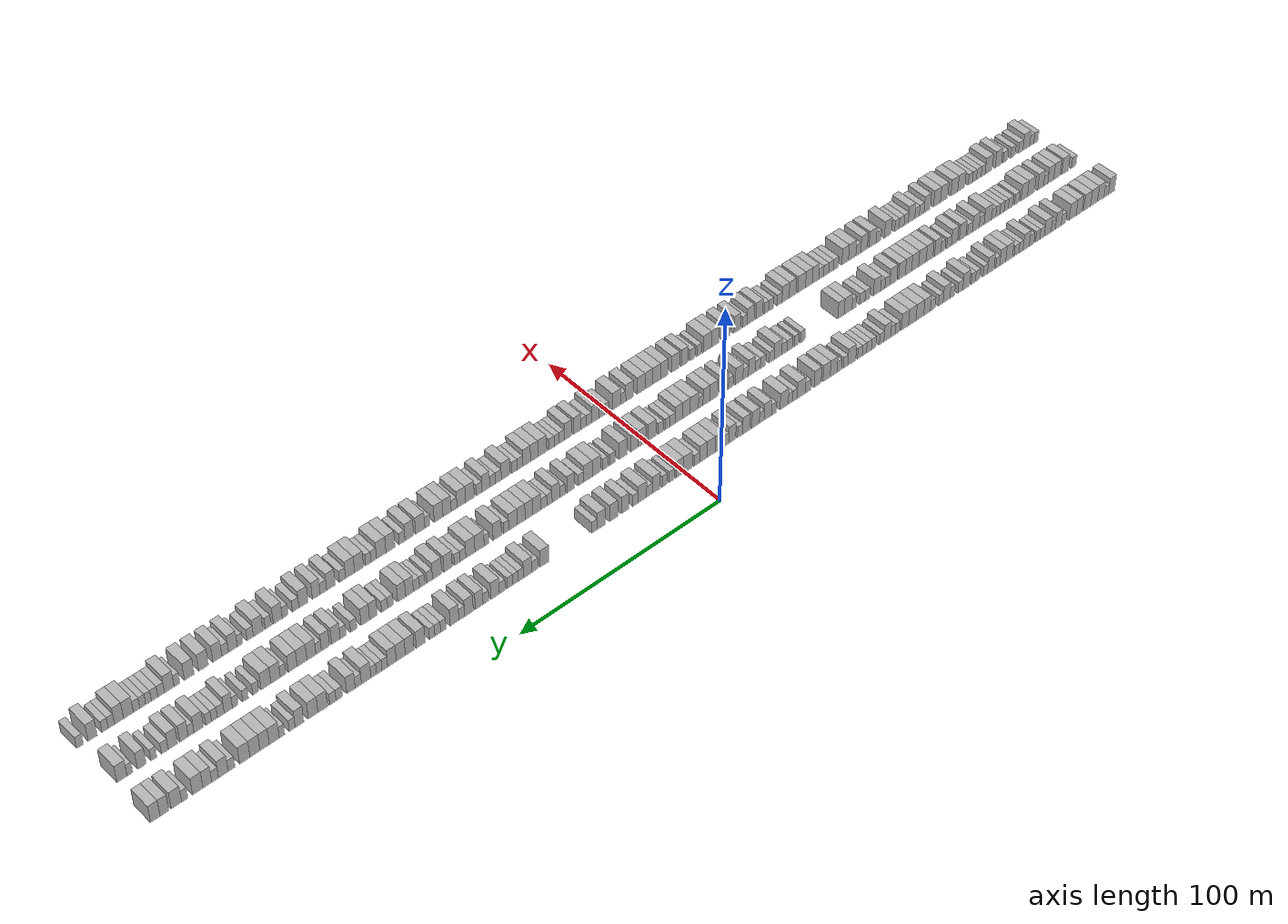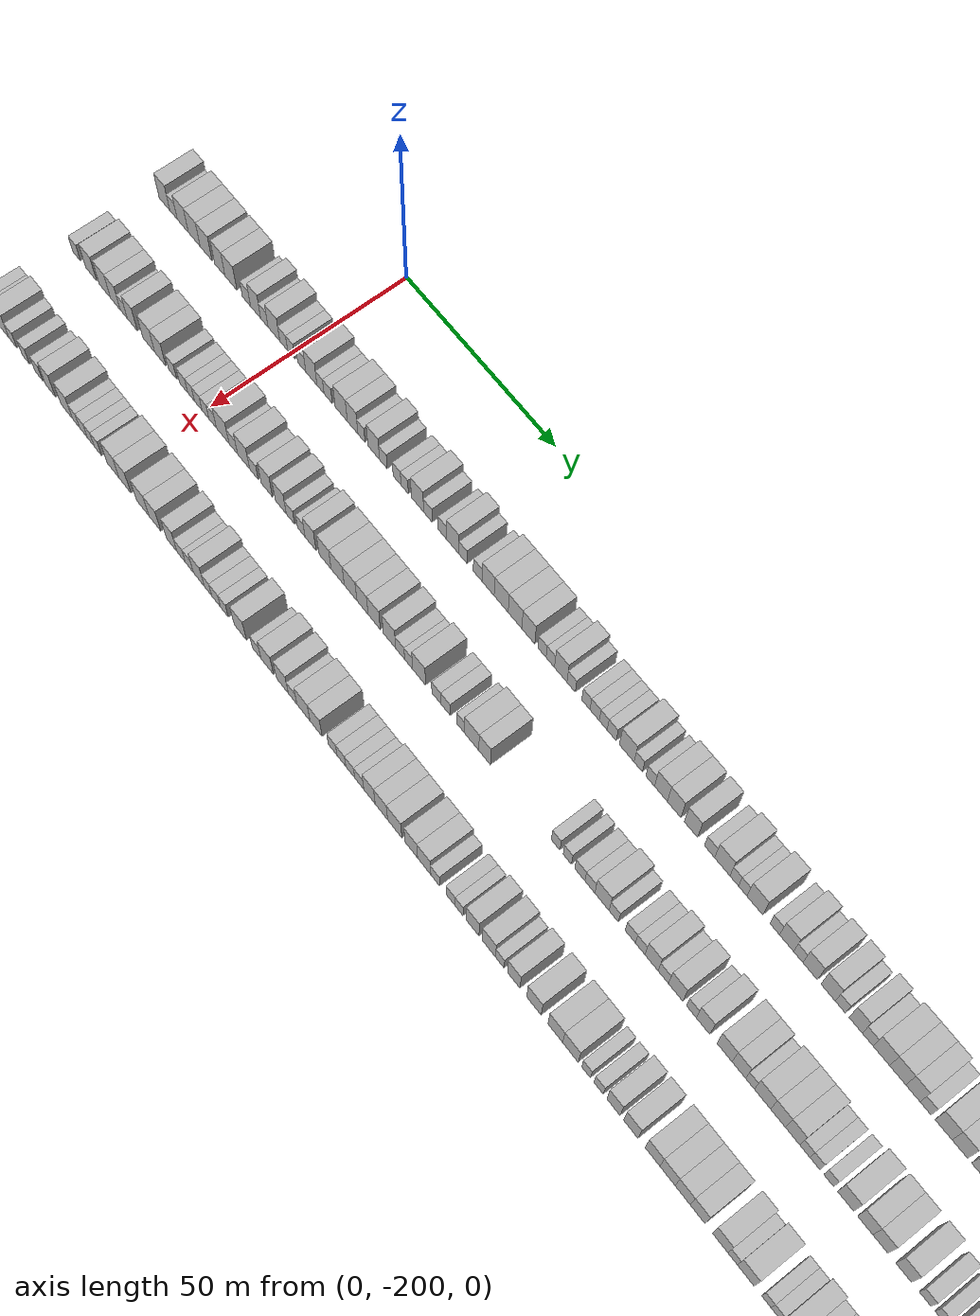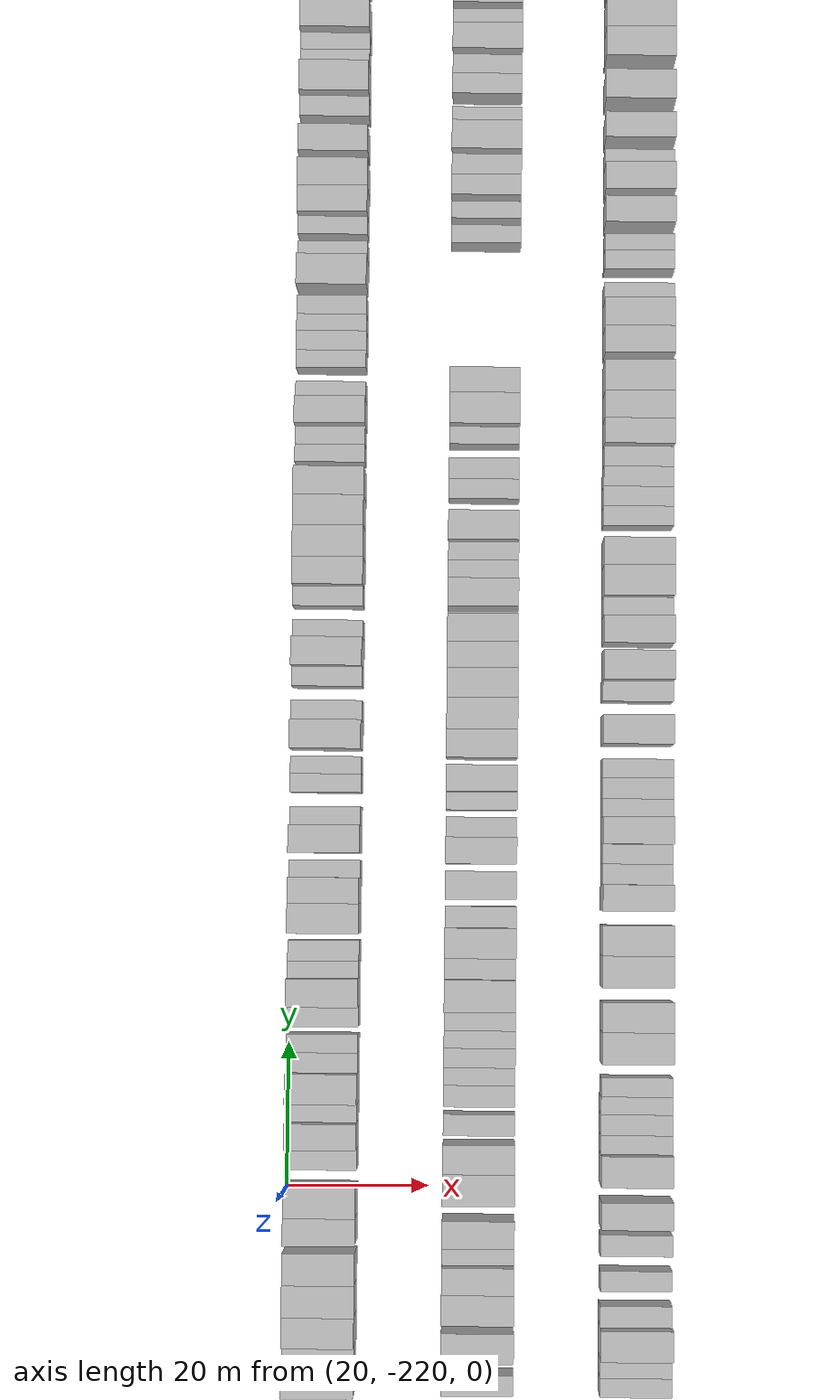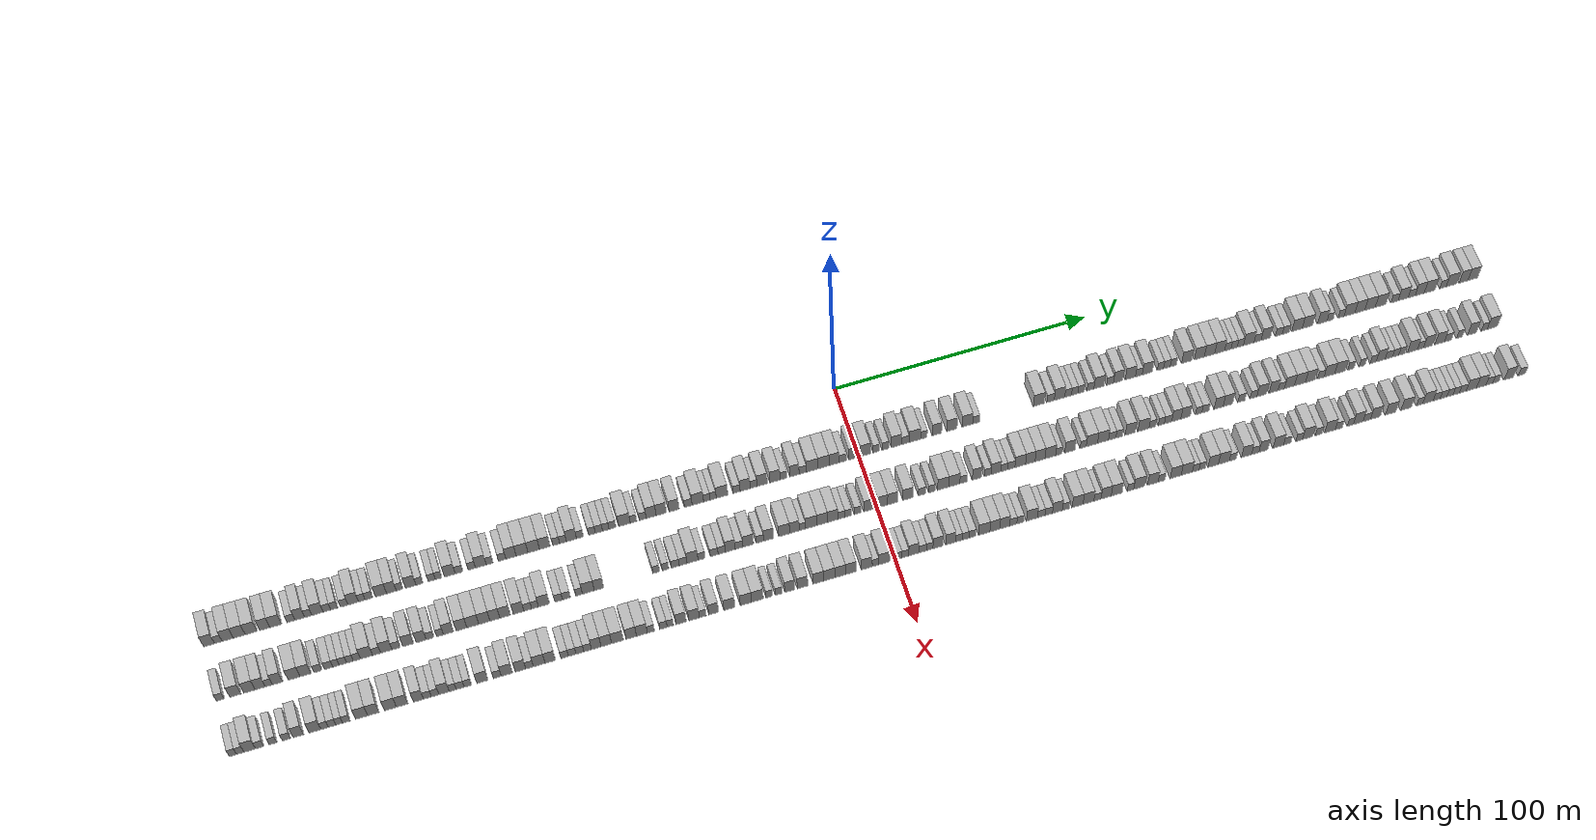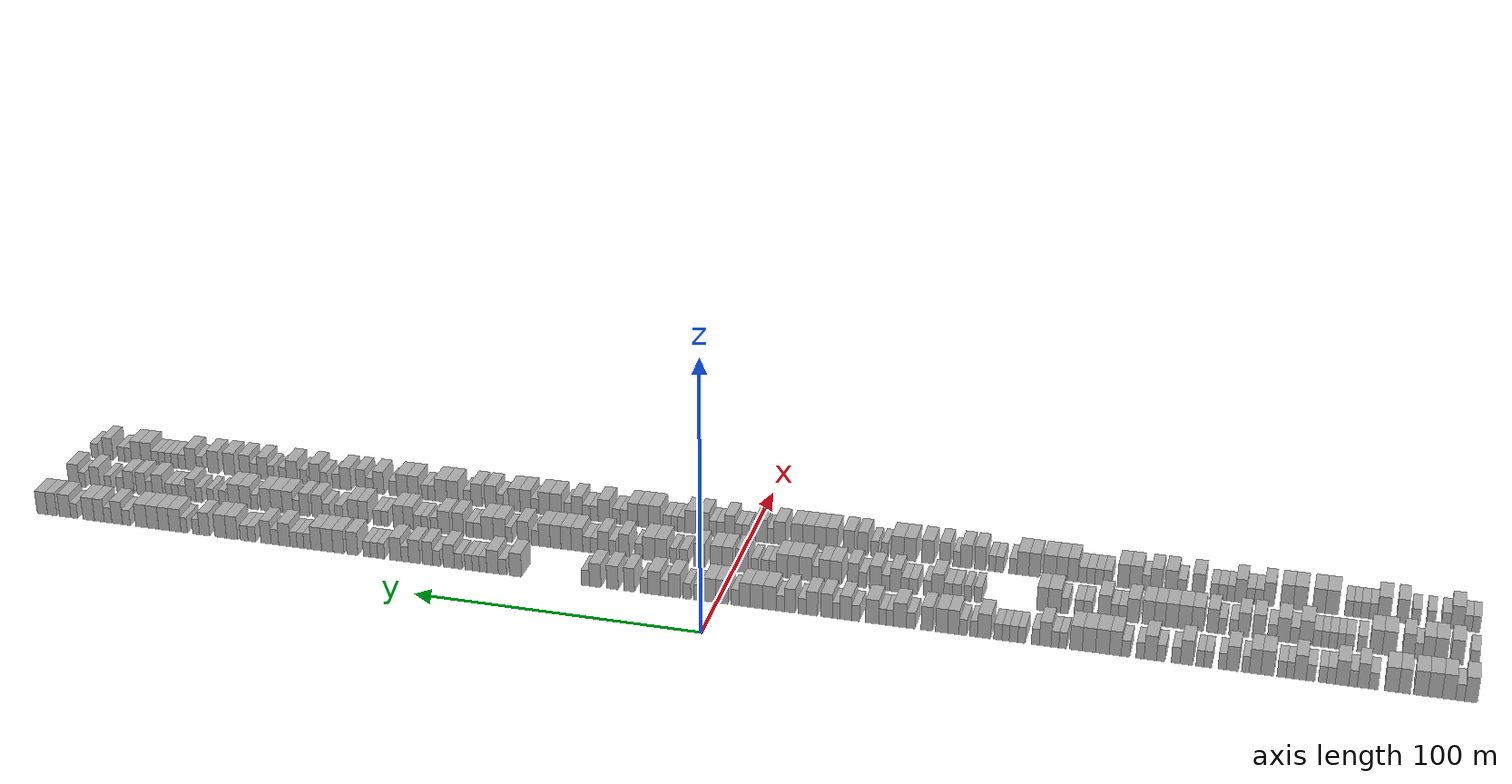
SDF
<sdf version="1.6">
 <world name="default">
  <scene>
   <sky><clouds><speed>12</speed></clouds></sky>
   <ambient>0.4 0.4 0.4 1</ambient>
   <background>0.7 0.7 0.7 1</background>
   <shadows>1</shadows>
  </scene>
  <gravity>0 0 -9.8066</gravity>
  <magnetic_field>6e-06 2.3e-05 -4.2e-05</magnetic_field>
  <physics default="0" name="default_physics" type="ode">
   <ode>
    <solver>
     <type>quick</type>
     <iters>10</iters>
     <sor>1.0</sor>
     <use_dynamic_moi_rescaling>0</use_dynamic_moi_rescaling>
    </solver>
    <constraints>
     <cfm>0</cfm>
     <erp>0.2</erp>
     <contact_max_correcting_vel>100</contact_max_correcting_vel>
     <contact_surface_layer>0.001</contact_surface_layer>
    </constraints>
   </ode>
   <max_step_size>0.004</max_step_size>
   <real_time_factor>1</real_time_factor>
   <real_time_update_rate>250</real_time_update_rate>
  </physics>
  <light name="sun" type="directional">
   <pose>0 0 10 0 0 0</pose>
   <diffuse>0.8 0.8 0.8 1</diffuse>
   <specular>0.2 0.2 0.2 1</specular>
   <attenuation>
    <range>1000</range>
    <constant>0.9</constant>
    <linear>0.01</linear>
    <quadratic>0.001</quadratic>
   </attenuation>
   <direction>-0.5 0.1 -0.9</direction>
  </light>
  <model name="building_1">
   <static>1</static>
   <pose>25.0000 -246.0041 0 0.000000 0.000000 0.000000</pose>
   <link name="link">
    <pose>0 0 4.50 0 0 0</pose>
    <collision name="collision"><geometry><box><size>10.0000 3.9917 9.0000</size></box></geometry></collision>
    <visual name="visual">
     <cast_shadows>0</cast_shadows>
     <geometry><box><size>10.0000 3.9917 9.0000</size></box></geometry>
     <material>
      <script>
       <uri>model://HANNAS_wall/materials/scripts</uri>
       <uri>model://HANNAS_wall/materials/textures</uri>
       <name>vrc/HANNAS_wall</name>
      </script>
     </material>
    </visual>
   </link>
  </model>
  <model name="building_2">
   <static>1</static>
   <pose>25.0000 -242.6186 0 0.000000 0.000000 0.000000</pose>
   <link name="link">
    <pose>0 0 3.00 0 0 0</pose>
    <collision name="collision"><geometry><box><size>10.0000 2.7794 6.0000</size></box></geometry></collision>
    <visual name="visual">
     <cast_shadows>0</cast_shadows>
     <geometry><box><size>10.0000 2.7794 6.0000</size></box></geometry>
     <material>
      <script>
       <uri>model://HANNAS_wall/materials/scripts</uri>
       <uri>model://HANNAS_wall/materials/textures</uri>
       <name>vrc/HANNAS_wall</name>
      </script>
     </material>
    </visual>
   </link>
  </model>
  <model name="building_3">
   <static>1</static>
   <pose>25.0000 -239.1554 0 0.000000 0.000000 0.000000</pose>
   <link name="link">
    <pose>0 0 4.50 0 0 0</pose>
    <collision name="collision"><geometry><box><size>10.0000 4.1470 9.0000</size></box></geometry></collision>
    <visual name="visual">
     <cast_shadows>0</cast_shadows>
     <geometry><box><size>10.0000 4.1470 9.0000</size></box></geometry>
     <material>
      <script>
       <uri>model://HANNAS_wall/materials/scripts</uri>
       <uri>model://HANNAS_wall/materials/textures</uri>
       <name>vrc/HANNAS_wall</name>
      </script>
     </material>
    </visual>
   </link>
  </model>
  <model name="building_4">
   <static>1</static>
   <pose>25.0000 -234.9000 0 0.000000 0.000000 0.000000</pose>
   <link name="link">
    <pose>0 0 4.50 0 0 0</pose>
    <collision name="collision"><geometry><box><size>10.0000 4.3639 9.0000</size></box></geometry></collision>
    <visual name="visual">
     <cast_shadows>0</cast_shadows>
     <geometry><box><size>10.0000 4.3639 9.0000</size></box></geometry>
     <material>
      <script>
       <uri>model://HANNAS_wall/materials/scripts</uri>
       <uri>model://HANNAS_wall/materials/textures</uri>
       <name>vrc/HANNAS_wall</name>
      </script>
     </material>
    </visual>
   </link>
  </model>
  <model name="building_5">
   <static>1</static>
   <pose>25.0000 -230.5349 0 0.000000 0.000000 0.000000</pose>
   <link name="link">
    <pose>0 0 4.50 0 0 0</pose>
    <collision name="collision"><geometry><box><size>10.0000 4.3663 9.0000</size></box></geometry></collision>
    <visual name="visual">
     <cast_shadows>0</cast_shadows>
     <geometry><box><size>10.0000 4.3663 9.0000</size></box></geometry>
     <material>
      <script>
       <uri>model://HANNAS_wall/materials/scripts</uri>
       <uri>model://HANNAS_wall/materials/textures</uri>
       <name>vrc/HANNAS_wall</name>
      </script>
     </material>
    </visual>
   </link>
  </model>
  <model name="building_6">
   <static>1</static>
   <pose>25.0000 -225.4878 0 0.000000 0.000000 0.000000</pose>
   <link name="link">
    <pose>0 0 4.50 0 0 0</pose>
    <collision name="collision"><geometry><box><size>10.0000 3.7281 9.0000</size></box></geometry></collision>
    <visual name="visual">
     <cast_shadows>0</cast_shadows>
     <geometry><box><size>10.0000 3.7281 9.0000</size></box></geometry>
     <material>
      <script>
       <uri>model://HANNAS_wall/materials/scripts</uri>
       <uri>model://HANNAS_wall/materials/textures</uri>
       <name>vrc/HANNAS_wall</name>
      </script>
     </material>
    </visual>
   </link>
  </model>
  <model name="building_7">
   <static>1</static>
   <pose>25.0000 -221.4656 0 0.000000 0.000000 0.000000</pose>
   <link name="link">
    <pose>0 0 4.50 0 0 0</pose>
    <collision name="collision"><geometry><box><size>10.0000 4.3163 9.0000</size></box></geometry></collision>
    <visual name="visual">
     <cast_shadows>0</cast_shadows>
     <geometry><box><size>10.0000 4.3163 9.0000</size></box></geometry>
     <material>
      <script>
       <uri>model://HANNAS_wall/materials/scripts</uri>
       <uri>model://HANNAS_wall/materials/textures</uri>
       <name>vrc/HANNAS_wall</name>
      </script>
     </material>
    </visual>
   </link>
  </model>
  <model name="building_8">
   <static>1</static>
   <pose>25.0000 -215.8325 0 0.000000 0.000000 0.000000</pose>
   <link name="link">
    <pose>0 0 3.00 0 0 0</pose>
    <collision name="collision"><geometry><box><size>10.0000 2.9498 6.0000</size></box></geometry></collision>
    <visual name="visual">
     <cast_shadows>0</cast_shadows>
     <geometry><box><size>10.0000 2.9498 6.0000</size></box></geometry>
     <material>
      <script>
       <uri>model://HANNAS_wall/materials/scripts</uri>
       <uri>model://HANNAS_wall/materials/textures</uri>
       <name>vrc/HANNAS_wall</name>
      </script>
     </material>
    </visual>
   </link>
  </model>
  <model name="building_9">
   <static>1</static>
   <pose>25.0000 -212.5433 0 0.000000 0.000000 0.000000</pose>
   <link name="link">
    <pose>0 0 4.50 0 0 0</pose>
    <collision name="collision"><geometry><box><size>10.0000 3.6286 9.0000</size></box></geometry></collision>
    <visual name="visual">
     <cast_shadows>0</cast_shadows>
     <geometry><box><size>10.0000 3.6286 9.0000</size></box></geometry>
     <material>
      <script>
       <uri>model://HANNAS_wall/materials/scripts</uri>
       <uri>model://HANNAS_wall/materials/textures</uri>
       <name>vrc/HANNAS_wall</name>
      </script>
     </material>
    </visual>
   </link>
  </model>
  <model name="building_10">
   <static>1</static>
   <pose>25.0000 -209.4067 0 0.000000 0.000000 0.000000</pose>
   <link name="link">
    <pose>0 0 3.00 0 0 0</pose>
    <collision name="collision"><geometry><box><size>10.0000 2.6446 6.0000</size></box></geometry></collision>
    <visual name="visual">
     <cast_shadows>0</cast_shadows>
     <geometry><box><size>10.0000 2.6446 6.0000</size></box></geometry>
     <material>
      <script>
       <uri>model://HANNAS_wall/materials/scripts</uri>
       <uri>model://HANNAS_wall/materials/textures</uri>
       <name>vrc/HANNAS_wall</name>
      </script>
     </material>
    </visual>
   </link>
  </model>
  <model name="building_11">
   <static>1</static>
   <pose>25.0000 -205.9943 0 0.000000 0.000000 0.000000</pose>
   <link name="link">
    <pose>0 0 4.50 0 0 0</pose>
    <collision name="collision"><geometry><box><size>10.0000 4.1802 9.0000</size></box></geometry></collision>
    <visual name="visual">
     <cast_shadows>0</cast_shadows>
     <geometry><box><size>10.0000 4.1802 9.0000</size></box></geometry>
     <material>
      <script>
       <uri>model://HANNAS_wall/materials/scripts</uri>
       <uri>model://HANNAS_wall/materials/textures</uri>
       <name>vrc/HANNAS_wall</name>
      </script>
     </material>
    </visual>
   </link>
  </model>
  <model name="building_12">
   <static>1</static>
   <pose>25.0000 -202.5195 0 0.000000 0.000000 0.000000</pose>
   <link name="link">
    <pose>0 0 3.00 0 0 0</pose>
    <collision name="collision"><geometry><box><size>10.0000 2.7696 6.0000</size></box></geometry></collision>
    <visual name="visual">
     <cast_shadows>0</cast_shadows>
     <geometry><box><size>10.0000 2.7696 6.0000</size></box></geometry>
     <material>
      <script>
       <uri>model://HANNAS_wall/materials/scripts</uri>
       <uri>model://HANNAS_wall/materials/textures</uri>
       <name>vrc/HANNAS_wall</name>
      </script>
     </material>
    </visual>
   </link>
  </model>
  <model name="building_13">
   <static>1</static>
   <pose>25.0000 -199.8488 0 0.000000 0.000000 0.000000</pose>
   <link name="link">
    <pose>0 0 3.00 0 0 0</pose>
    <collision name="collision"><geometry><box><size>10.0000 2.5718 6.0000</size></box></geometry></collision>
    <visual name="visual">
     <cast_shadows>0</cast_shadows>
     <geometry><box><size>10.0000 2.5718 6.0000</size></box></geometry>
     <material>
      <script>
       <uri>model://HANNAS_wall/materials/scripts</uri>
       <uri>model://HANNAS_wall/materials/textures</uri>
       <name>vrc/HANNAS_wall</name>
      </script>
     </material>
    </visual>
   </link>
  </model>
  <model name="building_14">
   <static>1</static>
   <pose>25.0000 -196.1466 0 0.000000 0.000000 0.000000</pose>
   <link name="link">
    <pose>0 0 3.00 0 0 0</pose>
    <collision name="collision"><geometry><box><size>10.0000 2.8326 6.0000</size></box></geometry></collision>
    <visual name="visual">
     <cast_shadows>0</cast_shadows>
     <geometry><box><size>10.0000 2.8326 6.0000</size></box></geometry>
     <material>
      <script>
       <uri>model://HANNAS_wall/materials/scripts</uri>
       <uri>model://HANNAS_wall/materials/textures</uri>
       <name>vrc/HANNAS_wall</name>
      </script>
     </material>
    </visual>
   </link>
  </model>
  <model name="building_15">
   <static>1</static>
   <pose>25.0000 -192.7715 0 0.000000 0.000000 0.000000</pose>
   <link name="link">
    <pose>0 0 4.50 0 0 0</pose>
    <collision name="collision"><geometry><box><size>10.0000 3.9178 9.0000</size></box></geometry></collision>
    <visual name="visual">
     <cast_shadows>0</cast_shadows>
     <geometry><box><size>10.0000 3.9178 9.0000</size></box></geometry>
     <material>
      <script>
       <uri>model://HANNAS_wall/materials/scripts</uri>
       <uri>model://HANNAS_wall/materials/textures</uri>
       <name>vrc/HANNAS_wall</name>
      </script>
     </material>
    </visual>
   </link>
  </model>
  <model name="building_16">
   <static>1</static>
   <pose>25.0000 -189.5995 0 0.000000 0.000000 0.000000</pose>
   <link name="link">
    <pose>0 0 3.00 0 0 0</pose>
    <collision name="collision"><geometry><box><size>10.0000 2.4261 6.0000</size></box></geometry></collision>
    <visual name="visual">
     <cast_shadows>0</cast_shadows>
     <geometry><box><size>10.0000 2.4261 6.0000</size></box></geometry>
     <material>
      <script>
       <uri>model://HANNAS_wall/materials/scripts</uri>
       <uri>model://HANNAS_wall/materials/textures</uri>
       <name>vrc/HANNAS_wall</name>
      </script>
     </material>
    </visual>
   </link>
  </model>
  <model name="building_17">
   <static>1</static>
   <pose>25.0000 -186.9614 0 0.000000 0.000000 0.000000</pose>
   <link name="link">
    <pose>0 0 3.00 0 0 0</pose>
    <collision name="collision"><geometry><box><size>10.0000 2.8503 6.0000</size></box></geometry></collision>
    <visual name="visual">
     <cast_shadows>0</cast_shadows>
     <geometry><box><size>10.0000 2.8503 6.0000</size></box></geometry>
     <material>
      <script>
       <uri>model://HANNAS_wall/materials/scripts</uri>
       <uri>model://HANNAS_wall/materials/textures</uri>
       <name>vrc/HANNAS_wall</name>
      </script>
     </material>
    </visual>
   </link>
  </model>
  <model name="building_18">
   <static>1</static>
   <pose>25.0000 -182.4439 0 0.000000 0.000000 0.000000</pose>
   <link name="link">
    <pose>0 0 4.50 0 0 0</pose>
    <collision name="collision"><geometry><box><size>10.0000 4.1845 9.0000</size></box></geometry></collision>
    <visual name="visual">
     <cast_shadows>0</cast_shadows>
     <geometry><box><size>10.0000 4.1845 9.0000</size></box></geometry>
     <material>
      <script>
       <uri>model://HANNAS_wall/materials/scripts</uri>
       <uri>model://HANNAS_wall/materials/textures</uri>
       <name>vrc/HANNAS_wall</name>
      </script>
     </material>
    </visual>
   </link>
  </model>
  <model name="building_19">
   <static>1</static>
   <pose>25.0000 -178.5426 0 0.000000 0.000000 0.000000</pose>
   <link name="link">
    <pose>0 0 4.50 0 0 0</pose>
    <collision name="collision"><geometry><box><size>10.0000 3.6182 9.0000</size></box></geometry></collision>
    <visual name="visual">
     <cast_shadows>0</cast_shadows>
     <geometry><box><size>10.0000 3.6182 9.0000</size></box></geometry>
     <material>
      <script>
       <uri>model://HANNAS_wall/materials/scripts</uri>
       <uri>model://HANNAS_wall/materials/textures</uri>
       <name>vrc/HANNAS_wall</name>
      </script>
     </material>
    </visual>
   </link>
  </model>
  <model name="building_20">
   <static>1</static>
   <pose>25.0000 -175.5181 0 0.000000 0.000000 0.000000</pose>
   <link name="link">
    <pose>0 0 3.00 0 0 0</pose>
    <collision name="collision"><geometry><box><size>10.0000 2.4307 6.0000</size></box></geometry></collision>
    <visual name="visual">
     <cast_shadows>0</cast_shadows>
     <geometry><box><size>10.0000 2.4307 6.0000</size></box></geometry>
     <material>
      <script>
       <uri>model://HANNAS_wall/materials/scripts</uri>
       <uri>model://HANNAS_wall/materials/textures</uri>
       <name>vrc/HANNAS_wall</name>
      </script>
     </material>
    </visual>
   </link>
  </model>
  <model name="building_21">
   <static>1</static>
   <pose>25.0000 -171.3433 0 0.000000 0.000000 0.000000</pose>
   <link name="link">
    <pose>0 0 4.50 0 0 0</pose>
    <collision name="collision"><geometry><box><size>10.0000 3.9191 9.0000</size></box></geometry></collision>
    <visual name="visual">
     <cast_shadows>0</cast_shadows>
     <geometry><box><size>10.0000 3.9191 9.0000</size></box></geometry>
     <material>
      <script>
       <uri>model://HANNAS_wall/materials/scripts</uri>
       <uri>model://HANNAS_wall/materials/textures</uri>
       <name>vrc/HANNAS_wall</name>
      </script>
     </material>
    </visual>
   </link>
  </model>
  <model name="building_22">
   <static>1</static>
   <pose>25.0000 -168.0921 0 0.000000 0.000000 0.000000</pose>
   <link name="link">
    <pose>0 0 3.00 0 0 0</pose>
    <collision name="collision"><geometry><box><size>10.0000 2.5832 6.0000</size></box></geometry></collision>
    <visual name="visual">
     <cast_shadows>0</cast_shadows>
     <geometry><box><size>10.0000 2.5832 6.0000</size></box></geometry>
     <material>
      <script>
       <uri>model://HANNAS_wall/materials/scripts</uri>
       <uri>model://HANNAS_wall/materials/textures</uri>
       <name>vrc/HANNAS_wall</name>
      </script>
     </material>
    </visual>
   </link>
  </model>
  <model name="building_23">
   <static>1</static>
   <pose>25.0000 -163.4881 0 0.000000 0.000000 0.000000</pose>
   <link name="link">
    <pose>0 0 3.00 0 0 0</pose>
    <collision name="collision"><geometry><box><size>10.0000 2.6249 6.0000</size></box></geometry></collision>
    <visual name="visual">
     <cast_shadows>0</cast_shadows>
     <geometry><box><size>10.0000 2.6249 6.0000</size></box></geometry>
     <material>
      <script>
       <uri>model://HANNAS_wall/materials/scripts</uri>
       <uri>model://HANNAS_wall/materials/textures</uri>
       <name>vrc/HANNAS_wall</name>
      </script>
     </material>
    </visual>
   </link>
  </model>
  <model name="building_24">
   <static>1</static>
   <pose>25.0000 -160.9484 0 0.000000 0.000000 0.000000</pose>
   <link name="link">
    <pose>0 0 3.00 0 0 0</pose>
    <collision name="collision"><geometry><box><size>10.0000 2.4546 6.0000</size></box></geometry></collision>
    <visual name="visual">
     <cast_shadows>0</cast_shadows>
     <geometry><box><size>10.0000 2.4546 6.0000</size></box></geometry>
     <material>
      <script>
       <uri>model://HANNAS_wall/materials/scripts</uri>
       <uri>model://HANNAS_wall/materials/textures</uri>
       <name>vrc/HANNAS_wall</name>
      </script>
     </material>
    </visual>
   </link>
  </model>
  <model name="building_25">
   <static>1</static>
   <pose>25.0000 -156.6901 0 0.000000 0.000000 0.000000</pose>
   <link name="link">
    <pose>0 0 4.50 0 0 0</pose>
    <collision name="collision"><geometry><box><size>10.0000 4.0618 9.0000</size></box></geometry></collision>
    <visual name="visual">
     <cast_shadows>0</cast_shadows>
     <geometry><box><size>10.0000 4.0618 9.0000</size></box></geometry>
     <material>
      <script>
       <uri>model://HANNAS_wall/materials/scripts</uri>
       <uri>model://HANNAS_wall/materials/textures</uri>
       <name>vrc/HANNAS_wall</name>
      </script>
     </material>
    </visual>
   </link>
  </model>
  <model name="building_26">
   <static>1</static>
   <pose>25.0000 -153.2342 0 0.000000 0.000000 0.000000</pose>
   <link name="link">
    <pose>0 0 3.00 0 0 0</pose>
    <collision name="collision"><geometry><box><size>10.0000 2.8501 6.0000</size></box></geometry></collision>
    <visual name="visual">
     <cast_shadows>0</cast_shadows>
     <geometry><box><size>10.0000 2.8501 6.0000</size></box></geometry>
     <material>
      <script>
       <uri>model://HANNAS_wall/materials/scripts</uri>
       <uri>model://HANNAS_wall/materials/textures</uri>
       <name>vrc/HANNAS_wall</name>
      </script>
     </material>
    </visual>
   </link>
  </model>
  <model name="building_27">
   <static>1</static>
   <pose>25.0000 -148.4355 0 0.000000 0.000000 0.000000</pose>
   <link name="link">
    <pose>0 0 3.00 0 0 0</pose>
    <collision name="collision"><geometry><box><size>10.0000 2.7472 6.0000</size></box></geometry></collision>
    <visual name="visual">
     <cast_shadows>0</cast_shadows>
     <geometry><box><size>10.0000 2.7472 6.0000</size></box></geometry>
     <material>
      <script>
       <uri>model://HANNAS_wall/materials/scripts</uri>
       <uri>model://HANNAS_wall/materials/textures</uri>
       <name>vrc/HANNAS_wall</name>
      </script>
     </material>
    </visual>
   </link>
  </model>
  <model name="building_28">
   <static>1</static>
   <pose>25.0000 -145.0382 0 0.000000 0.000000 0.000000</pose>
   <link name="link">
    <pose>0 0 4.50 0 0 0</pose>
    <collision name="collision"><geometry><box><size>10.0000 4.0474 9.0000</size></box></geometry></collision>
    <visual name="visual">
     <cast_shadows>0</cast_shadows>
     <geometry><box><size>10.0000 4.0474 9.0000</size></box></geometry>
     <material>
      <script>
       <uri>model://HANNAS_wall/materials/scripts</uri>
       <uri>model://HANNAS_wall/materials/textures</uri>
       <name>vrc/HANNAS_wall</name>
      </script>
     </material>
    </visual>
   </link>
  </model>
  <model name="building_29">
   <static>1</static>
   <pose>25.0000 -141.7156 0 0.000000 0.000000 0.000000</pose>
   <link name="link">
    <pose>0 0 3.00 0 0 0</pose>
    <collision name="collision"><geometry><box><size>10.0000 2.5978 6.0000</size></box></geometry></collision>
    <visual name="visual">
     <cast_shadows>0</cast_shadows>
     <geometry><box><size>10.0000 2.5978 6.0000</size></box></geometry>
     <material>
      <script>
       <uri>model://HANNAS_wall/materials/scripts</uri>
       <uri>model://HANNAS_wall/materials/textures</uri>
       <name>vrc/HANNAS_wall</name>
      </script>
     </material>
    </visual>
   </link>
  </model>
  <model name="building_30">
   <static>1</static>
   <pose>25.0000 -137.0139 0 0.000000 0.000000 0.000000</pose>
   <link name="link">
    <pose>0 0 3.00 0 0 0</pose>
    <collision name="collision"><geometry><box><size>10.0000 2.8056 6.0000</size></box></geometry></collision>
    <visual name="visual">
     <cast_shadows>0</cast_shadows>
     <geometry><box><size>10.0000 2.8056 6.0000</size></box></geometry>
     <material>
      <script>
       <uri>model://HANNAS_wall/materials/scripts</uri>
       <uri>model://HANNAS_wall/materials/textures</uri>
       <name>vrc/HANNAS_wall</name>
      </script>
     </material>
    </visual>
   </link>
  </model>
  <model name="building_31">
   <static>1</static>
   <pose>25.0000 -133.6611 0 0.000000 0.000000 0.000000</pose>
   <link name="link">
    <pose>0 0 4.50 0 0 0</pose>
    <collision name="collision"><geometry><box><size>10.0000 3.8999 9.0000</size></box></geometry></collision>
    <visual name="visual">
     <cast_shadows>0</cast_shadows>
     <geometry><box><size>10.0000 3.8999 9.0000</size></box></geometry>
     <material>
      <script>
       <uri>model://HANNAS_wall/materials/scripts</uri>
       <uri>model://HANNAS_wall/materials/textures</uri>
       <name>vrc/HANNAS_wall</name>
      </script>
     </material>
    </visual>
   </link>
  </model>
  <model name="building_32">
   <static>1</static>
   <pose>25.0000 -129.4743 0 0.000000 0.000000 0.000000</pose>
   <link name="link">
    <pose>0 0 4.50 0 0 0</pose>
    <collision name="collision"><geometry><box><size>10.0000 4.4739 9.0000</size></box></geometry></collision>
    <visual name="visual">
     <cast_shadows>0</cast_shadows>
     <geometry><box><size>10.0000 4.4739 9.0000</size></box></geometry>
     <material>
      <script>
       <uri>model://HANNAS_wall/materials/scripts</uri>
       <uri>model://HANNAS_wall/materials/textures</uri>
       <name>vrc/HANNAS_wall</name>
      </script>
     </material>
    </visual>
   </link>
  </model>
  <model name="building_33">
   <static>1</static>
   <pose>25.0000 -125.0776 0 0.000000 0.000000 0.000000</pose>
   <link name="link">
    <pose>0 0 4.50 0 0 0</pose>
    <collision name="collision"><geometry><box><size>10.0000 4.3195 9.0000</size></box></geometry></collision>
    <visual name="visual">
     <cast_shadows>0</cast_shadows>
     <geometry><box><size>10.0000 4.3195 9.0000</size></box></geometry>
     <material>
      <script>
       <uri>model://HANNAS_wall/materials/scripts</uri>
       <uri>model://HANNAS_wall/materials/textures</uri>
       <name>vrc/HANNAS_wall</name>
      </script>
     </material>
    </visual>
   </link>
  </model>
  <model name="building_34">
   <static>1</static>
   <pose>25.0000 -120.8792 0 0.000000 0.000000 0.000000</pose>
   <link name="link">
    <pose>0 0 4.50 0 0 0</pose>
    <collision name="collision"><geometry><box><size>10.0000 4.0772 9.0000</size></box></geometry></collision>
    <visual name="visual">
     <cast_shadows>0</cast_shadows>
     <geometry><box><size>10.0000 4.0772 9.0000</size></box></geometry>
     <material>
      <script>
       <uri>model://HANNAS_wall/materials/scripts</uri>
       <uri>model://HANNAS_wall/materials/textures</uri>
       <name>vrc/HANNAS_wall</name>
      </script>
     </material>
    </visual>
   </link>
  </model>
  <model name="building_35">
   <static>1</static>
   <pose>25.0000 -116.5650 0 0.000000 0.000000 0.000000</pose>
   <link name="link">
    <pose>0 0 3.00 0 0 0</pose>
    <collision name="collision"><geometry><box><size>10.0000 2.5513 6.0000</size></box></geometry></collision>
    <visual name="visual">
     <cast_shadows>0</cast_shadows>
     <geometry><box><size>10.0000 2.5513 6.0000</size></box></geometry>
     <material>
      <script>
       <uri>model://HANNAS_wall/materials/scripts</uri>
       <uri>model://HANNAS_wall/materials/textures</uri>
       <name>vrc/HANNAS_wall</name>
      </script>
     </material>
    </visual>
   </link>
  </model>
  <model name="building_36">
   <static>1</static>
   <pose>25.0000 -113.9904 0 0.000000 0.000000 0.000000</pose>
   <link name="link">
    <pose>0 0 3.00 0 0 0</pose>
    <collision name="collision"><geometry><box><size>10.0000 2.5978 6.0000</size></box></geometry></collision>
    <visual name="visual">
     <cast_shadows>0</cast_shadows>
     <geometry><box><size>10.0000 2.5978 6.0000</size></box></geometry>
     <material>
      <script>
       <uri>model://HANNAS_wall/materials/scripts</uri>
       <uri>model://HANNAS_wall/materials/textures</uri>
       <name>vrc/HANNAS_wall</name>
      </script>
     </material>
    </visual>
   </link>
  </model>
  <model name="building_37">
   <static>1</static>
   <pose>25.0000 -110.7611 0 0.000000 0.000000 0.000000</pose>
   <link name="link">
    <pose>0 0 4.50 0 0 0</pose>
    <collision name="collision"><geometry><box><size>10.0000 3.8607 9.0000</size></box></geometry></collision>
    <visual name="visual">
     <cast_shadows>0</cast_shadows>
     <geometry><box><size>10.0000 3.8607 9.0000</size></box></geometry>
     <material>
      <script>
       <uri>model://HANNAS_wall/materials/scripts</uri>
       <uri>model://HANNAS_wall/materials/textures</uri>
       <name>vrc/HANNAS_wall</name>
      </script>
     </material>
    </visual>
   </link>
  </model>
  <model name="building_38">
   <static>1</static>
   <pose>25.0000 -107.5421 0 0.000000 0.000000 0.000000</pose>
   <link name="link">
    <pose>0 0 3.00 0 0 0</pose>
    <collision name="collision"><geometry><box><size>10.0000 2.5774 6.0000</size></box></geometry></collision>
    <visual name="visual">
     <cast_shadows>0</cast_shadows>
     <geometry><box><size>10.0000 2.5774 6.0000</size></box></geometry>
     <material>
      <script>
       <uri>model://HANNAS_wall/materials/scripts</uri>
       <uri>model://HANNAS_wall/materials/textures</uri>
       <name>vrc/HANNAS_wall</name>
      </script>
     </material>
    </visual>
   </link>
  </model>
  <model name="building_39">
   <static>1</static>
   <pose>25.0000 -102.9907 0 0.000000 0.000000 0.000000</pose>
   <link name="link">
    <pose>0 0 3.00 0 0 0</pose>
    <collision name="collision"><geometry><box><size>10.0000 2.5255 6.0000</size></box></geometry></collision>
    <visual name="visual">
     <cast_shadows>0</cast_shadows>
     <geometry><box><size>10.0000 2.5255 6.0000</size></box></geometry>
     <material>
      <script>
       <uri>model://HANNAS_wall/materials/scripts</uri>
       <uri>model://HANNAS_wall/materials/textures</uri>
       <name>vrc/HANNAS_wall</name>
      </script>
     </material>
    </visual>
   </link>
  </model>
  <model name="building_40">
   <static>1</static>
   <pose>25.0000 -100.3243 0 0.000000 0.000000 0.000000</pose>
   <link name="link">
    <pose>0 0 3.00 0 0 0</pose>
    <collision name="collision"><geometry><box><size>10.0000 2.8073 6.0000</size></box></geometry></collision>
    <visual name="visual">
     <cast_shadows>0</cast_shadows>
     <geometry><box><size>10.0000 2.8073 6.0000</size></box></geometry>
     <material>
      <script>
       <uri>model://HANNAS_wall/materials/scripts</uri>
       <uri>model://HANNAS_wall/materials/textures</uri>
       <name>vrc/HANNAS_wall</name>
      </script>
     </material>
    </visual>
   </link>
  </model>
  <model name="building_41">
   <static>1</static>
   <pose>25.0000 -97.7084 0 0.000000 0.000000 0.000000</pose>
   <link name="link">
    <pose>0 0 3.00 0 0 0</pose>
    <collision name="collision"><geometry><box><size>10.0000 2.4245 6.0000</size></box></geometry></collision>
    <visual name="visual">
     <cast_shadows>0</cast_shadows>
     <geometry><box><size>10.0000 2.4245 6.0000</size></box></geometry>
     <material>
      <script>
       <uri>model://HANNAS_wall/materials/scripts</uri>
       <uri>model://HANNAS_wall/materials/textures</uri>
       <name>vrc/HANNAS_wall</name>
      </script>
     </material>
    </visual>
   </link>
  </model>
  <model name="building_42">
   <static>1</static>
   <pose>25.0000 -95.1471 0 0.000000 0.000000 0.000000</pose>
   <link name="link">
    <pose>0 0 3.00 0 0 0</pose>
    <collision name="collision"><geometry><box><size>10.0000 2.6981 6.0000</size></box></geometry></collision>
    <visual name="visual">
     <cast_shadows>0</cast_shadows>
     <geometry><box><size>10.0000 2.6981 6.0000</size></box></geometry>
     <material>
      <script>
       <uri>model://HANNAS_wall/materials/scripts</uri>
       <uri>model://HANNAS_wall/materials/textures</uri>
       <name>vrc/HANNAS_wall</name>
      </script>
     </material>
    </visual>
   </link>
  </model>
  <model name="building_43">
   <static>1</static>
   <pose>25.0000 -90.5952 0 0.000000 0.000000 0.000000</pose>
   <link name="link">
    <pose>0 0 4.50 0 0 0</pose>
    <collision name="collision"><geometry><box><size>10.0000 4.4057 9.0000</size></box></geometry></collision>
    <visual name="visual">
     <cast_shadows>0</cast_shadows>
     <geometry><box><size>10.0000 4.4057 9.0000</size></box></geometry>
     <material>
      <script>
       <uri>model://HANNAS_wall/materials/scripts</uri>
       <uri>model://HANNAS_wall/materials/textures</uri>
       <name>vrc/HANNAS_wall</name>
      </script>
     </material>
    </visual>
   </link>
  </model>
  <model name="building_44">
   <static>1</static>
   <pose>25.0000 -87.1401 0 0.000000 0.000000 0.000000</pose>
   <link name="link">
    <pose>0 0 3.00 0 0 0</pose>
    <collision name="collision"><geometry><box><size>10.0000 2.5045 6.0000</size></box></geometry></collision>
    <visual name="visual">
     <cast_shadows>0</cast_shadows>
     <geometry><box><size>10.0000 2.5045 6.0000</size></box></geometry>
     <material>
      <script>
       <uri>model://HANNAS_wall/materials/scripts</uri>
       <uri>model://HANNAS_wall/materials/textures</uri>
       <name>vrc/HANNAS_wall</name>
      </script>
     </material>
    </visual>
   </link>
  </model>
  <model name="building_45">
   <static>1</static>
   <pose>25.0000 -83.5839 0 0.000000 0.000000 0.000000</pose>
   <link name="link">
    <pose>0 0 3.00 0 0 0</pose>
    <collision name="collision"><geometry><box><size>10.0000 2.6078 6.0000</size></box></geometry></collision>
    <visual name="visual">
     <cast_shadows>0</cast_shadows>
     <geometry><box><size>10.0000 2.6078 6.0000</size></box></geometry>
     <material>
      <script>
       <uri>model://HANNAS_wall/materials/scripts</uri>
       <uri>model://HANNAS_wall/materials/textures</uri>
       <name>vrc/HANNAS_wall</name>
      </script>
     </material>
    </visual>
   </link>
  </model>
  <model name="building_46">
   <static>1</static>
   <pose>25.0000 -80.3772 0 0.000000 0.000000 0.000000</pose>
   <link name="link">
    <pose>0 0 4.50 0 0 0</pose>
    <collision name="collision"><geometry><box><size>10.0000 3.8057 9.0000</size></box></geometry></collision>
    <visual name="visual">
     <cast_shadows>0</cast_shadows>
     <geometry><box><size>10.0000 3.8057 9.0000</size></box></geometry>
     <material>
      <script>
       <uri>model://HANNAS_wall/materials/scripts</uri>
       <uri>model://HANNAS_wall/materials/textures</uri>
       <name>vrc/HANNAS_wall</name>
      </script>
     </material>
    </visual>
   </link>
  </model>
  <model name="building_47">
   <static>1</static>
   <pose>25.0000 -76.4669 0 0.000000 0.000000 0.000000</pose>
   <link name="link">
    <pose>0 0 4.50 0 0 0</pose>
    <collision name="collision"><geometry><box><size>10.0000 4.0148 9.0000</size></box></geometry></collision>
    <visual name="visual">
     <cast_shadows>0</cast_shadows>
     <geometry><box><size>10.0000 4.0148 9.0000</size></box></geometry>
     <material>
      <script>
       <uri>model://HANNAS_wall/materials/scripts</uri>
       <uri>model://HANNAS_wall/materials/textures</uri>
       <name>vrc/HANNAS_wall</name>
      </script>
     </material>
    </visual>
   </link>
  </model>
  <model name="building_48">
   <static>1</static>
   <pose>25.0000 -71.5309 0 0.000000 0.000000 0.000000</pose>
   <link name="link">
    <pose>0 0 4.50 0 0 0</pose>
    <collision name="collision"><geometry><box><size>10.0000 3.8572 9.0000</size></box></geometry></collision>
    <visual name="visual">
     <cast_shadows>0</cast_shadows>
     <geometry><box><size>10.0000 3.8572 9.0000</size></box></geometry>
     <material>
      <script>
       <uri>model://HANNAS_wall/materials/scripts</uri>
       <uri>model://HANNAS_wall/materials/textures</uri>
       <name>vrc/HANNAS_wall</name>
      </script>
     </material>
    </visual>
   </link>
  </model>
  <model name="building_49">
   <static>1</static>
   <pose>25.0000 -66.1277 0 0.000000 0.000000 0.000000</pose>
   <link name="link">
    <pose>0 0 3.00 0 0 0</pose>
    <collision name="collision"><geometry><box><size>10.0000 2.9492 6.0000</size></box></geometry></collision>
    <visual name="visual">
     <cast_shadows>0</cast_shadows>
     <geometry><box><size>10.0000 2.9492 6.0000</size></box></geometry>
     <material>
      <script>
       <uri>model://HANNAS_wall/materials/scripts</uri>
       <uri>model://HANNAS_wall/materials/textures</uri>
       <name>vrc/HANNAS_wall</name>
      </script>
     </material>
    </visual>
   </link>
  </model>
  <model name="building_50">
   <static>1</static>
   <pose>25.0000 -62.4481 0 0.000000 0.000000 0.000000</pose>
   <link name="link">
    <pose>0 0 4.50 0 0 0</pose>
    <collision name="collision"><geometry><box><size>10.0000 4.4099 9.0000</size></box></geometry></collision>
    <visual name="visual">
     <cast_shadows>0</cast_shadows>
     <geometry><box><size>10.0000 4.4099 9.0000</size></box></geometry>
     <material>
      <script>
       <uri>model://HANNAS_wall/materials/scripts</uri>
       <uri>model://HANNAS_wall/materials/textures</uri>
       <name>vrc/HANNAS_wall</name>
      </script>
     </material>
    </visual>
   </link>
  </model>
  <model name="building_51">
   <static>1</static>
   <pose>25.0000 -59.0148 0 0.000000 0.000000 0.000000</pose>
   <link name="link">
    <pose>0 0 3.00 0 0 0</pose>
    <collision name="collision"><geometry><box><size>10.0000 2.4567 6.0000</size></box></geometry></collision>
    <visual name="visual">
     <cast_shadows>0</cast_shadows>
     <geometry><box><size>10.0000 2.4567 6.0000</size></box></geometry>
     <material>
      <script>
       <uri>model://HANNAS_wall/materials/scripts</uri>
       <uri>model://HANNAS_wall/materials/textures</uri>
       <name>vrc/HANNAS_wall</name>
      </script>
     </material>
    </visual>
   </link>
  </model>
  <model name="building_52">
   <static>1</static>
   <pose>25.0000 -56.5698 0 0.000000 0.000000 0.000000</pose>
   <link name="link">
    <pose>0 0 3.00 0 0 0</pose>
    <collision name="collision"><geometry><box><size>10.0000 2.4333 6.0000</size></box></geometry></collision>
    <visual name="visual">
     <cast_shadows>0</cast_shadows>
     <geometry><box><size>10.0000 2.4333 6.0000</size></box></geometry>
     <material>
      <script>
       <uri>model://HANNAS_wall/materials/scripts</uri>
       <uri>model://HANNAS_wall/materials/textures</uri>
       <name>vrc/HANNAS_wall</name>
      </script>
     </material>
    </visual>
   </link>
  </model>
  <model name="building_53">
   <static>1</static>
   <pose>25.0000 -53.1137 0 0.000000 0.000000 0.000000</pose>
   <link name="link">
    <pose>0 0 4.50 0 0 0</pose>
    <collision name="collision"><geometry><box><size>10.0000 4.4789 9.0000</size></box></geometry></collision>
    <visual name="visual">
     <cast_shadows>0</cast_shadows>
     <geometry><box><size>10.0000 4.4789 9.0000</size></box></geometry>
     <material>
      <script>
       <uri>model://HANNAS_wall/materials/scripts</uri>
       <uri>model://HANNAS_wall/materials/textures</uri>
       <name>vrc/HANNAS_wall</name>
      </script>
     </material>
    </visual>
   </link>
  </model>
  <model name="building_54">
   <static>1</static>
   <pose>25.0000 -47.5127 0 0.000000 0.000000 0.000000</pose>
   <link name="link">
    <pose>0 0 3.00 0 0 0</pose>
    <collision name="collision"><geometry><box><size>10.0000 2.7231 6.0000</size></box></geometry></collision>
    <visual name="visual">
     <cast_shadows>0</cast_shadows>
     <geometry><box><size>10.0000 2.7231 6.0000</size></box></geometry>
     <material>
      <script>
       <uri>model://HANNAS_wall/materials/scripts</uri>
       <uri>model://HANNAS_wall/materials/textures</uri>
       <name>vrc/HANNAS_wall</name>
      </script>
     </material>
    </visual>
   </link>
  </model>
  <model name="building_55">
   <static>1</static>
   <pose>25.0000 -44.1859 0 0.000000 0.000000 0.000000</pose>
   <link name="link">
    <pose>0 0 4.50 0 0 0</pose>
    <collision name="collision"><geometry><box><size>10.0000 3.9305 9.0000</size></box></geometry></collision>
    <visual name="visual">
     <cast_shadows>0</cast_shadows>
     <geometry><box><size>10.0000 3.9305 9.0000</size></box></geometry>
     <material>
      <script>
       <uri>model://HANNAS_wall/materials/scripts</uri>
       <uri>model://HANNAS_wall/materials/textures</uri>
       <name>vrc/HANNAS_wall</name>
      </script>
     </material>
    </visual>
   </link>
  </model>
  <model name="building_56">
   <static>1</static>
   <pose>25.0000 -40.9213 0 0.000000 0.000000 0.000000</pose>
   <link name="link">
    <pose>0 0 3.00 0 0 0</pose>
    <collision name="collision"><geometry><box><size>10.0000 2.5987 6.0000</size></box></geometry></collision>
    <visual name="visual">
     <cast_shadows>0</cast_shadows>
     <geometry><box><size>10.0000 2.5987 6.0000</size></box></geometry>
     <material>
      <script>
       <uri>model://HANNAS_wall/materials/scripts</uri>
       <uri>model://HANNAS_wall/materials/textures</uri>
       <name>vrc/HANNAS_wall</name>
      </script>
     </material>
    </visual>
   </link>
  </model>
  <model name="building_57">
   <static>1</static>
   <pose>25.0000 -37.6135 0 0.000000 0.000000 0.000000</pose>
   <link name="link">
    <pose>0 0 4.50 0 0 0</pose>
    <collision name="collision"><geometry><box><size>10.0000 4.0169 9.0000</size></box></geometry></collision>
    <visual name="visual">
     <cast_shadows>0</cast_shadows>
     <geometry><box><size>10.0000 4.0169 9.0000</size></box></geometry>
     <material>
      <script>
       <uri>model://HANNAS_wall/materials/scripts</uri>
       <uri>model://HANNAS_wall/materials/textures</uri>
       <name>vrc/HANNAS_wall</name>
      </script>
     </material>
    </visual>
   </link>
  </model>
  <model name="building_58">
   <static>1</static>
   <pose>25.0000 -32.6354 0 0.000000 0.000000 0.000000</pose>
   <link name="link">
    <pose>0 0 4.50 0 0 0</pose>
    <collision name="collision"><geometry><box><size>10.0000 3.9395 9.0000</size></box></geometry></collision>
    <visual name="visual">
     <cast_shadows>0</cast_shadows>
     <geometry><box><size>10.0000 3.9395 9.0000</size></box></geometry>
     <material>
      <script>
       <uri>model://HANNAS_wall/materials/scripts</uri>
       <uri>model://HANNAS_wall/materials/textures</uri>
       <name>vrc/HANNAS_wall</name>
      </script>
     </material>
    </visual>
   </link>
  </model>
  <model name="building_59">
   <static>1</static>
   <pose>25.0000 -29.2897 0 0.000000 0.000000 0.000000</pose>
   <link name="link">
    <pose>0 0 3.00 0 0 0</pose>
    <collision name="collision"><geometry><box><size>10.0000 2.7519 6.0000</size></box></geometry></collision>
    <visual name="visual">
     <cast_shadows>0</cast_shadows>
     <geometry><box><size>10.0000 2.7519 6.0000</size></box></geometry>
     <material>
      <script>
       <uri>model://HANNAS_wall/materials/scripts</uri>
       <uri>model://HANNAS_wall/materials/textures</uri>
       <name>vrc/HANNAS_wall</name>
      </script>
     </material>
    </visual>
   </link>
  </model>
  <model name="building_60">
   <static>1</static>
   <pose>25.0000 -25.1067 0 0.000000 0.000000 0.000000</pose>
   <link name="link">
    <pose>0 0 4.50 0 0 0</pose>
    <collision name="collision"><geometry><box><size>10.0000 3.6140 9.0000</size></box></geometry></collision>
    <visual name="visual">
     <cast_shadows>0</cast_shadows>
     <geometry><box><size>10.0000 3.6140 9.0000</size></box></geometry>
     <material>
      <script>
       <uri>model://HANNAS_wall/materials/scripts</uri>
       <uri>model://HANNAS_wall/materials/textures</uri>
       <name>vrc/HANNAS_wall</name>
      </script>
     </material>
    </visual>
   </link>
  </model>
  <model name="building_61">
   <static>1</static>
   <pose>25.0000 -21.8402 0 0.000000 0.000000 0.000000</pose>
   <link name="link">
    <pose>0 0 3.00 0 0 0</pose>
    <collision name="collision"><geometry><box><size>10.0000 2.9190 6.0000</size></box></geometry></collision>
    <visual name="visual">
     <cast_shadows>0</cast_shadows>
     <geometry><box><size>10.0000 2.9190 6.0000</size></box></geometry>
     <material>
      <script>
       <uri>model://HANNAS_wall/materials/scripts</uri>
       <uri>model://HANNAS_wall/materials/textures</uri>
       <name>vrc/HANNAS_wall</name>
      </script>
     </material>
    </visual>
   </link>
  </model>
  <model name="building_62">
   <static>1</static>
   <pose>25.0000 -18.1558 0 0.000000 0.000000 0.000000</pose>
   <link name="link">
    <pose>0 0 4.50 0 0 0</pose>
    <collision name="collision"><geometry><box><size>10.0000 4.4498 9.0000</size></box></geometry></collision>
    <visual name="visual">
     <cast_shadows>0</cast_shadows>
     <geometry><box><size>10.0000 4.4498 9.0000</size></box></geometry>
     <material>
      <script>
       <uri>model://HANNAS_wall/materials/scripts</uri>
       <uri>model://HANNAS_wall/materials/textures</uri>
       <name>vrc/HANNAS_wall</name>
      </script>
     </material>
    </visual>
   </link>
  </model>
  <model name="building_63">
   <static>1</static>
   <pose>25.0000 -13.7698 0 0.000000 0.000000 0.000000</pose>
   <link name="link">
    <pose>0 0 4.50 0 0 0</pose>
    <collision name="collision"><geometry><box><size>10.0000 4.3223 9.0000</size></box></geometry></collision>
    <visual name="visual">
     <cast_shadows>0</cast_shadows>
     <geometry><box><size>10.0000 4.3223 9.0000</size></box></geometry>
     <material>
      <script>
       <uri>model://HANNAS_wall/materials/scripts</uri>
       <uri>model://HANNAS_wall/materials/textures</uri>
       <name>vrc/HANNAS_wall</name>
      </script>
     </material>
    </visual>
   </link>
  </model>
  <model name="building_64">
   <static>1</static>
   <pose>25.0000 -9.7248 0 0.000000 0.000000 0.000000</pose>
   <link name="link">
    <pose>0 0 4.50 0 0 0</pose>
    <collision name="collision"><geometry><box><size>10.0000 3.7676 9.0000</size></box></geometry></collision>
    <visual name="visual">
     <cast_shadows>0</cast_shadows>
     <geometry><box><size>10.0000 3.7676 9.0000</size></box></geometry>
     <material>
      <script>
       <uri>model://HANNAS_wall/materials/scripts</uri>
       <uri>model://HANNAS_wall/materials/textures</uri>
       <name>vrc/HANNAS_wall</name>
      </script>
     </material>
    </visual>
   </link>
  </model>
  <model name="building_65">
   <static>1</static>
   <pose>25.0000 -6.3798 0 0.000000 0.000000 0.000000</pose>
   <link name="link">
    <pose>0 0 3.00 0 0 0</pose>
    <collision name="collision"><geometry><box><size>10.0000 2.9225 6.0000</size></box></geometry></collision>
    <visual name="visual">
     <cast_shadows>0</cast_shadows>
     <geometry><box><size>10.0000 2.9225 6.0000</size></box></geometry>
     <material>
      <script>
       <uri>model://HANNAS_wall/materials/scripts</uri>
       <uri>model://HANNAS_wall/materials/textures</uri>
       <name>vrc/HANNAS_wall</name>
      </script>
     </material>
    </visual>
   </link>
  </model>
  <model name="building_66">
   <static>1</static>
   <pose>25.0000 -1.6952 0 0.000000 0.000000 0.000000</pose>
   <link name="link">
    <pose>0 0 4.50 0 0 0</pose>
    <collision name="collision"><geometry><box><size>10.0000 4.4466 9.0000</size></box></geometry></collision>
    <visual name="visual">
     <cast_shadows>0</cast_shadows>
     <geometry><box><size>10.0000 4.4466 9.0000</size></box></geometry>
     <material>
      <script>
       <uri>model://HANNAS_wall/materials/scripts</uri>
       <uri>model://HANNAS_wall/materials/textures</uri>
       <name>vrc/HANNAS_wall</name>
      </script>
     </material>
    </visual>
   </link>
  </model>
  <model name="building_67">
   <static>1</static>
   <pose>25.0000 2.5589 0 0.000000 0.000000 0.000000</pose>
   <link name="link">
    <pose>0 0 4.50 0 0 0</pose>
    <collision name="collision"><geometry><box><size>10.0000 4.0617 9.0000</size></box></geometry></collision>
    <visual name="visual">
     <cast_shadows>0</cast_shadows>
     <geometry><box><size>10.0000 4.0617 9.0000</size></box></geometry>
     <material>
      <script>
       <uri>model://HANNAS_wall/materials/scripts</uri>
       <uri>model://HANNAS_wall/materials/textures</uri>
       <name>vrc/HANNAS_wall</name>
      </script>
     </material>
    </visual>
   </link>
  </model>
  <model name="building_68">
   <static>1</static>
   <pose>25.0000 6.8408 0 0.000000 0.000000 0.000000</pose>
   <link name="link">
    <pose>0 0 3.00 0 0 0</pose>
    <collision name="collision"><geometry><box><size>10.0000 2.5020 6.0000</size></box></geometry></collision>
    <visual name="visual">
     <cast_shadows>0</cast_shadows>
     <geometry><box><size>10.0000 2.5020 6.0000</size></box></geometry>
     <material>
      <script>
       <uri>model://HANNAS_wall/materials/scripts</uri>
       <uri>model://HANNAS_wall/materials/textures</uri>
       <name>vrc/HANNAS_wall</name>
      </script>
     </material>
    </visual>
   </link>
  </model>
  <model name="building_69">
   <static>1</static>
   <pose>25.0000 10.4004 0 0.000000 0.000000 0.000000</pose>
   <link name="link">
    <pose>0 0 3.00 0 0 0</pose>
    <collision name="collision"><geometry><box><size>10.0000 2.6170 6.0000</size></box></geometry></collision>
    <visual name="visual">
     <cast_shadows>0</cast_shadows>
     <geometry><box><size>10.0000 2.6170 6.0000</size></box></geometry>
     <material>
      <script>
       <uri>model://HANNAS_wall/materials/scripts</uri>
       <uri>model://HANNAS_wall/materials/textures</uri>
       <name>vrc/HANNAS_wall</name>
      </script>
     </material>
    </visual>
   </link>
  </model>
  <model name="building_70">
   <static>1</static>
   <pose>25.0000 14.7655 0 0.000000 0.000000 0.000000</pose>
   <link name="link">
    <pose>0 0 4.50 0 0 0</pose>
    <collision name="collision"><geometry><box><size>10.0000 4.1132 9.0000</size></box></geometry></collision>
    <visual name="visual">
     <cast_shadows>0</cast_shadows>
     <geometry><box><size>10.0000 4.1132 9.0000</size></box></geometry>
     <material>
      <script>
       <uri>model://HANNAS_wall/materials/scripts</uri>
       <uri>model://HANNAS_wall/materials/textures</uri>
       <name>vrc/HANNAS_wall</name>
      </script>
     </material>
    </visual>
   </link>
  </model>
  <model name="building_71">
   <static>1</static>
   <pose>25.0000 18.2616 0 0.000000 0.000000 0.000000</pose>
   <link name="link">
    <pose>0 0 3.00 0 0 0</pose>
    <collision name="collision"><geometry><box><size>10.0000 2.8789 6.0000</size></box></geometry></collision>
    <visual name="visual">
     <cast_shadows>0</cast_shadows>
     <geometry><box><size>10.0000 2.8789 6.0000</size></box></geometry>
     <material>
      <script>
       <uri>model://HANNAS_wall/materials/scripts</uri>
       <uri>model://HANNAS_wall/materials/textures</uri>
       <name>vrc/HANNAS_wall</name>
      </script>
     </material>
    </visual>
   </link>
  </model>
  <model name="building_72">
   <static>1</static>
   <pose>25.0000 21.9390 0 0.000000 0.000000 0.000000</pose>
   <link name="link">
    <pose>0 0 4.50 0 0 0</pose>
    <collision name="collision"><geometry><box><size>10.0000 4.4759 9.0000</size></box></geometry></collision>
    <visual name="visual">
     <cast_shadows>0</cast_shadows>
     <geometry><box><size>10.0000 4.4759 9.0000</size></box></geometry>
     <material>
      <script>
       <uri>model://HANNAS_wall/materials/scripts</uri>
       <uri>model://HANNAS_wall/materials/textures</uri>
       <name>vrc/HANNAS_wall</name>
      </script>
     </material>
    </visual>
   </link>
  </model>
  <model name="building_73">
   <static>1</static>
   <pose>25.0000 25.4798 0 0.000000 0.000000 0.000000</pose>
   <link name="link">
    <pose>0 0 3.00 0 0 0</pose>
    <collision name="collision"><geometry><box><size>10.0000 2.6057 6.0000</size></box></geometry></collision>
    <visual name="visual">
     <cast_shadows>0</cast_shadows>
     <geometry><box><size>10.0000 2.6057 6.0000</size></box></geometry>
     <material>
      <script>
       <uri>model://HANNAS_wall/materials/scripts</uri>
       <uri>model://HANNAS_wall/materials/textures</uri>
       <name>vrc/HANNAS_wall</name>
      </script>
     </material>
    </visual>
   </link>
  </model>
  <model name="building_74">
   <static>1</static>
   <pose>25.0000 30.6422 0 0.000000 0.000000 0.000000</pose>
   <link name="link">
    <pose>0 0 4.50 0 0 0</pose>
    <collision name="collision"><geometry><box><size>10.0000 3.7190 9.0000</size></box></geometry></collision>
    <visual name="visual">
     <cast_shadows>0</cast_shadows>
     <geometry><box><size>10.0000 3.7190 9.0000</size></box></geometry>
     <material>
      <script>
       <uri>model://HANNAS_wall/materials/scripts</uri>
       <uri>model://HANNAS_wall/materials/textures</uri>
       <name>vrc/HANNAS_wall</name>
      </script>
     </material>
    </visual>
   </link>
  </model>
  <model name="building_75">
   <static>1</static>
   <pose>25.0000 36.5384 0 0.000000 0.000000 0.000000</pose>
   <link name="link">
    <pose>0 0 4.50 0 0 0</pose>
    <collision name="collision"><geometry><box><size>10.0000 4.0735 9.0000</size></box></geometry></collision>
    <visual name="visual">
     <cast_shadows>0</cast_shadows>
     <geometry><box><size>10.0000 4.0735 9.0000</size></box></geometry>
     <material>
      <script>
       <uri>model://HANNAS_wall/materials/scripts</uri>
       <uri>model://HANNAS_wall/materials/textures</uri>
       <name>vrc/HANNAS_wall</name>
      </script>
     </material>
    </visual>
   </link>
  </model>
  <model name="building_76">
   <static>1</static>
   <pose>25.0000 42.6383 0 0.000000 0.000000 0.000000</pose>
   <link name="link">
    <pose>0 0 4.50 0 0 0</pose>
    <collision name="collision"><geometry><box><size>10.0000 4.1263 9.0000</size></box></geometry></collision>
    <visual name="visual">
     <cast_shadows>0</cast_shadows>
     <geometry><box><size>10.0000 4.1263 9.0000</size></box></geometry>
     <material>
      <script>
       <uri>model://HANNAS_wall/materials/scripts</uri>
       <uri>model://HANNAS_wall/materials/textures</uri>
       <name>vrc/HANNAS_wall</name>
      </script>
     </material>
    </visual>
   </link>
  </model>
  <model name="building_77">
   <static>1</static>
   <pose>25.0000 46.0851 0 0.000000 0.000000 0.000000</pose>
   <link name="link">
    <pose>0 0 3.00 0 0 0</pose>
    <collision name="collision"><geometry><box><size>10.0000 2.7673 6.0000</size></box></geometry></collision>
    <visual name="visual">
     <cast_shadows>0</cast_shadows>
     <geometry><box><size>10.0000 2.7673 6.0000</size></box></geometry>
     <material>
      <script>
       <uri>model://HANNAS_wall/materials/scripts</uri>
       <uri>model://HANNAS_wall/materials/textures</uri>
       <name>vrc/HANNAS_wall</name>
      </script>
     </material>
    </visual>
   </link>
  </model>
  <model name="building_78">
   <static>1</static>
   <pose>25.0000 71.0234 0 0.000000 0.000000 0.000000</pose>
   <link name="link">
    <pose>0 0 4.50 0 0 0</pose>
    <collision name="collision"><geometry><box><size>10.0000 4.3698 9.0000</size></box></geometry></collision>
    <visual name="visual">
     <cast_shadows>0</cast_shadows>
     <geometry><box><size>10.0000 4.3698 9.0000</size></box></geometry>
     <material>
      <script>
       <uri>model://HANNAS_wall/materials/scripts</uri>
       <uri>model://HANNAS_wall/materials/textures</uri>
       <name>vrc/HANNAS_wall</name>
      </script>
     </material>
    </visual>
   </link>
  </model>
  <model name="building_79">
   <static>1</static>
   <pose>25.0000 75.6994 0 0.000000 0.000000 0.000000</pose>
   <link name="link">
    <pose>0 0 3.00 0 0 0</pose>
    <collision name="collision"><geometry><box><size>10.0000 2.9822 6.0000</size></box></geometry></collision>
    <visual name="visual">
     <cast_shadows>0</cast_shadows>
     <geometry><box><size>10.0000 2.9822 6.0000</size></box></geometry>
     <material>
      <script>
       <uri>model://HANNAS_wall/materials/scripts</uri>
       <uri>model://HANNAS_wall/materials/textures</uri>
       <name>vrc/HANNAS_wall</name>
      </script>
     </material>
    </visual>
   </link>
  </model>
  <model name="building_80">
   <static>1</static>
   <pose>25.0000 79.2633 0 0.000000 0.000000 0.000000</pose>
   <link name="link">
    <pose>0 0 4.50 0 0 0</pose>
    <collision name="collision"><geometry><box><size>10.0000 4.1458 9.0000</size></box></geometry></collision>
    <visual name="visual">
     <cast_shadows>0</cast_shadows>
     <geometry><box><size>10.0000 4.1458 9.0000</size></box></geometry>
     <material>
      <script>
       <uri>model://HANNAS_wall/materials/scripts</uri>
       <uri>model://HANNAS_wall/materials/textures</uri>
       <name>vrc/HANNAS_wall</name>
      </script>
     </material>
    </visual>
   </link>
  </model>
  <model name="building_81">
   <static>1</static>
   <pose>25.0000 82.6804 0 0.000000 0.000000 0.000000</pose>
   <link name="link">
    <pose>0 0 3.00 0 0 0</pose>
    <collision name="collision"><geometry><box><size>10.0000 2.6883 6.0000</size></box></geometry></collision>
    <visual name="visual">
     <cast_shadows>0</cast_shadows>
     <geometry><box><size>10.0000 2.6883 6.0000</size></box></geometry>
     <material>
      <script>
       <uri>model://HANNAS_wall/materials/scripts</uri>
       <uri>model://HANNAS_wall/materials/textures</uri>
       <name>vrc/HANNAS_wall</name>
      </script>
     </material>
    </visual>
   </link>
  </model>
  <model name="building_82">
   <static>1</static>
   <pose>25.0000 85.3012 0 0.000000 0.000000 0.000000</pose>
   <link name="link">
    <pose>0 0 3.00 0 0 0</pose>
    <collision name="collision"><geometry><box><size>10.0000 2.5534 6.0000</size></box></geometry></collision>
    <visual name="visual">
     <cast_shadows>0</cast_shadows>
     <geometry><box><size>10.0000 2.5534 6.0000</size></box></geometry>
     <material>
      <script>
       <uri>model://HANNAS_wall/materials/scripts</uri>
       <uri>model://HANNAS_wall/materials/textures</uri>
       <name>vrc/HANNAS_wall</name>
      </script>
     </material>
    </visual>
   </link>
  </model>
  <model name="building_83">
   <static>1</static>
   <pose>25.0000 87.8974 0 0.000000 0.000000 0.000000</pose>
   <link name="link">
    <pose>0 0 3.00 0 0 0</pose>
    <collision name="collision"><geometry><box><size>10.0000 2.6389 6.0000</size></box></geometry></collision>
    <visual name="visual">
     <cast_shadows>0</cast_shadows>
     <geometry><box><size>10.0000 2.6389 6.0000</size></box></geometry>
     <material>
      <script>
       <uri>model://HANNAS_wall/materials/scripts</uri>
       <uri>model://HANNAS_wall/materials/textures</uri>
       <name>vrc/HANNAS_wall</name>
      </script>
     </material>
    </visual>
   </link>
  </model>
  <model name="building_84">
   <static>1</static>
   <pose>25.0000 91.6191 0 0.000000 0.000000 0.000000</pose>
   <link name="link">
    <pose>0 0 3.00 0 0 0</pose>
    <collision name="collision"><geometry><box><size>10.0000 2.8044 6.0000</size></box></geometry></collision>
    <visual name="visual">
     <cast_shadows>0</cast_shadows>
     <geometry><box><size>10.0000 2.8044 6.0000</size></box></geometry>
     <material>
      <script>
       <uri>model://HANNAS_wall/materials/scripts</uri>
       <uri>model://HANNAS_wall/materials/textures</uri>
       <name>vrc/HANNAS_wall</name>
      </script>
     </material>
    </visual>
   </link>
  </model>
  <model name="building_85">
   <static>1</static>
   <pose>25.0000 95.0656 0 0.000000 0.000000 0.000000</pose>
   <link name="link">
    <pose>0 0 4.50 0 0 0</pose>
    <collision name="collision"><geometry><box><size>10.0000 4.0885 9.0000</size></box></geometry></collision>
    <visual name="visual">
     <cast_shadows>0</cast_shadows>
     <geometry><box><size>10.0000 4.0885 9.0000</size></box></geometry>
     <material>
      <script>
       <uri>model://HANNAS_wall/materials/scripts</uri>
       <uri>model://HANNAS_wall/materials/textures</uri>
       <name>vrc/HANNAS_wall</name>
      </script>
     </material>
    </visual>
   </link>
  </model>
  <model name="building_86">
   <static>1</static>
   <pose>25.0000 99.4901 0 0.000000 0.000000 0.000000</pose>
   <link name="link">
    <pose>0 0 3.00 0 0 0</pose>
    <collision name="collision"><geometry><box><size>10.0000 2.7606 6.0000</size></box></geometry></collision>
    <visual name="visual">
     <cast_shadows>0</cast_shadows>
     <geometry><box><size>10.0000 2.7606 6.0000</size></box></geometry>
     <material>
      <script>
       <uri>model://HANNAS_wall/materials/scripts</uri>
       <uri>model://HANNAS_wall/materials/textures</uri>
       <name>vrc/HANNAS_wall</name>
      </script>
     </material>
    </visual>
   </link>
  </model>
  <model name="building_87">
   <static>1</static>
   <pose>25.0000 102.7119 0 0.000000 0.000000 0.000000</pose>
   <link name="link">
    <pose>0 0 4.50 0 0 0</pose>
    <collision name="collision"><geometry><box><size>10.0000 3.6831 9.0000</size></box></geometry></collision>
    <visual name="visual">
     <cast_shadows>0</cast_shadows>
     <geometry><box><size>10.0000 3.6831 9.0000</size></box></geometry>
     <material>
      <script>
       <uri>model://HANNAS_wall/materials/scripts</uri>
       <uri>model://HANNAS_wall/materials/textures</uri>
       <name>vrc/HANNAS_wall</name>
      </script>
     </material>
    </visual>
   </link>
  </model>
  <model name="building_88">
   <static>1</static>
   <pose>25.0000 107.6281 0 0.000000 0.000000 0.000000</pose>
   <link name="link">
    <pose>0 0 4.50 0 0 0</pose>
    <collision name="collision"><geometry><box><size>10.0000 4.1492 9.0000</size></box></geometry></collision>
    <visual name="visual">
     <cast_shadows>0</cast_shadows>
     <geometry><box><size>10.0000 4.1492 9.0000</size></box></geometry>
     <material>
      <script>
       <uri>model://HANNAS_wall/materials/scripts</uri>
       <uri>model://HANNAS_wall/materials/textures</uri>
       <name>vrc/HANNAS_wall</name>
      </script>
     </material>
    </visual>
   </link>
  </model>
  <model name="building_89">
   <static>1</static>
   <pose>25.0000 111.0471 0 0.000000 0.000000 0.000000</pose>
   <link name="link">
    <pose>0 0 3.00 0 0 0</pose>
    <collision name="collision"><geometry><box><size>10.0000 2.6889 6.0000</size></box></geometry></collision>
    <visual name="visual">
     <cast_shadows>0</cast_shadows>
     <geometry><box><size>10.0000 2.6889 6.0000</size></box></geometry>
     <material>
      <script>
       <uri>model://HANNAS_wall/materials/scripts</uri>
       <uri>model://HANNAS_wall/materials/textures</uri>
       <name>vrc/HANNAS_wall</name>
      </script>
     </material>
    </visual>
   </link>
  </model>
  <model name="building_90">
   <static>1</static>
   <pose>25.0000 114.4517 0 0.000000 0.000000 0.000000</pose>
   <link name="link">
    <pose>0 0 4.50 0 0 0</pose>
    <collision name="collision"><geometry><box><size>10.0000 4.1201 9.0000</size></box></geometry></collision>
    <visual name="visual">
     <cast_shadows>0</cast_shadows>
     <geometry><box><size>10.0000 4.1201 9.0000</size></box></geometry>
     <material>
      <script>
       <uri>model://HANNAS_wall/materials/scripts</uri>
       <uri>model://HANNAS_wall/materials/textures</uri>
       <name>vrc/HANNAS_wall</name>
      </script>
     </material>
    </visual>
   </link>
  </model>
  <model name="building_91">
   <static>1</static>
   <pose>25.0000 119.7610 0 0.000000 0.000000 0.000000</pose>
   <link name="link">
    <pose>0 0 3.00 0 0 0</pose>
    <collision name="collision"><geometry><box><size>10.0000 2.4985 6.0000</size></box></geometry></collision>
    <visual name="visual">
     <cast_shadows>0</cast_shadows>
     <geometry><box><size>10.0000 2.4985 6.0000</size></box></geometry>
     <material>
      <script>
       <uri>model://HANNAS_wall/materials/scripts</uri>
       <uri>model://HANNAS_wall/materials/textures</uri>
       <name>vrc/HANNAS_wall</name>
      </script>
     </material>
    </visual>
   </link>
  </model>
  <model name="building_92">
   <static>1</static>
   <pose>25.0000 122.3716 0 0.000000 0.000000 0.000000</pose>
   <link name="link">
    <pose>0 0 3.00 0 0 0</pose>
    <collision name="collision"><geometry><box><size>10.0000 2.7227 6.0000</size></box></geometry></collision>
    <visual name="visual">
     <cast_shadows>0</cast_shadows>
     <geometry><box><size>10.0000 2.7227 6.0000</size></box></geometry>
     <material>
      <script>
       <uri>model://HANNAS_wall/materials/scripts</uri>
       <uri>model://HANNAS_wall/materials/textures</uri>
       <name>vrc/HANNAS_wall</name>
      </script>
     </material>
    </visual>
   </link>
  </model>
  <model name="building_93">
   <static>1</static>
   <pose>25.0000 125.0122 0 0.000000 0.000000 0.000000</pose>
   <link name="link">
    <pose>0 0 3.00 0 0 0</pose>
    <collision name="collision"><geometry><box><size>10.0000 2.5583 6.0000</size></box></geometry></collision>
    <visual name="visual">
     <cast_shadows>0</cast_shadows>
     <geometry><box><size>10.0000 2.5583 6.0000</size></box></geometry>
     <material>
      <script>
       <uri>model://HANNAS_wall/materials/scripts</uri>
       <uri>model://HANNAS_wall/materials/textures</uri>
       <name>vrc/HANNAS_wall</name>
      </script>
     </material>
    </visual>
   </link>
  </model>
  <model name="building_94">
   <static>1</static>
   <pose>25.0000 130.3652 0 0.000000 0.000000 0.000000</pose>
   <link name="link">
    <pose>0 0 4.50 0 0 0</pose>
    <collision name="collision"><geometry><box><size>10.0000 4.1477 9.0000</size></box></geometry></collision>
    <visual name="visual">
     <cast_shadows>0</cast_shadows>
     <geometry><box><size>10.0000 4.1477 9.0000</size></box></geometry>
     <material>
      <script>
       <uri>model://HANNAS_wall/materials/scripts</uri>
       <uri>model://HANNAS_wall/materials/textures</uri>
       <name>vrc/HANNAS_wall</name>
      </script>
     </material>
    </visual>
   </link>
  </model>
  <model name="building_95">
   <static>1</static>
   <pose>25.0000 135.4851 0 0.000000 0.000000 0.000000</pose>
   <link name="link">
    <pose>0 0 4.50 0 0 0</pose>
    <collision name="collision"><geometry><box><size>10.0000 4.0921 9.0000</size></box></geometry></collision>
    <visual name="visual">
     <cast_shadows>0</cast_shadows>
     <geometry><box><size>10.0000 4.0921 9.0000</size></box></geometry>
     <material>
      <script>
       <uri>model://HANNAS_wall/materials/scripts</uri>
       <uri>model://HANNAS_wall/materials/textures</uri>
       <name>vrc/HANNAS_wall</name>
      </script>
     </material>
    </visual>
   </link>
  </model>
  <model name="building_96">
   <static>1</static>
   <pose>25.0000 139.6172 0 0.000000 0.000000 0.000000</pose>
   <link name="link">
    <pose>0 0 4.50 0 0 0</pose>
    <collision name="collision"><geometry><box><size>10.0000 4.1720 9.0000</size></box></geometry></collision>
    <visual name="visual">
     <cast_shadows>0</cast_shadows>
     <geometry><box><size>10.0000 4.1720 9.0000</size></box></geometry>
     <material>
      <script>
       <uri>model://HANNAS_wall/materials/scripts</uri>
       <uri>model://HANNAS_wall/materials/textures</uri>
       <name>vrc/HANNAS_wall</name>
      </script>
     </material>
    </visual>
   </link>
  </model>
  <model name="building_97">
   <static>1</static>
   <pose>25.0000 143.7034 0 0.000000 0.000000 0.000000</pose>
   <link name="link">
    <pose>0 0 4.50 0 0 0</pose>
    <collision name="collision"><geometry><box><size>10.0000 4.0004 9.0000</size></box></geometry></collision>
    <visual name="visual">
     <cast_shadows>0</cast_shadows>
     <geometry><box><size>10.0000 4.0004 9.0000</size></box></geometry>
     <material>
      <script>
       <uri>model://HANNAS_wall/materials/scripts</uri>
       <uri>model://HANNAS_wall/materials/textures</uri>
       <name>vrc/HANNAS_wall</name>
      </script>
     </material>
    </visual>
   </link>
  </model>
  <model name="building_98">
   <static>1</static>
   <pose>25.0000 147.0011 0 0.000000 0.000000 0.000000</pose>
   <link name="link">
    <pose>0 0 3.00 0 0 0</pose>
    <collision name="collision"><geometry><box><size>10.0000 2.5950 6.0000</size></box></geometry></collision>
    <visual name="visual">
     <cast_shadows>0</cast_shadows>
     <geometry><box><size>10.0000 2.5950 6.0000</size></box></geometry>
     <material>
      <script>
       <uri>model://HANNAS_wall/materials/scripts</uri>
       <uri>model://HANNAS_wall/materials/textures</uri>
       <name>vrc/HANNAS_wall</name>
      </script>
     </material>
    </visual>
   </link>
  </model>
  <model name="building_99">
   <static>1</static>
   <pose>25.0000 149.5714 0 0.000000 0.000000 0.000000</pose>
   <link name="link">
    <pose>0 0 3.00 0 0 0</pose>
    <collision name="collision"><geometry><box><size>10.0000 2.5455 6.0000</size></box></geometry></collision>
    <visual name="visual">
     <cast_shadows>0</cast_shadows>
     <geometry><box><size>10.0000 2.5455 6.0000</size></box></geometry>
     <material>
      <script>
       <uri>model://HANNAS_wall/materials/scripts</uri>
       <uri>model://HANNAS_wall/materials/textures</uri>
       <name>vrc/HANNAS_wall</name>
      </script>
     </material>
    </visual>
   </link>
  </model>
  <model name="building_100">
   <static>1</static>
   <pose>25.0000 152.1278 0 0.000000 0.000000 0.000000</pose>
   <link name="link">
    <pose>0 0 3.00 0 0 0</pose>
    <collision name="collision"><geometry><box><size>10.0000 2.5672 6.0000</size></box></geometry></collision>
    <visual name="visual">
     <cast_shadows>0</cast_shadows>
     <geometry><box><size>10.0000 2.5672 6.0000</size></box></geometry>
     <material>
      <script>
       <uri>model://HANNAS_wall/materials/scripts</uri>
       <uri>model://HANNAS_wall/materials/textures</uri>
       <name>vrc/HANNAS_wall</name>
      </script>
     </material>
    </visual>
   </link>
  </model>
  <model name="building_101">
   <static>1</static>
   <pose>25.0000 155.5567 0 0.000000 0.000000 0.000000</pose>
   <link name="link">
    <pose>0 0 4.50 0 0 0</pose>
    <collision name="collision"><geometry><box><size>10.0000 4.2906 9.0000</size></box></geometry></collision>
    <visual name="visual">
     <cast_shadows>0</cast_shadows>
     <geometry><box><size>10.0000 4.2906 9.0000</size></box></geometry>
     <material>
      <script>
       <uri>model://HANNAS_wall/materials/scripts</uri>
       <uri>model://HANNAS_wall/materials/textures</uri>
       <name>vrc/HANNAS_wall</name>
      </script>
     </material>
    </visual>
   </link>
  </model>
  <model name="building_102">
   <static>1</static>
   <pose>25.0000 159.1269 0 0.000000 0.000000 0.000000</pose>
   <link name="link">
    <pose>0 0 3.00 0 0 0</pose>
    <collision name="collision"><geometry><box><size>10.0000 2.8499 6.0000</size></box></geometry></collision>
    <visual name="visual">
     <cast_shadows>0</cast_shadows>
     <geometry><box><size>10.0000 2.8499 6.0000</size></box></geometry>
     <material>
      <script>
       <uri>model://HANNAS_wall/materials/scripts</uri>
       <uri>model://HANNAS_wall/materials/textures</uri>
       <name>vrc/HANNAS_wall</name>
      </script>
     </material>
    </visual>
   </link>
  </model>
  <model name="building_103">
   <static>1</static>
   <pose>25.0000 162.4542 0 0.000000 0.000000 0.000000</pose>
   <link name="link">
    <pose>0 0 4.50 0 0 0</pose>
    <collision name="collision"><geometry><box><size>10.0000 3.8047 9.0000</size></box></geometry></collision>
    <visual name="visual">
     <cast_shadows>0</cast_shadows>
     <geometry><box><size>10.0000 3.8047 9.0000</size></box></geometry>
     <material>
      <script>
       <uri>model://HANNAS_wall/materials/scripts</uri>
       <uri>model://HANNAS_wall/materials/textures</uri>
       <name>vrc/HANNAS_wall</name>
      </script>
     </material>
    </visual>
   </link>
  </model>
  <model name="building_104">
   <static>1</static>
   <pose>25.0000 167.7966 0 0.000000 0.000000 0.000000</pose>
   <link name="link">
    <pose>0 0 3.00 0 0 0</pose>
    <collision name="collision"><geometry><box><size>10.0000 2.8801 6.0000</size></box></geometry></collision>
    <visual name="visual">
     <cast_shadows>0</cast_shadows>
     <geometry><box><size>10.0000 2.8801 6.0000</size></box></geometry>
     <material>
      <script>
       <uri>model://HANNAS_wall/materials/scripts</uri>
       <uri>model://HANNAS_wall/materials/textures</uri>
       <name>vrc/HANNAS_wall</name>
      </script>
     </material>
    </visual>
   </link>
  </model>
  <model name="building_105">
   <static>1</static>
   <pose>25.0000 170.6567 0 0.000000 0.000000 0.000000</pose>
   <link name="link">
    <pose>0 0 3.00 0 0 0</pose>
    <collision name="collision"><geometry><box><size>10.0000 2.8402 6.0000</size></box></geometry></collision>
    <visual name="visual">
     <cast_shadows>0</cast_shadows>
     <geometry><box><size>10.0000 2.8402 6.0000</size></box></geometry>
     <material>
      <script>
       <uri>model://HANNAS_wall/materials/scripts</uri>
       <uri>model://HANNAS_wall/materials/textures</uri>
       <name>vrc/HANNAS_wall</name>
      </script>
     </material>
    </visual>
   </link>
  </model>
  <model name="building_106">
   <static>1</static>
   <pose>25.0000 175.2298 0 0.000000 0.000000 0.000000</pose>
   <link name="link">
    <pose>0 0 4.50 0 0 0</pose>
    <collision name="collision"><geometry><box><size>10.0000 4.3061 9.0000</size></box></geometry></collision>
    <visual name="visual">
     <cast_shadows>0</cast_shadows>
     <geometry><box><size>10.0000 4.3061 9.0000</size></box></geometry>
     <material>
      <script>
       <uri>model://HANNAS_wall/materials/scripts</uri>
       <uri>model://HANNAS_wall/materials/textures</uri>
       <name>vrc/HANNAS_wall</name>
      </script>
     </material>
    </visual>
   </link>
  </model>
  <model name="building_107">
   <static>1</static>
   <pose>25.0000 179.5219 0 0.000000 0.000000 0.000000</pose>
   <link name="link">
    <pose>0 0 4.50 0 0 0</pose>
    <collision name="collision"><geometry><box><size>10.0000 4.2780 9.0000</size></box></geometry></collision>
    <visual name="visual">
     <cast_shadows>0</cast_shadows>
     <geometry><box><size>10.0000 4.2780 9.0000</size></box></geometry>
     <material>
      <script>
       <uri>model://HANNAS_wall/materials/scripts</uri>
       <uri>model://HANNAS_wall/materials/textures</uri>
       <name>vrc/HANNAS_wall</name>
      </script>
     </material>
    </visual>
   </link>
  </model>
  <model name="building_108">
   <static>1</static>
   <pose>25.0000 185.5893 0 0.000000 0.000000 0.000000</pose>
   <link name="link">
    <pose>0 0 4.50 0 0 0</pose>
    <collision name="collision"><geometry><box><size>10.0000 3.8569 9.0000</size></box></geometry></collision>
    <visual name="visual">
     <cast_shadows>0</cast_shadows>
     <geometry><box><size>10.0000 3.8569 9.0000</size></box></geometry>
     <material>
      <script>
       <uri>model://HANNAS_wall/materials/scripts</uri>
       <uri>model://HANNAS_wall/materials/textures</uri>
       <name>vrc/HANNAS_wall</name>
      </script>
     </material>
    </visual>
   </link>
  </model>
  <model name="building_109">
   <static>1</static>
   <pose>25.0000 188.8140 0 0.000000 0.000000 0.000000</pose>
   <link name="link">
    <pose>0 0 3.00 0 0 0</pose>
    <collision name="collision"><geometry><box><size>10.0000 2.5924 6.0000</size></box></geometry></collision>
    <visual name="visual">
     <cast_shadows>0</cast_shadows>
     <geometry><box><size>10.0000 2.5924 6.0000</size></box></geometry>
     <material>
      <script>
       <uri>model://HANNAS_wall/materials/scripts</uri>
       <uri>model://HANNAS_wall/materials/textures</uri>
       <name>vrc/HANNAS_wall</name>
      </script>
     </material>
    </visual>
   </link>
  </model>
  <model name="building_110">
   <static>1</static>
   <pose>25.0000 193.3159 0 0.000000 0.000000 0.000000</pose>
   <link name="link">
    <pose>0 0 3.00 0 0 0</pose>
    <collision name="collision"><geometry><box><size>10.0000 2.4115 6.0000</size></box></geometry></collision>
    <visual name="visual">
     <cast_shadows>0</cast_shadows>
     <geometry><box><size>10.0000 2.4115 6.0000</size></box></geometry>
     <material>
      <script>
       <uri>model://HANNAS_wall/materials/scripts</uri>
       <uri>model://HANNAS_wall/materials/textures</uri>
       <name>vrc/HANNAS_wall</name>
      </script>
     </material>
    </visual>
   </link>
  </model>
  <model name="building_111">
   <static>1</static>
   <pose>25.0000 196.7356 0 0.000000 0.000000 0.000000</pose>
   <link name="link">
    <pose>0 0 4.50 0 0 0</pose>
    <collision name="collision"><geometry><box><size>10.0000 4.4280 9.0000</size></box></geometry></collision>
    <visual name="visual">
     <cast_shadows>0</cast_shadows>
     <geometry><box><size>10.0000 4.4280 9.0000</size></box></geometry>
     <material>
      <script>
       <uri>model://HANNAS_wall/materials/scripts</uri>
       <uri>model://HANNAS_wall/materials/textures</uri>
       <name>vrc/HANNAS_wall</name>
      </script>
     </material>
    </visual>
   </link>
  </model>
  <model name="building_112">
   <static>1</static>
   <pose>25.0000 200.9779 0 0.000000 0.000000 0.000000</pose>
   <link name="link">
    <pose>0 0 4.50 0 0 0</pose>
    <collision name="collision"><geometry><box><size>10.0000 4.0565 9.0000</size></box></geometry></collision>
    <visual name="visual">
     <cast_shadows>0</cast_shadows>
     <geometry><box><size>10.0000 4.0565 9.0000</size></box></geometry>
     <material>
      <script>
       <uri>model://HANNAS_wall/materials/scripts</uri>
       <uri>model://HANNAS_wall/materials/textures</uri>
       <name>vrc/HANNAS_wall</name>
      </script>
     </material>
    </visual>
   </link>
  </model>
  <model name="building_113">
   <static>1</static>
   <pose>25.0000 205.1909 0 0.000000 0.000000 0.000000</pose>
   <link name="link">
    <pose>0 0 4.50 0 0 0</pose>
    <collision name="collision"><geometry><box><size>10.0000 4.3696 9.0000</size></box></geometry></collision>
    <visual name="visual">
     <cast_shadows>0</cast_shadows>
     <geometry><box><size>10.0000 4.3696 9.0000</size></box></geometry>
     <material>
      <script>
       <uri>model://HANNAS_wall/materials/scripts</uri>
       <uri>model://HANNAS_wall/materials/textures</uri>
       <name>vrc/HANNAS_wall</name>
      </script>
     </material>
    </visual>
   </link>
  </model>
  <model name="building_114">
   <static>1</static>
   <pose>25.0000 209.6207 0 0.000000 0.000000 0.000000</pose>
   <link name="link">
    <pose>0 0 4.50 0 0 0</pose>
    <collision name="collision"><geometry><box><size>10.0000 4.4899 9.0000</size></box></geometry></collision>
    <visual name="visual">
     <cast_shadows>0</cast_shadows>
     <geometry><box><size>10.0000 4.4899 9.0000</size></box></geometry>
     <material>
      <script>
       <uri>model://HANNAS_wall/materials/scripts</uri>
       <uri>model://HANNAS_wall/materials/textures</uri>
       <name>vrc/HANNAS_wall</name>
      </script>
     </material>
    </visual>
   </link>
  </model>
  <model name="building_115">
   <static>1</static>
   <pose>25.0000 215.3492 0 0.000000 0.000000 0.000000</pose>
   <link name="link">
    <pose>0 0 3.00 0 0 0</pose>
    <collision name="collision"><geometry><box><size>10.0000 2.9672 6.0000</size></box></geometry></collision>
    <visual name="visual">
     <cast_shadows>0</cast_shadows>
     <geometry><box><size>10.0000 2.9672 6.0000</size></box></geometry>
     <material>
      <script>
       <uri>model://HANNAS_wall/materials/scripts</uri>
       <uri>model://HANNAS_wall/materials/textures</uri>
       <name>vrc/HANNAS_wall</name>
      </script>
     </material>
    </visual>
   </link>
  </model>
  <model name="building_116">
   <static>1</static>
   <pose>25.0000 218.9071 0 0.000000 0.000000 0.000000</pose>
   <link name="link">
    <pose>0 0 4.50 0 0 0</pose>
    <collision name="collision"><geometry><box><size>10.0000 4.1486 9.0000</size></box></geometry></collision>
    <visual name="visual">
     <cast_shadows>0</cast_shadows>
     <geometry><box><size>10.0000 4.1486 9.0000</size></box></geometry>
     <material>
      <script>
       <uri>model://HANNAS_wall/materials/scripts</uri>
       <uri>model://HANNAS_wall/materials/textures</uri>
       <name>vrc/HANNAS_wall</name>
      </script>
     </material>
    </visual>
   </link>
  </model>
  <model name="building_117">
   <static>1</static>
   <pose>25.0000 222.4342 0 0.000000 0.000000 0.000000</pose>
   <link name="link">
    <pose>0 0 3.00 0 0 0</pose>
    <collision name="collision"><geometry><box><size>10.0000 2.9057 6.0000</size></box></geometry></collision>
    <visual name="visual">
     <cast_shadows>0</cast_shadows>
     <geometry><box><size>10.0000 2.9057 6.0000</size></box></geometry>
     <material>
      <script>
       <uri>model://HANNAS_wall/materials/scripts</uri>
       <uri>model://HANNAS_wall/materials/textures</uri>
       <name>vrc/HANNAS_wall</name>
      </script>
     </material>
    </visual>
   </link>
  </model>
  <model name="building_118">
   <static>1</static>
   <pose>25.0000 225.7679 0 0.000000 0.000000 0.000000</pose>
   <link name="link">
    <pose>0 0 4.50 0 0 0</pose>
    <collision name="collision"><geometry><box><size>10.0000 3.7616 9.0000</size></box></geometry></collision>
    <visual name="visual">
     <cast_shadows>0</cast_shadows>
     <geometry><box><size>10.0000 3.7616 9.0000</size></box></geometry>
     <material>
      <script>
       <uri>model://HANNAS_wall/materials/scripts</uri>
       <uri>model://HANNAS_wall/materials/textures</uri>
       <name>vrc/HANNAS_wall</name>
      </script>
     </material>
    </visual>
   </link>
  </model>
  <model name="building_119">
   <static>1</static>
   <pose>25.0000 229.8743 0 0.000000 0.000000 0.000000</pose>
   <link name="link">
    <pose>0 0 4.50 0 0 0</pose>
    <collision name="collision"><geometry><box><size>10.0000 4.4512 9.0000</size></box></geometry></collision>
    <visual name="visual">
     <cast_shadows>0</cast_shadows>
     <geometry><box><size>10.0000 4.4512 9.0000</size></box></geometry>
     <material>
      <script>
       <uri>model://HANNAS_wall/materials/scripts</uri>
       <uri>model://HANNAS_wall/materials/textures</uri>
       <name>vrc/HANNAS_wall</name>
      </script>
     </material>
    </visual>
   </link>
  </model>
  <model name="building_120">
   <static>1</static>
   <pose>25.0000 235.4243 0 0.000000 0.000000 0.000000</pose>
   <link name="link">
    <pose>0 0 3.00 0 0 0</pose>
    <collision name="collision"><geometry><box><size>10.0000 2.6488 6.0000</size></box></geometry></collision>
    <visual name="visual">
     <cast_shadows>0</cast_shadows>
     <geometry><box><size>10.0000 2.6488 6.0000</size></box></geometry>
     <material>
      <script>
       <uri>model://HANNAS_wall/materials/scripts</uri>
       <uri>model://HANNAS_wall/materials/textures</uri>
       <name>vrc/HANNAS_wall</name>
      </script>
     </material>
    </visual>
   </link>
  </model>
  <model name="building_121">
   <static>1</static>
   <pose>25.0000 238.9556 0 0.000000 0.000000 0.000000</pose>
   <link name="link">
    <pose>0 0 4.50 0 0 0</pose>
    <collision name="collision"><geometry><box><size>10.0000 4.4138 9.0000</size></box></geometry></collision>
    <visual name="visual">
     <cast_shadows>0</cast_shadows>
     <geometry><box><size>10.0000 4.4138 9.0000</size></box></geometry>
     <material>
      <script>
       <uri>model://HANNAS_wall/materials/scripts</uri>
       <uri>model://HANNAS_wall/materials/textures</uri>
       <name>vrc/HANNAS_wall</name>
      </script>
     </material>
    </visual>
   </link>
  </model>
  <model name="building_122">
   <static>1</static>
   <pose>25.0000 243.9910 0 0.000000 0.000000 0.000000</pose>
   <link name="link">
    <pose>0 0 4.50 0 0 0</pose>
    <collision name="collision"><geometry><box><size>10.0000 3.6571 9.0000</size></box></geometry></collision>
    <visual name="visual">
     <cast_shadows>0</cast_shadows>
     <geometry><box><size>10.0000 3.6571 9.0000</size></box></geometry>
     <material>
      <script>
       <uri>model://HANNAS_wall/materials/scripts</uri>
       <uri>model://HANNAS_wall/materials/textures</uri>
       <name>vrc/HANNAS_wall</name>
      </script>
     </material>
    </visual>
   </link>
  </model>
  <model name="building_123">
   <static>1</static>
   <pose>25.0000 247.8403 0 0.000000 0.000000 0.000000</pose>
   <link name="link">
    <pose>0 0 4.50 0 0 0</pose>
    <collision name="collision"><geometry><box><size>10.0000 4.0415 9.0000</size></box></geometry></collision>
    <visual name="visual">
     <cast_shadows>0</cast_shadows>
     <geometry><box><size>10.0000 4.0415 9.0000</size></box></geometry>
     <material>
      <script>
       <uri>model://HANNAS_wall/materials/scripts</uri>
       <uri>model://HANNAS_wall/materials/textures</uri>
       <name>vrc/HANNAS_wall</name>
      </script>
     </material>
    </visual>
   </link>
  </model>
  <model name="building_124">
   <static>1</static>
   <pose>47.0000 -246.5643 0 0.000000 0.000000 0.000000</pose>
   <link name="link">
    <pose>0 0 3.00 0 0 0</pose>
    <collision name="collision"><geometry><box><size>10.0000 2.8715 6.0000</size></box></geometry></collision>
    <visual name="visual">
     <cast_shadows>0</cast_shadows>
     <geometry><box><size>10.0000 2.8715 6.0000</size></box></geometry>
     <material>
      <script>
       <uri>model://HANNAS_wall/materials/scripts</uri>
       <uri>model://HANNAS_wall/materials/textures</uri>
       <name>vrc/HANNAS_wall</name>
      </script>
     </material>
    </visual>
   </link>
  </model>
  <model name="building_125">
   <static>1</static>
   <pose>47.0000 -241.0657 0 0.000000 0.000000 0.000000</pose>
   <link name="link">
    <pose>0 0 4.50 0 0 0</pose>
    <collision name="collision"><geometry><box><size>10.0000 4.1256 9.0000</size></box></geometry></collision>
    <visual name="visual">
     <cast_shadows>0</cast_shadows>
     <geometry><box><size>10.0000 4.1256 9.0000</size></box></geometry>
     <material>
      <script>
       <uri>model://HANNAS_wall/materials/scripts</uri>
       <uri>model://HANNAS_wall/materials/textures</uri>
       <name>vrc/HANNAS_wall</name>
      </script>
     </material>
    </visual>
   </link>
  </model>
  <model name="building_126">
   <static>1</static>
   <pose>47.0000 -235.9259 0 0.000000 0.000000 0.000000</pose>
   <link name="link">
    <pose>0 0 4.50 0 0 0</pose>
    <collision name="collision"><geometry><box><size>10.0000 4.1541 9.0000</size></box></geometry></collision>
    <visual name="visual">
     <cast_shadows>0</cast_shadows>
     <geometry><box><size>10.0000 4.1541 9.0000</size></box></geometry>
     <material>
      <script>
       <uri>model://HANNAS_wall/materials/scripts</uri>
       <uri>model://HANNAS_wall/materials/textures</uri>
       <name>vrc/HANNAS_wall</name>
      </script>
     </material>
    </visual>
   </link>
  </model>
  <model name="building_127">
   <static>1</static>
   <pose>47.0000 -232.0052 0 0.000000 0.000000 0.000000</pose>
   <link name="link">
    <pose>0 0 4.50 0 0 0</pose>
    <collision name="collision"><geometry><box><size>10.0000 3.6874 9.0000</size></box></geometry></collision>
    <visual name="visual">
     <cast_shadows>0</cast_shadows>
     <geometry><box><size>10.0000 3.6874 9.0000</size></box></geometry>
     <material>
      <script>
       <uri>model://HANNAS_wall/materials/scripts</uri>
       <uri>model://HANNAS_wall/materials/textures</uri>
       <name>vrc/HANNAS_wall</name>
      </script>
     </material>
    </visual>
   </link>
  </model>
  <model name="building_128">
   <static>1</static>
   <pose>47.0000 -228.8660 0 0.000000 0.000000 0.000000</pose>
   <link name="link">
    <pose>0 0 3.00 0 0 0</pose>
    <collision name="collision"><geometry><box><size>10.0000 2.5908 6.0000</size></box></geometry></collision>
    <visual name="visual">
     <cast_shadows>0</cast_shadows>
     <geometry><box><size>10.0000 2.5908 6.0000</size></box></geometry>
     <material>
      <script>
       <uri>model://HANNAS_wall/materials/scripts</uri>
       <uri>model://HANNAS_wall/materials/textures</uri>
       <name>vrc/HANNAS_wall</name>
      </script>
     </material>
    </visual>
   </link>
  </model>
  <model name="building_129">
   <static>1</static>
   <pose>47.0000 -225.6889 0 0.000000 0.000000 0.000000</pose>
   <link name="link">
    <pose>0 0 4.50 0 0 0</pose>
    <collision name="collision"><geometry><box><size>10.0000 3.7635 9.0000</size></box></geometry></collision>
    <visual name="visual">
     <cast_shadows>0</cast_shadows>
     <geometry><box><size>10.0000 3.7635 9.0000</size></box></geometry>
     <material>
      <script>
       <uri>model://HANNAS_wall/materials/scripts</uri>
       <uri>model://HANNAS_wall/materials/textures</uri>
       <name>vrc/HANNAS_wall</name>
      </script>
     </material>
    </visual>
   </link>
  </model>
  <model name="building_130">
   <static>1</static>
   <pose>47.0000 -219.6281 0 0.000000 0.000000 0.000000</pose>
   <link name="link">
    <pose>0 0 4.50 0 0 0</pose>
    <collision name="collision"><geometry><box><size>10.0000 4.3580 9.0000</size></box></geometry></collision>
    <visual name="visual">
     <cast_shadows>0</cast_shadows>
     <geometry><box><size>10.0000 4.3580 9.0000</size></box></geometry>
     <material>
      <script>
       <uri>model://HANNAS_wall/materials/scripts</uri>
       <uri>model://HANNAS_wall/materials/textures</uri>
       <name>vrc/HANNAS_wall</name>
      </script>
     </material>
    </visual>
   </link>
  </model>
  <model name="building_131">
   <static>1</static>
   <pose>47.0000 -215.4387 0 0.000000 0.000000 0.000000</pose>
   <link name="link">
    <pose>0 0 4.50 0 0 0</pose>
    <collision name="collision"><geometry><box><size>10.0000 4.0207 9.0000</size></box></geometry></collision>
    <visual name="visual">
     <cast_shadows>0</cast_shadows>
     <geometry><box><size>10.0000 4.0207 9.0000</size></box></geometry>
     <material>
      <script>
       <uri>model://HANNAS_wall/materials/scripts</uri>
       <uri>model://HANNAS_wall/materials/textures</uri>
       <name>vrc/HANNAS_wall</name>
      </script>
     </material>
    </visual>
   </link>
  </model>
  <model name="building_132">
   <static>1</static>
   <pose>47.0000 -210.9455 0 0.000000 0.000000 0.000000</pose>
   <link name="link">
    <pose>0 0 3.00 0 0 0</pose>
    <collision name="collision"><geometry><box><size>10.0000 2.9658 6.0000</size></box></geometry></collision>
    <visual name="visual">
     <cast_shadows>0</cast_shadows>
     <geometry><box><size>10.0000 2.9658 6.0000</size></box></geometry>
     <material>
      <script>
       <uri>model://HANNAS_wall/materials/scripts</uri>
       <uri>model://HANNAS_wall/materials/textures</uri>
       <name>vrc/HANNAS_wall</name>
      </script>
     </material>
    </visual>
   </link>
  </model>
  <model name="building_133">
   <static>1</static>
   <pose>47.0000 -206.9657 0 0.000000 0.000000 0.000000</pose>
   <link name="link">
    <pose>0 0 3.00 0 0 0</pose>
    <collision name="collision"><geometry><box><size>10.0000 2.9939 6.0000</size></box></geometry></collision>
    <visual name="visual">
     <cast_shadows>0</cast_shadows>
     <geometry><box><size>10.0000 2.9939 6.0000</size></box></geometry>
     <material>
      <script>
       <uri>model://HANNAS_wall/materials/scripts</uri>
       <uri>model://HANNAS_wall/materials/textures</uri>
       <name>vrc/HANNAS_wall</name>
      </script>
     </material>
    </visual>
   </link>
  </model>
  <model name="building_134">
   <static>1</static>
   <pose>47.0000 -204.2620 0 0.000000 0.000000 0.000000</pose>
   <link name="link">
    <pose>0 0 3.00 0 0 0</pose>
    <collision name="collision"><geometry><box><size>10.0000 2.4135 6.0000</size></box></geometry></collision>
    <visual name="visual">
     <cast_shadows>0</cast_shadows>
     <geometry><box><size>10.0000 2.4135 6.0000</size></box></geometry>
     <material>
      <script>
       <uri>model://HANNAS_wall/materials/scripts</uri>
       <uri>model://HANNAS_wall/materials/textures</uri>
       <name>vrc/HANNAS_wall</name>
      </script>
     </material>
    </visual>
   </link>
  </model>
  <model name="building_135">
   <static>1</static>
   <pose>47.0000 -201.6999 0 0.000000 0.000000 0.000000</pose>
   <link name="link">
    <pose>0 0 3.00 0 0 0</pose>
    <collision name="collision"><geometry><box><size>10.0000 2.7107 6.0000</size></box></geometry></collision>
    <visual name="visual">
     <cast_shadows>0</cast_shadows>
     <geometry><box><size>10.0000 2.7107 6.0000</size></box></geometry>
     <material>
      <script>
       <uri>model://HANNAS_wall/materials/scripts</uri>
       <uri>model://HANNAS_wall/materials/textures</uri>
       <name>vrc/HANNAS_wall</name>
      </script>
     </material>
    </visual>
   </link>
  </model>
  <model name="building_136">
   <static>1</static>
   <pose>47.0000 -199.1339 0 0.000000 0.000000 0.000000</pose>
   <link name="link">
    <pose>0 0 3.00 0 0 0</pose>
    <collision name="collision"><geometry><box><size>10.0000 2.4213 6.0000</size></box></geometry></collision>
    <visual name="visual">
     <cast_shadows>0</cast_shadows>
     <geometry><box><size>10.0000 2.4213 6.0000</size></box></geometry>
     <material>
      <script>
       <uri>model://HANNAS_wall/materials/scripts</uri>
       <uri>model://HANNAS_wall/materials/textures</uri>
       <name>vrc/HANNAS_wall</name>
      </script>
     </material>
    </visual>
   </link>
  </model>
  <model name="building_137">
   <static>1</static>
   <pose>47.0000 -196.5869 0 0.000000 0.000000 0.000000</pose>
   <link name="link">
    <pose>0 0 3.00 0 0 0</pose>
    <collision name="collision"><geometry><box><size>10.0000 2.6728 6.0000</size></box></geometry></collision>
    <visual name="visual">
     <cast_shadows>0</cast_shadows>
     <geometry><box><size>10.0000 2.6728 6.0000</size></box></geometry>
     <material>
      <script>
       <uri>model://HANNAS_wall/materials/scripts</uri>
       <uri>model://HANNAS_wall/materials/textures</uri>
       <name>vrc/HANNAS_wall</name>
      </script>
     </material>
    </visual>
   </link>
  </model>
  <model name="building_138">
   <static>1</static>
   <pose>47.0000 -193.0258 0 0.000000 0.000000 0.000000</pose>
   <link name="link">
    <pose>0 0 4.50 0 0 0</pose>
    <collision name="collision"><geometry><box><size>10.0000 4.4494 9.0000</size></box></geometry></collision>
    <visual name="visual">
     <cast_shadows>0</cast_shadows>
     <geometry><box><size>10.0000 4.4494 9.0000</size></box></geometry>
     <material>
      <script>
       <uri>model://HANNAS_wall/materials/scripts</uri>
       <uri>model://HANNAS_wall/materials/textures</uri>
       <name>vrc/HANNAS_wall</name>
      </script>
     </material>
    </visual>
   </link>
  </model>
  <model name="building_139">
   <static>1</static>
   <pose>47.0000 -189.3132 0 0.000000 0.000000 0.000000</pose>
   <link name="link">
    <pose>0 0 3.00 0 0 0</pose>
    <collision name="collision"><geometry><box><size>10.0000 2.9757 6.0000</size></box></geometry></collision>
    <visual name="visual">
     <cast_shadows>0</cast_shadows>
     <geometry><box><size>10.0000 2.9757 6.0000</size></box></geometry>
     <material>
      <script>
       <uri>model://HANNAS_wall/materials/scripts</uri>
       <uri>model://HANNAS_wall/materials/textures</uri>
       <name>vrc/HANNAS_wall</name>
      </script>
     </material>
    </visual>
   </link>
  </model>
  <model name="building_140">
   <static>1</static>
   <pose>47.0000 -185.7147 0 0.000000 0.000000 0.000000</pose>
   <link name="link">
    <pose>0 0 4.50 0 0 0</pose>
    <collision name="collision"><geometry><box><size>10.0000 4.2214 9.0000</size></box></geometry></collision>
    <visual name="visual">
     <cast_shadows>0</cast_shadows>
     <geometry><box><size>10.0000 4.2214 9.0000</size></box></geometry>
     <material>
      <script>
       <uri>model://HANNAS_wall/materials/scripts</uri>
       <uri>model://HANNAS_wall/materials/textures</uri>
       <name>vrc/HANNAS_wall</name>
      </script>
     </material>
    </visual>
   </link>
  </model>
  <model name="building_141">
   <static>1</static>
   <pose>47.0000 -182.1126 0 0.000000 0.000000 0.000000</pose>
   <link name="link">
    <pose>0 0 3.00 0 0 0</pose>
    <collision name="collision"><geometry><box><size>10.0000 2.9828 6.0000</size></box></geometry></collision>
    <visual name="visual">
     <cast_shadows>0</cast_shadows>
     <geometry><box><size>10.0000 2.9828 6.0000</size></box></geometry>
     <material>
      <script>
       <uri>model://HANNAS_wall/materials/scripts</uri>
       <uri>model://HANNAS_wall/materials/textures</uri>
       <name>vrc/HANNAS_wall</name>
      </script>
     </material>
    </visual>
   </link>
  </model>
  <model name="building_142">
   <static>1</static>
   <pose>47.0000 -177.6594 0 0.000000 0.000000 0.000000</pose>
   <link name="link">
    <pose>0 0 4.50 0 0 0</pose>
    <collision name="collision"><geometry><box><size>10.0000 3.9236 9.0000</size></box></geometry></collision>
    <visual name="visual">
     <cast_shadows>0</cast_shadows>
     <geometry><box><size>10.0000 3.9236 9.0000</size></box></geometry>
     <material>
      <script>
       <uri>model://HANNAS_wall/materials/scripts</uri>
       <uri>model://HANNAS_wall/materials/textures</uri>
       <name>vrc/HANNAS_wall</name>
      </script>
     </material>
    </visual>
   </link>
  </model>
  <model name="building_143">
   <static>1</static>
   <pose>47.0000 -172.8239 0 0.000000 0.000000 0.000000</pose>
   <link name="link">
    <pose>0 0 4.50 0 0 0</pose>
    <collision name="collision"><geometry><box><size>10.0000 3.7474 9.0000</size></box></geometry></collision>
    <visual name="visual">
     <cast_shadows>0</cast_shadows>
     <geometry><box><size>10.0000 3.7474 9.0000</size></box></geometry>
     <material>
      <script>
       <uri>model://HANNAS_wall/materials/scripts</uri>
       <uri>model://HANNAS_wall/materials/textures</uri>
       <name>vrc/HANNAS_wall</name>
      </script>
     </material>
    </visual>
   </link>
  </model>
  <model name="building_144">
   <static>1</static>
   <pose>47.0000 -169.5291 0 0.000000 0.000000 0.000000</pose>
   <link name="link">
    <pose>0 0 3.00 0 0 0</pose>
    <collision name="collision"><geometry><box><size>10.0000 2.8423 6.0000</size></box></geometry></collision>
    <visual name="visual">
     <cast_shadows>0</cast_shadows>
     <geometry><box><size>10.0000 2.8423 6.0000</size></box></geometry>
     <material>
      <script>
       <uri>model://HANNAS_wall/materials/scripts</uri>
       <uri>model://HANNAS_wall/materials/textures</uri>
       <name>vrc/HANNAS_wall</name>
      </script>
     </material>
    </visual>
   </link>
  </model>
  <model name="building_145">
   <static>1</static>
   <pose>47.0000 -165.8440 0 0.000000 0.000000 0.000000</pose>
   <link name="link">
    <pose>0 0 3.00 0 0 0</pose>
    <collision name="collision"><geometry><box><size>10.0000 2.5278 6.0000</size></box></geometry></collision>
    <visual name="visual">
     <cast_shadows>0</cast_shadows>
     <geometry><box><size>10.0000 2.5278 6.0000</size></box></geometry>
     <material>
      <script>
       <uri>model://HANNAS_wall/materials/scripts</uri>
       <uri>model://HANNAS_wall/materials/textures</uri>
       <name>vrc/HANNAS_wall</name>
      </script>
     </material>
    </visual>
   </link>
  </model>
  <model name="building_146">
   <static>1</static>
   <pose>47.0000 -162.7148 0 0.000000 0.000000 0.000000</pose>
   <link name="link">
    <pose>0 0 4.50 0 0 0</pose>
    <collision name="collision"><geometry><box><size>10.0000 3.7306 9.0000</size></box></geometry></collision>
    <visual name="visual">
     <cast_shadows>0</cast_shadows>
     <geometry><box><size>10.0000 3.7306 9.0000</size></box></geometry>
     <material>
      <script>
       <uri>model://HANNAS_wall/materials/scripts</uri>
       <uri>model://HANNAS_wall/materials/textures</uri>
       <name>vrc/HANNAS_wall</name>
      </script>
     </material>
    </visual>
   </link>
  </model>
  <model name="building_147">
   <static>1</static>
   <pose>47.0000 -157.8361 0 0.000000 0.000000 0.000000</pose>
   <link name="link">
    <pose>0 0 4.50 0 0 0</pose>
    <collision name="collision"><geometry><box><size>10.0000 4.0269 9.0000</size></box></geometry></collision>
    <visual name="visual">
     <cast_shadows>0</cast_shadows>
     <geometry><box><size>10.0000 4.0269 9.0000</size></box></geometry>
     <material>
      <script>
       <uri>model://HANNAS_wall/materials/scripts</uri>
       <uri>model://HANNAS_wall/materials/textures</uri>
       <name>vrc/HANNAS_wall</name>
      </script>
     </material>
    </visual>
   </link>
  </model>
  <model name="building_148">
   <static>1</static>
   <pose>47.0000 -153.6093 0 0.000000 0.000000 0.000000</pose>
   <link name="link">
    <pose>0 0 4.50 0 0 0</pose>
    <collision name="collision"><geometry><box><size>10.0000 4.4265 9.0000</size></box></geometry></collision>
    <visual name="visual">
     <cast_shadows>0</cast_shadows>
     <geometry><box><size>10.0000 4.4265 9.0000</size></box></geometry>
     <material>
      <script>
       <uri>model://HANNAS_wall/materials/scripts</uri>
       <uri>model://HANNAS_wall/materials/textures</uri>
       <name>vrc/HANNAS_wall</name>
      </script>
     </material>
    </visual>
   </link>
  </model>
  <model name="building_149">
   <static>1</static>
   <pose>47.0000 -149.3163 0 0.000000 0.000000 0.000000</pose>
   <link name="link">
    <pose>0 0 4.50 0 0 0</pose>
    <collision name="collision"><geometry><box><size>10.0000 4.1596 9.0000</size></box></geometry></collision>
    <visual name="visual">
     <cast_shadows>0</cast_shadows>
     <geometry><box><size>10.0000 4.1596 9.0000</size></box></geometry>
     <material>
      <script>
       <uri>model://HANNAS_wall/materials/scripts</uri>
       <uri>model://HANNAS_wall/materials/textures</uri>
       <name>vrc/HANNAS_wall</name>
      </script>
     </material>
    </visual>
   </link>
  </model>
  <model name="building_150">
   <static>1</static>
   <pose>47.0000 -145.3933 0 0.000000 0.000000 0.000000</pose>
   <link name="link">
    <pose>0 0 4.50 0 0 0</pose>
    <collision name="collision"><geometry><box><size>10.0000 3.6864 9.0000</size></box></geometry></collision>
    <visual name="visual">
     <cast_shadows>0</cast_shadows>
     <geometry><box><size>10.0000 3.6864 9.0000</size></box></geometry>
     <material>
      <script>
       <uri>model://HANNAS_wall/materials/scripts</uri>
       <uri>model://HANNAS_wall/materials/textures</uri>
       <name>vrc/HANNAS_wall</name>
      </script>
     </material>
    </visual>
   </link>
  </model>
  <model name="building_151">
   <static>1</static>
   <pose>47.0000 -141.5632 0 0.000000 0.000000 0.000000</pose>
   <link name="link">
    <pose>0 0 4.50 0 0 0</pose>
    <collision name="collision"><geometry><box><size>10.0000 3.9739 9.0000</size></box></geometry></collision>
    <visual name="visual">
     <cast_shadows>0</cast_shadows>
     <geometry><box><size>10.0000 3.9739 9.0000</size></box></geometry>
     <material>
      <script>
       <uri>model://HANNAS_wall/materials/scripts</uri>
       <uri>model://HANNAS_wall/materials/textures</uri>
       <name>vrc/HANNAS_wall</name>
      </script>
     </material>
    </visual>
   </link>
  </model>
  <model name="building_152">
   <static>1</static>
   <pose>47.0000 -136.5669 0 0.000000 0.000000 0.000000</pose>
   <link name="link">
    <pose>0 0 4.50 0 0 0</pose>
    <collision name="collision"><geometry><box><size>10.0000 4.0186 9.0000</size></box></geometry></collision>
    <visual name="visual">
     <cast_shadows>0</cast_shadows>
     <geometry><box><size>10.0000 4.0186 9.0000</size></box></geometry>
     <material>
      <script>
       <uri>model://HANNAS_wall/materials/scripts</uri>
       <uri>model://HANNAS_wall/materials/textures</uri>
       <name>vrc/HANNAS_wall</name>
      </script>
     </material>
    </visual>
   </link>
  </model>
  <model name="building_153">
   <static>1</static>
   <pose>47.0000 -133.1243 0 0.000000 0.000000 0.000000</pose>
   <link name="link">
    <pose>0 0 3.00 0 0 0</pose>
    <collision name="collision"><geometry><box><size>10.0000 2.8666 6.0000</size></box></geometry></collision>
    <visual name="visual">
     <cast_shadows>0</cast_shadows>
     <geometry><box><size>10.0000 2.8666 6.0000</size></box></geometry>
     <material>
      <script>
       <uri>model://HANNAS_wall/materials/scripts</uri>
       <uri>model://HANNAS_wall/materials/textures</uri>
       <name>vrc/HANNAS_wall</name>
      </script>
     </material>
    </visual>
   </link>
  </model>
  <model name="building_154">
   <static>1</static>
   <pose>47.0000 -130.4106 0 0.000000 0.000000 0.000000</pose>
   <link name="link">
    <pose>0 0 3.00 0 0 0</pose>
    <collision name="collision"><geometry><box><size>10.0000 2.5608 6.0000</size></box></geometry></collision>
    <visual name="visual">
     <cast_shadows>0</cast_shadows>
     <geometry><box><size>10.0000 2.5608 6.0000</size></box></geometry>
     <material>
      <script>
       <uri>model://HANNAS_wall/materials/scripts</uri>
       <uri>model://HANNAS_wall/materials/textures</uri>
       <name>vrc/HANNAS_wall</name>
      </script>
     </material>
    </visual>
   </link>
  </model>
  <model name="building_155">
   <static>1</static>
   <pose>47.0000 -127.0421 0 0.000000 0.000000 0.000000</pose>
   <link name="link">
    <pose>0 0 4.50 0 0 0</pose>
    <collision name="collision"><geometry><box><size>10.0000 4.1762 9.0000</size></box></geometry></collision>
    <visual name="visual">
     <cast_shadows>0</cast_shadows>
     <geometry><box><size>10.0000 4.1762 9.0000</size></box></geometry>
     <material>
      <script>
       <uri>model://HANNAS_wall/materials/scripts</uri>
       <uri>model://HANNAS_wall/materials/textures</uri>
       <name>vrc/HANNAS_wall</name>
      </script>
     </material>
    </visual>
   </link>
  </model>
  <model name="building_156">
   <static>1</static>
   <pose>47.0000 -121.5261 0 0.000000 0.000000 0.000000</pose>
   <link name="link">
    <pose>0 0 3.00 0 0 0</pose>
    <collision name="collision"><geometry><box><size>10.0000 2.8559 6.0000</size></box></geometry></collision>
    <visual name="visual">
     <cast_shadows>0</cast_shadows>
     <geometry><box><size>10.0000 2.8559 6.0000</size></box></geometry>
     <material>
      <script>
       <uri>model://HANNAS_wall/materials/scripts</uri>
       <uri>model://HANNAS_wall/materials/textures</uri>
       <name>vrc/HANNAS_wall</name>
      </script>
     </material>
    </visual>
   </link>
  </model>
  <model name="building_157">
   <static>1</static>
   <pose>47.0000 -118.5994 0 0.000000 0.000000 0.000000</pose>
   <link name="link">
    <pose>0 0 3.00 0 0 0</pose>
    <collision name="collision"><geometry><box><size>10.0000 2.9976 6.0000</size></box></geometry></collision>
    <visual name="visual">
     <cast_shadows>0</cast_shadows>
     <geometry><box><size>10.0000 2.9976 6.0000</size></box></geometry>
     <material>
      <script>
       <uri>model://HANNAS_wall/materials/scripts</uri>
       <uri>model://HANNAS_wall/materials/textures</uri>
       <name>vrc/HANNAS_wall</name>
      </script>
     </material>
    </visual>
   </link>
  </model>
  <model name="building_158">
   <static>1</static>
   <pose>47.0000 -113.8533 0 0.000000 0.000000 0.000000</pose>
   <link name="link">
    <pose>0 0 3.00 0 0 0</pose>
    <collision name="collision"><geometry><box><size>10.0000 2.4947 6.0000</size></box></geometry></collision>
    <visual name="visual">
     <cast_shadows>0</cast_shadows>
     <geometry><box><size>10.0000 2.4947 6.0000</size></box></geometry>
     <material>
      <script>
       <uri>model://HANNAS_wall/materials/scripts</uri>
       <uri>model://HANNAS_wall/materials/textures</uri>
       <name>vrc/HANNAS_wall</name>
      </script>
     </material>
    </visual>
   </link>
  </model>
  <model name="building_159">
   <static>1</static>
   <pose>47.0000 -110.3857 0 0.000000 0.000000 0.000000</pose>
   <link name="link">
    <pose>0 0 4.50 0 0 0</pose>
    <collision name="collision"><geometry><box><size>10.0000 4.4405 9.0000</size></box></geometry></collision>
    <visual name="visual">
     <cast_shadows>0</cast_shadows>
     <geometry><box><size>10.0000 4.4405 9.0000</size></box></geometry>
     <material>
      <script>
       <uri>model://HANNAS_wall/materials/scripts</uri>
       <uri>model://HANNAS_wall/materials/textures</uri>
       <name>vrc/HANNAS_wall</name>
      </script>
     </material>
    </visual>
   </link>
  </model>
  <model name="building_160">
   <static>1</static>
   <pose>47.0000 -106.3601 0 0.000000 0.000000 0.000000</pose>
   <link name="link">
    <pose>0 0 4.50 0 0 0</pose>
    <collision name="collision"><geometry><box><size>10.0000 3.6106 9.0000</size></box></geometry></collision>
    <visual name="visual">
     <cast_shadows>0</cast_shadows>
     <geometry><box><size>10.0000 3.6106 9.0000</size></box></geometry>
     <material>
      <script>
       <uri>model://HANNAS_wall/materials/scripts</uri>
       <uri>model://HANNAS_wall/materials/textures</uri>
       <name>vrc/HANNAS_wall</name>
      </script>
     </material>
    </visual>
   </link>
  </model>
  <model name="building_161">
   <static>1</static>
   <pose>47.0000 -84.6815 0 0.000000 0.000000 0.000000</pose>
   <link name="link">
    <pose>0 0 3.00 0 0 0</pose>
    <collision name="collision"><geometry><box><size>10.0000 2.5822 6.0000</size></box></geometry></collision>
    <visual name="visual">
     <cast_shadows>0</cast_shadows>
     <geometry><box><size>10.0000 2.5822 6.0000</size></box></geometry>
     <material>
      <script>
       <uri>model://HANNAS_wall/materials/scripts</uri>
       <uri>model://HANNAS_wall/materials/textures</uri>
       <name>vrc/HANNAS_wall</name>
      </script>
     </material>
    </visual>
   </link>
  </model>
  <model name="building_162">
   <static>1</static>
   <pose>47.0000 -81.1664 0 0.000000 0.000000 0.000000</pose>
   <link name="link">
    <pose>0 0 3.00 0 0 0</pose>
    <collision name="collision"><geometry><box><size>10.0000 2.4480 6.0000</size></box></geometry></collision>
    <visual name="visual">
     <cast_shadows>0</cast_shadows>
     <geometry><box><size>10.0000 2.4480 6.0000</size></box></geometry>
     <material>
      <script>
       <uri>model://HANNAS_wall/materials/scripts</uri>
       <uri>model://HANNAS_wall/materials/textures</uri>
       <name>vrc/HANNAS_wall</name>
      </script>
     </material>
    </visual>
   </link>
  </model>
  <model name="building_163">
   <static>1</static>
   <pose>47.0000 -77.4501 0 0.000000 0.000000 0.000000</pose>
   <link name="link">
    <pose>0 0 3.00 0 0 0</pose>
    <collision name="collision"><geometry><box><size>10.0000 2.9846 6.0000</size></box></geometry></collision>
    <visual name="visual">
     <cast_shadows>0</cast_shadows>
     <geometry><box><size>10.0000 2.9846 6.0000</size></box></geometry>
     <material>
      <script>
       <uri>model://HANNAS_wall/materials/scripts</uri>
       <uri>model://HANNAS_wall/materials/textures</uri>
       <name>vrc/HANNAS_wall</name>
      </script>
     </material>
    </visual>
   </link>
  </model>
  <model name="building_164">
   <static>1</static>
   <pose>47.0000 -74.4788 0 0.000000 0.000000 0.000000</pose>
   <link name="link">
    <pose>0 0 3.00 0 0 0</pose>
    <collision name="collision"><geometry><box><size>10.0000 2.9580 6.0000</size></box></geometry></collision>
    <visual name="visual">
     <cast_shadows>0</cast_shadows>
     <geometry><box><size>10.0000 2.9580 6.0000</size></box></geometry>
     <material>
      <script>
       <uri>model://HANNAS_wall/materials/scripts</uri>
       <uri>model://HANNAS_wall/materials/textures</uri>
       <name>vrc/HANNAS_wall</name>
      </script>
     </material>
    </visual>
   </link>
  </model>
  <model name="building_165">
   <static>1</static>
   <pose>47.0000 -70.9100 0 0.000000 0.000000 0.000000</pose>
   <link name="link">
    <pose>0 0 4.50 0 0 0</pose>
    <collision name="collision"><geometry><box><size>10.0000 4.1795 9.0000</size></box></geometry></collision>
    <visual name="visual">
     <cast_shadows>0</cast_shadows>
     <geometry><box><size>10.0000 4.1795 9.0000</size></box></geometry>
     <material>
      <script>
       <uri>model://HANNAS_wall/materials/scripts</uri>
       <uri>model://HANNAS_wall/materials/textures</uri>
       <name>vrc/HANNAS_wall</name>
      </script>
     </material>
    </visual>
   </link>
  </model>
  <model name="building_166">
   <static>1</static>
   <pose>47.0000 -67.4647 0 0.000000 0.000000 0.000000</pose>
   <link name="link">
    <pose>0 0 3.00 0 0 0</pose>
    <collision name="collision"><geometry><box><size>10.0000 2.7112 6.0000</size></box></geometry></collision>
    <visual name="visual">
     <cast_shadows>0</cast_shadows>
     <geometry><box><size>10.0000 2.7112 6.0000</size></box></geometry>
     <material>
      <script>
       <uri>model://HANNAS_wall/materials/scripts</uri>
       <uri>model://HANNAS_wall/materials/textures</uri>
       <name>vrc/HANNAS_wall</name>
      </script>
     </material>
    </visual>
   </link>
  </model>
  <model name="building_167">
   <static>1</static>
   <pose>47.0000 -62.6295 0 0.000000 0.000000 0.000000</pose>
   <link name="link">
    <pose>0 0 3.00 0 0 0</pose>
    <collision name="collision"><geometry><box><size>10.0000 2.9592 6.0000</size></box></geometry></collision>
    <visual name="visual">
     <cast_shadows>0</cast_shadows>
     <geometry><box><size>10.0000 2.9592 6.0000</size></box></geometry>
     <material>
      <script>
       <uri>model://HANNAS_wall/materials/scripts</uri>
       <uri>model://HANNAS_wall/materials/textures</uri>
       <name>vrc/HANNAS_wall</name>
      </script>
     </material>
    </visual>
   </link>
  </model>
  <model name="building_168">
   <static>1</static>
   <pose>47.0000 -59.7577 0 0.000000 0.000000 0.000000</pose>
   <link name="link">
    <pose>0 0 3.00 0 0 0</pose>
    <collision name="collision"><geometry><box><size>10.0000 2.7844 6.0000</size></box></geometry></collision>
    <visual name="visual">
     <cast_shadows>0</cast_shadows>
     <geometry><box><size>10.0000 2.7844 6.0000</size></box></geometry>
     <material>
      <script>
       <uri>model://HANNAS_wall/materials/scripts</uri>
       <uri>model://HANNAS_wall/materials/textures</uri>
       <name>vrc/HANNAS_wall</name>
      </script>
     </material>
    </visual>
   </link>
  </model>
  <model name="building_169">
   <static>1</static>
   <pose>47.0000 -56.4843 0 0.000000 0.000000 0.000000</pose>
   <link name="link">
    <pose>0 0 4.50 0 0 0</pose>
    <collision name="collision"><geometry><box><size>10.0000 3.7623 9.0000</size></box></geometry></collision>
    <visual name="visual">
     <cast_shadows>0</cast_shadows>
     <geometry><box><size>10.0000 3.7623 9.0000</size></box></geometry>
     <material>
      <script>
       <uri>model://HANNAS_wall/materials/scripts</uri>
       <uri>model://HANNAS_wall/materials/textures</uri>
       <name>vrc/HANNAS_wall</name>
      </script>
     </material>
    </visual>
   </link>
  </model>
  <model name="building_170">
   <static>1</static>
   <pose>47.0000 -53.1110 0 0.000000 0.000000 0.000000</pose>
   <link name="link">
    <pose>0 0 3.00 0 0 0</pose>
    <collision name="collision"><geometry><box><size>10.0000 2.9843 6.0000</size></box></geometry></collision>
    <visual name="visual">
     <cast_shadows>0</cast_shadows>
     <geometry><box><size>10.0000 2.9843 6.0000</size></box></geometry>
     <material>
      <script>
       <uri>model://HANNAS_wall/materials/scripts</uri>
       <uri>model://HANNAS_wall/materials/textures</uri>
       <name>vrc/HANNAS_wall</name>
      </script>
     </material>
    </visual>
   </link>
  </model>
  <model name="building_171">
   <static>1</static>
   <pose>47.0000 -49.5756 0 0.000000 0.000000 0.000000</pose>
   <link name="link">
    <pose>0 0 4.50 0 0 0</pose>
    <collision name="collision"><geometry><box><size>10.0000 4.0864 9.0000</size></box></geometry></collision>
    <visual name="visual">
     <cast_shadows>0</cast_shadows>
     <geometry><box><size>10.0000 4.0864 9.0000</size></box></geometry>
     <material>
      <script>
       <uri>model://HANNAS_wall/materials/scripts</uri>
       <uri>model://HANNAS_wall/materials/textures</uri>
       <name>vrc/HANNAS_wall</name>
      </script>
     </material>
    </visual>
   </link>
  </model>
  <model name="building_172">
   <static>1</static>
   <pose>47.0000 -45.1274 0 0.000000 0.000000 0.000000</pose>
   <link name="link">
    <pose>0 0 3.00 0 0 0</pose>
    <collision name="collision"><geometry><box><size>10.0000 2.8102 6.0000</size></box></geometry></collision>
    <visual name="visual">
     <cast_shadows>0</cast_shadows>
     <geometry><box><size>10.0000 2.8102 6.0000</size></box></geometry>
     <material>
      <script>
       <uri>model://HANNAS_wall/materials/scripts</uri>
       <uri>model://HANNAS_wall/materials/textures</uri>
       <name>vrc/HANNAS_wall</name>
      </script>
     </material>
    </visual>
   </link>
  </model>
  <model name="building_173">
   <static>1</static>
   <pose>47.0000 -41.8223 0 0.000000 0.000000 0.000000</pose>
   <link name="link">
    <pose>0 0 4.50 0 0 0</pose>
    <collision name="collision"><geometry><box><size>10.0000 3.8000 9.0000</size></box></geometry></collision>
    <visual name="visual">
     <cast_shadows>0</cast_shadows>
     <geometry><box><size>10.0000 3.8000 9.0000</size></box></geometry>
     <material>
      <script>
       <uri>model://HANNAS_wall/materials/scripts</uri>
       <uri>model://HANNAS_wall/materials/textures</uri>
       <name>vrc/HANNAS_wall</name>
      </script>
     </material>
    </visual>
   </link>
  </model>
  <model name="building_174">
   <static>1</static>
   <pose>47.0000 -35.8079 0 0.000000 0.000000 0.000000</pose>
   <link name="link">
    <pose>0 0 4.50 0 0 0</pose>
    <collision name="collision"><geometry><box><size>10.0000 4.2288 9.0000</size></box></geometry></collision>
    <visual name="visual">
     <cast_shadows>0</cast_shadows>
     <geometry><box><size>10.0000 4.2288 9.0000</size></box></geometry>
     <material>
      <script>
       <uri>model://HANNAS_wall/materials/scripts</uri>
       <uri>model://HANNAS_wall/materials/textures</uri>
       <name>vrc/HANNAS_wall</name>
      </script>
     </material>
    </visual>
   </link>
  </model>
  <model name="building_175">
   <static>1</static>
   <pose>47.0000 -31.8485 0 0.000000 0.000000 0.000000</pose>
   <link name="link">
    <pose>0 0 4.50 0 0 0</pose>
    <collision name="collision"><geometry><box><size>10.0000 3.6899 9.0000</size></box></geometry></collision>
    <visual name="visual">
     <cast_shadows>0</cast_shadows>
     <geometry><box><size>10.0000 3.6899 9.0000</size></box></geometry>
     <material>
      <script>
       <uri>model://HANNAS_wall/materials/scripts</uri>
       <uri>model://HANNAS_wall/materials/textures</uri>
       <name>vrc/HANNAS_wall</name>
      </script>
     </material>
    </visual>
   </link>
  </model>
  <model name="building_176">
   <static>1</static>
   <pose>47.0000 -28.7896 0 0.000000 0.000000 0.000000</pose>
   <link name="link">
    <pose>0 0 3.00 0 0 0</pose>
    <collision name="collision"><geometry><box><size>10.0000 2.4279 6.0000</size></box></geometry></collision>
    <visual name="visual">
     <cast_shadows>0</cast_shadows>
     <geometry><box><size>10.0000 2.4279 6.0000</size></box></geometry>
     <material>
      <script>
       <uri>model://HANNAS_wall/materials/scripts</uri>
       <uri>model://HANNAS_wall/materials/textures</uri>
       <name>vrc/HANNAS_wall</name>
      </script>
     </material>
    </visual>
   </link>
  </model>
  <model name="building_177">
   <static>1</static>
   <pose>47.0000 -25.3573 0 0.000000 0.000000 0.000000</pose>
   <link name="link">
    <pose>0 0 4.50 0 0 0</pose>
    <collision name="collision"><geometry><box><size>10.0000 4.4366 9.0000</size></box></geometry></collision>
    <visual name="visual">
     <cast_shadows>0</cast_shadows>
     <geometry><box><size>10.0000 4.4366 9.0000</size></box></geometry>
     <material>
      <script>
       <uri>model://HANNAS_wall/materials/scripts</uri>
       <uri>model://HANNAS_wall/materials/textures</uri>
       <name>vrc/HANNAS_wall</name>
      </script>
     </material>
    </visual>
   </link>
  </model>
  <model name="building_178">
   <static>1</static>
   <pose>47.0000 -21.1140 0 0.000000 0.000000 0.000000</pose>
   <link name="link">
    <pose>0 0 4.50 0 0 0</pose>
    <collision name="collision"><geometry><box><size>10.0000 4.0500 9.0000</size></box></geometry></collision>
    <visual name="visual">
     <cast_shadows>0</cast_shadows>
     <geometry><box><size>10.0000 4.0500 9.0000</size></box></geometry>
     <material>
      <script>
       <uri>model://HANNAS_wall/materials/scripts</uri>
       <uri>model://HANNAS_wall/materials/textures</uri>
       <name>vrc/HANNAS_wall</name>
      </script>
     </material>
    </visual>
   </link>
  </model>
  <model name="building_179">
   <static>1</static>
   <pose>47.0000 -17.1412 0 0.000000 0.000000 0.000000</pose>
   <link name="link">
    <pose>0 0 4.50 0 0 0</pose>
    <collision name="collision"><geometry><box><size>10.0000 3.8957 9.0000</size></box></geometry></collision>
    <visual name="visual">
     <cast_shadows>0</cast_shadows>
     <geometry><box><size>10.0000 3.8957 9.0000</size></box></geometry>
     <material>
      <script>
       <uri>model://HANNAS_wall/materials/scripts</uri>
       <uri>model://HANNAS_wall/materials/textures</uri>
       <name>vrc/HANNAS_wall</name>
      </script>
     </material>
    </visual>
   </link>
  </model>
  <model name="building_180">
   <static>1</static>
   <pose>47.0000 -13.8311 0 0.000000 0.000000 0.000000</pose>
   <link name="link">
    <pose>0 0 3.00 0 0 0</pose>
    <collision name="collision"><geometry><box><size>10.0000 2.7243 6.0000</size></box></geometry></collision>
    <visual name="visual">
     <cast_shadows>0</cast_shadows>
     <geometry><box><size>10.0000 2.7243 6.0000</size></box></geometry>
     <material>
      <script>
       <uri>model://HANNAS_wall/materials/scripts</uri>
       <uri>model://HANNAS_wall/materials/textures</uri>
       <name>vrc/HANNAS_wall</name>
      </script>
     </material>
    </visual>
   </link>
  </model>
  <model name="building_181">
   <static>1</static>
   <pose>47.0000 -11.1437 0 0.000000 0.000000 0.000000</pose>
   <link name="link">
    <pose>0 0 3.00 0 0 0</pose>
    <collision name="collision"><geometry><box><size>10.0000 2.6505 6.0000</size></box></geometry></collision>
    <visual name="visual">
     <cast_shadows>0</cast_shadows>
     <geometry><box><size>10.0000 2.6505 6.0000</size></box></geometry>
     <material>
      <script>
       <uri>model://HANNAS_wall/materials/scripts</uri>
       <uri>model://HANNAS_wall/materials/textures</uri>
       <name>vrc/HANNAS_wall</name>
      </script>
     </material>
    </visual>
   </link>
  </model>
  <model name="building_182">
   <static>1</static>
   <pose>47.0000 -7.4878 0 0.000000 0.000000 0.000000</pose>
   <link name="link">
    <pose>0 0 3.00 0 0 0</pose>
    <collision name="collision"><geometry><box><size>10.0000 2.6614 6.0000</size></box></geometry></collision>
    <visual name="visual">
     <cast_shadows>0</cast_shadows>
     <geometry><box><size>10.0000 2.6614 6.0000</size></box></geometry>
     <material>
      <script>
       <uri>model://HANNAS_wall/materials/scripts</uri>
       <uri>model://HANNAS_wall/materials/textures</uri>
       <name>vrc/HANNAS_wall</name>
      </script>
     </material>
    </visual>
   </link>
  </model>
  <model name="building_183">
   <static>1</static>
   <pose>47.0000 -3.0126 0 0.000000 0.000000 0.000000</pose>
   <link name="link">
    <pose>0 0 4.50 0 0 0</pose>
    <collision name="collision"><geometry><box><size>10.0000 4.2889 9.0000</size></box></geometry></collision>
    <visual name="visual">
     <cast_shadows>0</cast_shadows>
     <geometry><box><size>10.0000 4.2889 9.0000</size></box></geometry>
     <material>
      <script>
       <uri>model://HANNAS_wall/materials/scripts</uri>
       <uri>model://HANNAS_wall/materials/textures</uri>
       <name>vrc/HANNAS_wall</name>
      </script>
     </material>
    </visual>
   </link>
  </model>
  <model name="building_184">
   <static>1</static>
   <pose>47.0000 2.1192 0 0.000000 0.000000 0.000000</pose>
   <link name="link">
    <pose>0 0 4.50 0 0 0</pose>
    <collision name="collision"><geometry><box><size>10.0000 3.9747 9.0000</size></box></geometry></collision>
    <visual name="visual">
     <cast_shadows>0</cast_shadows>
     <geometry><box><size>10.0000 3.9747 9.0000</size></box></geometry>
     <material>
      <script>
       <uri>model://HANNAS_wall/materials/scripts</uri>
       <uri>model://HANNAS_wall/materials/textures</uri>
       <name>vrc/HANNAS_wall</name>
      </script>
     </material>
    </visual>
   </link>
  </model>
  <model name="building_185">
   <static>1</static>
   <pose>47.0000 6.0768 0 0.000000 0.000000 0.000000</pose>
   <link name="link">
    <pose>0 0 4.50 0 0 0</pose>
    <collision name="collision"><geometry><box><size>10.0000 3.9405 9.0000</size></box></geometry></collision>
    <visual name="visual">
     <cast_shadows>0</cast_shadows>
     <geometry><box><size>10.0000 3.9405 9.0000</size></box></geometry>
     <material>
      <script>
       <uri>model://HANNAS_wall/materials/scripts</uri>
       <uri>model://HANNAS_wall/materials/textures</uri>
       <name>vrc/HANNAS_wall</name>
      </script>
     </material>
    </visual>
   </link>
  </model>
  <model name="building_186">
   <static>1</static>
   <pose>47.0000 12.0655 0 0.000000 0.000000 0.000000</pose>
   <link name="link">
    <pose>0 0 4.50 0 0 0</pose>
    <collision name="collision"><geometry><box><size>10.0000 4.0370 9.0000</size></box></geometry></collision>
    <visual name="visual">
     <cast_shadows>0</cast_shadows>
     <geometry><box><size>10.0000 4.0370 9.0000</size></box></geometry>
     <material>
      <script>
       <uri>model://HANNAS_wall/materials/scripts</uri>
       <uri>model://HANNAS_wall/materials/textures</uri>
       <name>vrc/HANNAS_wall</name>
      </script>
     </material>
    </visual>
   </link>
  </model>
  <model name="building_187">
   <static>1</static>
   <pose>47.0000 17.5803 0 0.000000 0.000000 0.000000</pose>
   <link name="link">
    <pose>0 0 3.00 0 0 0</pose>
    <collision name="collision"><geometry><box><size>10.0000 2.9925 6.0000</size></box></geometry></collision>
    <visual name="visual">
     <cast_shadows>0</cast_shadows>
     <geometry><box><size>10.0000 2.9925 6.0000</size></box></geometry>
     <material>
      <script>
       <uri>model://HANNAS_wall/materials/scripts</uri>
       <uri>model://HANNAS_wall/materials/textures</uri>
       <name>vrc/HANNAS_wall</name>
      </script>
     </material>
    </visual>
   </link>
  </model>
  <model name="building_188">
   <static>1</static>
   <pose>47.0000 21.3140 0 0.000000 0.000000 0.000000</pose>
   <link name="link">
    <pose>0 0 3.00 0 0 0</pose>
    <collision name="collision"><geometry><box><size>10.0000 2.4750 6.0000</size></box></geometry></collision>
    <visual name="visual">
     <cast_shadows>0</cast_shadows>
     <geometry><box><size>10.0000 2.4750 6.0000</size></box></geometry>
     <material>
      <script>
       <uri>model://HANNAS_wall/materials/scripts</uri>
       <uri>model://HANNAS_wall/materials/textures</uri>
       <name>vrc/HANNAS_wall</name>
      </script>
     </material>
    </visual>
   </link>
  </model>
  <model name="building_189">
   <static>1</static>
   <pose>47.0000 25.7413 0 0.000000 0.000000 0.000000</pose>
   <link name="link">
    <pose>0 0 4.50 0 0 0</pose>
    <collision name="collision"><geometry><box><size>10.0000 4.3797 9.0000</size></box></geometry></collision>
    <visual name="visual">
     <cast_shadows>0</cast_shadows>
     <geometry><box><size>10.0000 4.3797 9.0000</size></box></geometry>
     <material>
      <script>
       <uri>model://HANNAS_wall/materials/scripts</uri>
       <uri>model://HANNAS_wall/materials/textures</uri>
       <name>vrc/HANNAS_wall</name>
      </script>
     </material>
    </visual>
   </link>
  </model>
  <model name="building_190">
   <static>1</static>
   <pose>47.0000 30.0864 0 0.000000 0.000000 0.000000</pose>
   <link name="link">
    <pose>0 0 4.50 0 0 0</pose>
    <collision name="collision"><geometry><box><size>10.0000 4.3105 9.0000</size></box></geometry></collision>
    <visual name="visual">
     <cast_shadows>0</cast_shadows>
     <geometry><box><size>10.0000 4.3105 9.0000</size></box></geometry>
     <material>
      <script>
       <uri>model://HANNAS_wall/materials/scripts</uri>
       <uri>model://HANNAS_wall/materials/textures</uri>
       <name>vrc/HANNAS_wall</name>
      </script>
     </material>
    </visual>
   </link>
  </model>
  <model name="building_191">
   <static>1</static>
   <pose>47.0000 33.6799 0 0.000000 0.000000 0.000000</pose>
   <link name="link">
    <pose>0 0 3.00 0 0 0</pose>
    <collision name="collision"><geometry><box><size>10.0000 2.8766 6.0000</size></box></geometry></collision>
    <visual name="visual">
     <cast_shadows>0</cast_shadows>
     <geometry><box><size>10.0000 2.8766 6.0000</size></box></geometry>
     <material>
      <script>
       <uri>model://HANNAS_wall/materials/scripts</uri>
       <uri>model://HANNAS_wall/materials/textures</uri>
       <name>vrc/HANNAS_wall</name>
      </script>
     </material>
    </visual>
   </link>
  </model>
  <model name="building_192">
   <static>1</static>
   <pose>47.0000 38.9741 0 0.000000 0.000000 0.000000</pose>
   <link name="link">
    <pose>0 0 4.50 0 0 0</pose>
    <collision name="collision"><geometry><box><size>10.0000 3.7118 9.0000</size></box></geometry></collision>
    <visual name="visual">
     <cast_shadows>0</cast_shadows>
     <geometry><box><size>10.0000 3.7118 9.0000</size></box></geometry>
     <material>
      <script>
       <uri>model://HANNAS_wall/materials/scripts</uri>
       <uri>model://HANNAS_wall/materials/textures</uri>
       <name>vrc/HANNAS_wall</name>
      </script>
     </material>
    </visual>
   </link>
  </model>
  <model name="building_193">
   <static>1</static>
   <pose>47.0000 43.1689 0 0.000000 0.000000 0.000000</pose>
   <link name="link">
    <pose>0 0 3.00 0 0 0</pose>
    <collision name="collision"><geometry><box><size>10.0000 2.6777 6.0000</size></box></geometry></collision>
    <visual name="visual">
     <cast_shadows>0</cast_shadows>
     <geometry><box><size>10.0000 2.6777 6.0000</size></box></geometry>
     <material>
      <script>
       <uri>model://HANNAS_wall/materials/scripts</uri>
       <uri>model://HANNAS_wall/materials/textures</uri>
       <name>vrc/HANNAS_wall</name>
      </script>
     </material>
    </visual>
   </link>
  </model>
  <model name="building_194">
   <static>1</static>
   <pose>47.0000 46.4064 0 0.000000 0.000000 0.000000</pose>
   <link name="link">
    <pose>0 0 4.50 0 0 0</pose>
    <collision name="collision"><geometry><box><size>10.0000 3.7973 9.0000</size></box></geometry></collision>
    <visual name="visual">
     <cast_shadows>0</cast_shadows>
     <geometry><box><size>10.0000 3.7973 9.0000</size></box></geometry>
     <material>
      <script>
       <uri>model://HANNAS_wall/materials/scripts</uri>
       <uri>model://HANNAS_wall/materials/textures</uri>
       <name>vrc/HANNAS_wall</name>
      </script>
     </material>
    </visual>
   </link>
  </model>
  <model name="building_195">
   <static>1</static>
   <pose>47.0000 49.6333 0 0.000000 0.000000 0.000000</pose>
   <link name="link">
    <pose>0 0 3.00 0 0 0</pose>
    <collision name="collision"><geometry><box><size>10.0000 2.6566 6.0000</size></box></geometry></collision>
    <visual name="visual">
     <cast_shadows>0</cast_shadows>
     <geometry><box><size>10.0000 2.6566 6.0000</size></box></geometry>
     <material>
      <script>
       <uri>model://HANNAS_wall/materials/scripts</uri>
       <uri>model://HANNAS_wall/materials/textures</uri>
       <name>vrc/HANNAS_wall</name>
      </script>
     </material>
    </visual>
   </link>
  </model>
  <model name="building_196">
   <static>1</static>
   <pose>47.0000 52.4144 0 0.000000 0.000000 0.000000</pose>
   <link name="link">
    <pose>0 0 3.00 0 0 0</pose>
    <collision name="collision"><geometry><box><size>10.0000 2.9055 6.0000</size></box></geometry></collision>
    <visual name="visual">
     <cast_shadows>0</cast_shadows>
     <geometry><box><size>10.0000 2.9055 6.0000</size></box></geometry>
     <material>
      <script>
       <uri>model://HANNAS_wall/materials/scripts</uri>
       <uri>model://HANNAS_wall/materials/textures</uri>
       <name>vrc/HANNAS_wall</name>
      </script>
     </material>
    </visual>
   </link>
  </model>
  <model name="building_197">
   <static>1</static>
   <pose>47.0000 55.9484 0 0.000000 0.000000 0.000000</pose>
   <link name="link">
    <pose>0 0 4.50 0 0 0</pose>
    <collision name="collision"><geometry><box><size>10.0000 4.1625 9.0000</size></box></geometry></collision>
    <visual name="visual">
     <cast_shadows>0</cast_shadows>
     <geometry><box><size>10.0000 4.1625 9.0000</size></box></geometry>
     <material>
      <script>
       <uri>model://HANNAS_wall/materials/scripts</uri>
       <uri>model://HANNAS_wall/materials/textures</uri>
       <name>vrc/HANNAS_wall</name>
      </script>
     </material>
    </visual>
   </link>
  </model>
  <model name="building_198">
   <static>1</static>
   <pose>47.0000 59.9074 0 0.000000 0.000000 0.000000</pose>
   <link name="link">
    <pose>0 0 4.50 0 0 0</pose>
    <collision name="collision"><geometry><box><size>10.0000 3.7555 9.0000</size></box></geometry></collision>
    <visual name="visual">
     <cast_shadows>0</cast_shadows>
     <geometry><box><size>10.0000 3.7555 9.0000</size></box></geometry>
     <material>
      <script>
       <uri>model://HANNAS_wall/materials/scripts</uri>
       <uri>model://HANNAS_wall/materials/textures</uri>
       <name>vrc/HANNAS_wall</name>
      </script>
     </material>
    </visual>
   </link>
  </model>
  <model name="building_199">
   <static>1</static>
   <pose>47.0000 63.7292 0 0.000000 0.000000 0.000000</pose>
   <link name="link">
    <pose>0 0 4.50 0 0 0</pose>
    <collision name="collision"><geometry><box><size>10.0000 3.8882 9.0000</size></box></geometry></collision>
    <visual name="visual">
     <cast_shadows>0</cast_shadows>
     <geometry><box><size>10.0000 3.8882 9.0000</size></box></geometry>
     <material>
      <script>
       <uri>model://HANNAS_wall/materials/scripts</uri>
       <uri>model://HANNAS_wall/materials/textures</uri>
       <name>vrc/HANNAS_wall</name>
      </script>
     </material>
    </visual>
   </link>
  </model>
  <model name="building_200">
   <static>1</static>
   <pose>47.0000 67.7851 0 0.000000 0.000000 0.000000</pose>
   <link name="link">
    <pose>0 0 4.50 0 0 0</pose>
    <collision name="collision"><geometry><box><size>10.0000 4.2237 9.0000</size></box></geometry></collision>
    <visual name="visual">
     <cast_shadows>0</cast_shadows>
     <geometry><box><size>10.0000 4.2237 9.0000</size></box></geometry>
     <material>
      <script>
       <uri>model://HANNAS_wall/materials/scripts</uri>
       <uri>model://HANNAS_wall/materials/textures</uri>
       <name>vrc/HANNAS_wall</name>
      </script>
     </material>
    </visual>
   </link>
  </model>
  <model name="building_201">
   <static>1</static>
   <pose>47.0000 71.1967 0 0.000000 0.000000 0.000000</pose>
   <link name="link">
    <pose>0 0 3.00 0 0 0</pose>
    <collision name="collision"><geometry><box><size>10.0000 2.5994 6.0000</size></box></geometry></collision>
    <visual name="visual">
     <cast_shadows>0</cast_shadows>
     <geometry><box><size>10.0000 2.5994 6.0000</size></box></geometry>
     <material>
      <script>
       <uri>model://HANNAS_wall/materials/scripts</uri>
       <uri>model://HANNAS_wall/materials/textures</uri>
       <name>vrc/HANNAS_wall</name>
      </script>
     </material>
    </visual>
   </link>
  </model>
  <model name="building_202">
   <static>1</static>
   <pose>47.0000 75.5472 0 0.000000 0.000000 0.000000</pose>
   <link name="link">
    <pose>0 0 4.50 0 0 0</pose>
    <collision name="collision"><geometry><box><size>10.0000 4.1017 9.0000</size></box></geometry></collision>
    <visual name="visual">
     <cast_shadows>0</cast_shadows>
     <geometry><box><size>10.0000 4.1017 9.0000</size></box></geometry>
     <material>
      <script>
       <uri>model://HANNAS_wall/materials/scripts</uri>
       <uri>model://HANNAS_wall/materials/textures</uri>
       <name>vrc/HANNAS_wall</name>
      </script>
     </material>
    </visual>
   </link>
  </model>
  <model name="building_203">
   <static>1</static>
   <pose>47.0000 80.8000 0 0.000000 0.000000 0.000000</pose>
   <link name="link">
    <pose>0 0 3.00 0 0 0</pose>
    <collision name="collision"><geometry><box><size>10.0000 2.4039 6.0000</size></box></geometry></collision>
    <visual name="visual">
     <cast_shadows>0</cast_shadows>
     <geometry><box><size>10.0000 2.4039 6.0000</size></box></geometry>
     <material>
      <script>
       <uri>model://HANNAS_wall/materials/scripts</uri>
       <uri>model://HANNAS_wall/materials/textures</uri>
       <name>vrc/HANNAS_wall</name>
      </script>
     </material>
    </visual>
   </link>
  </model>
  <model name="building_204">
   <static>1</static>
   <pose>47.0000 84.2372 0 0.000000 0.000000 0.000000</pose>
   <link name="link">
    <pose>0 0 4.50 0 0 0</pose>
    <collision name="collision"><geometry><box><size>10.0000 4.4705 9.0000</size></box></geometry></collision>
    <visual name="visual">
     <cast_shadows>0</cast_shadows>
     <geometry><box><size>10.0000 4.4705 9.0000</size></box></geometry>
     <material>
      <script>
       <uri>model://HANNAS_wall/materials/scripts</uri>
       <uri>model://HANNAS_wall/materials/textures</uri>
       <name>vrc/HANNAS_wall</name>
      </script>
     </material>
    </visual>
   </link>
  </model>
  <model name="building_205">
   <static>1</static>
   <pose>47.0000 88.6711 0 0.000000 0.000000 0.000000</pose>
   <link name="link">
    <pose>0 0 4.50 0 0 0</pose>
    <collision name="collision"><geometry><box><size>10.0000 4.3973 9.0000</size></box></geometry></collision>
    <visual name="visual">
     <cast_shadows>0</cast_shadows>
     <geometry><box><size>10.0000 4.3973 9.0000</size></box></geometry>
     <material>
      <script>
       <uri>model://HANNAS_wall/materials/scripts</uri>
       <uri>model://HANNAS_wall/materials/textures</uri>
       <name>vrc/HANNAS_wall</name>
      </script>
     </material>
    </visual>
   </link>
  </model>
  <model name="building_206">
   <static>1</static>
   <pose>47.0000 92.3449 0 0.000000 0.000000 0.000000</pose>
   <link name="link">
    <pose>0 0 3.00 0 0 0</pose>
    <collision name="collision"><geometry><box><size>10.0000 2.9503 6.0000</size></box></geometry></collision>
    <visual name="visual">
     <cast_shadows>0</cast_shadows>
     <geometry><box><size>10.0000 2.9503 6.0000</size></box></geometry>
     <material>
      <script>
       <uri>model://HANNAS_wall/materials/scripts</uri>
       <uri>model://HANNAS_wall/materials/textures</uri>
       <name>vrc/HANNAS_wall</name>
      </script>
     </material>
    </visual>
   </link>
  </model>
  <model name="building_207">
   <static>1</static>
   <pose>47.0000 95.1509 0 0.000000 0.000000 0.000000</pose>
   <link name="link">
    <pose>0 0 3.00 0 0 0</pose>
    <collision name="collision"><geometry><box><size>10.0000 2.6617 6.0000</size></box></geometry></collision>
    <visual name="visual">
     <cast_shadows>0</cast_shadows>
     <geometry><box><size>10.0000 2.6617 6.0000</size></box></geometry>
     <material>
      <script>
       <uri>model://HANNAS_wall/materials/scripts</uri>
       <uri>model://HANNAS_wall/materials/textures</uri>
       <name>vrc/HANNAS_wall</name>
      </script>
     </material>
    </visual>
   </link>
  </model>
  <model name="building_208">
   <static>1</static>
   <pose>47.0000 99.4949 0 0.000000 0.000000 0.000000</pose>
   <link name="link">
    <pose>0 0 4.50 0 0 0</pose>
    <collision name="collision"><geometry><box><size>10.0000 4.0263 9.0000</size></box></geometry></collision>
    <visual name="visual">
     <cast_shadows>0</cast_shadows>
     <geometry><box><size>10.0000 4.0263 9.0000</size></box></geometry>
     <material>
      <script>
       <uri>model://HANNAS_wall/materials/scripts</uri>
       <uri>model://HANNAS_wall/materials/textures</uri>
       <name>vrc/HANNAS_wall</name>
      </script>
     </material>
    </visual>
   </link>
  </model>
  <model name="building_209">
   <static>1</static>
   <pose>47.0000 104.7348 0 0.000000 0.000000 0.000000</pose>
   <link name="link">
    <pose>0 0 4.50 0 0 0</pose>
    <collision name="collision"><geometry><box><size>10.0000 4.4535 9.0000</size></box></geometry></collision>
    <visual name="visual">
     <cast_shadows>0</cast_shadows>
     <geometry><box><size>10.0000 4.4535 9.0000</size></box></geometry>
     <material>
      <script>
       <uri>model://HANNAS_wall/materials/scripts</uri>
       <uri>model://HANNAS_wall/materials/textures</uri>
       <name>vrc/HANNAS_wall</name>
      </script>
     </material>
    </visual>
   </link>
  </model>
  <model name="building_210">
   <static>1</static>
   <pose>47.0000 108.3143 0 0.000000 0.000000 0.000000</pose>
   <link name="link">
    <pose>0 0 3.00 0 0 0</pose>
    <collision name="collision"><geometry><box><size>10.0000 2.7056 6.0000</size></box></geometry></collision>
    <visual name="visual">
     <cast_shadows>0</cast_shadows>
     <geometry><box><size>10.0000 2.7056 6.0000</size></box></geometry>
     <material>
      <script>
       <uri>model://HANNAS_wall/materials/scripts</uri>
       <uri>model://HANNAS_wall/materials/textures</uri>
       <name>vrc/HANNAS_wall</name>
      </script>
     </material>
    </visual>
   </link>
  </model>
  <model name="building_211">
   <static>1</static>
   <pose>47.0000 111.8982 0 0.000000 0.000000 0.000000</pose>
   <link name="link">
    <pose>0 0 3.00 0 0 0</pose>
    <collision name="collision"><geometry><box><size>10.0000 2.4622 6.0000</size></box></geometry></collision>
    <visual name="visual">
     <cast_shadows>0</cast_shadows>
     <geometry><box><size>10.0000 2.4622 6.0000</size></box></geometry>
     <material>
      <script>
       <uri>model://HANNAS_wall/materials/scripts</uri>
       <uri>model://HANNAS_wall/materials/textures</uri>
       <name>vrc/HANNAS_wall</name>
      </script>
     </material>
    </visual>
   </link>
  </model>
  <model name="building_212">
   <static>1</static>
   <pose>47.0000 114.5883 0 0.000000 0.000000 0.000000</pose>
   <link name="link">
    <pose>0 0 3.00 0 0 0</pose>
    <collision name="collision"><geometry><box><size>10.0000 2.9178 6.0000</size></box></geometry></collision>
    <visual name="visual">
     <cast_shadows>0</cast_shadows>
     <geometry><box><size>10.0000 2.9178 6.0000</size></box></geometry>
     <material>
      <script>
       <uri>model://HANNAS_wall/materials/scripts</uri>
       <uri>model://HANNAS_wall/materials/textures</uri>
       <name>vrc/HANNAS_wall</name>
      </script>
     </material>
    </visual>
   </link>
  </model>
  <model name="building_213">
   <static>1</static>
   <pose>47.0000 117.8799 0 0.000000 0.000000 0.000000</pose>
   <link name="link">
    <pose>0 0 4.50 0 0 0</pose>
    <collision name="collision"><geometry><box><size>10.0000 3.6653 9.0000</size></box></geometry></collision>
    <visual name="visual">
     <cast_shadows>0</cast_shadows>
     <geometry><box><size>10.0000 3.6653 9.0000</size></box></geometry>
     <material>
      <script>
       <uri>model://HANNAS_wall/materials/scripts</uri>
       <uri>model://HANNAS_wall/materials/textures</uri>
       <name>vrc/HANNAS_wall</name>
      </script>
     </material>
    </visual>
   </link>
  </model>
  <model name="building_214">
   <static>1</static>
   <pose>47.0000 121.6035 0 0.000000 0.000000 0.000000</pose>
   <link name="link">
    <pose>0 0 4.50 0 0 0</pose>
    <collision name="collision"><geometry><box><size>10.0000 3.7819 9.0000</size></box></geometry></collision>
    <visual name="visual">
     <cast_shadows>0</cast_shadows>
     <geometry><box><size>10.0000 3.7819 9.0000</size></box></geometry>
     <material>
      <script>
       <uri>model://HANNAS_wall/materials/scripts</uri>
       <uri>model://HANNAS_wall/materials/textures</uri>
       <name>vrc/HANNAS_wall</name>
      </script>
     </material>
    </visual>
   </link>
  </model>
  <model name="building_215">
   <static>1</static>
   <pose>47.0000 126.8154 0 0.000000 0.000000 0.000000</pose>
   <link name="link">
    <pose>0 0 3.00 0 0 0</pose>
    <collision name="collision"><geometry><box><size>10.0000 2.6420 6.0000</size></box></geometry></collision>
    <visual name="visual">
     <cast_shadows>0</cast_shadows>
     <geometry><box><size>10.0000 2.6420 6.0000</size></box></geometry>
     <material>
      <script>
       <uri>model://HANNAS_wall/materials/scripts</uri>
       <uri>model://HANNAS_wall/materials/textures</uri>
       <name>vrc/HANNAS_wall</name>
      </script>
     </material>
    </visual>
   </link>
  </model>
  <model name="building_216">
   <static>1</static>
   <pose>47.0000 129.5863 0 0.000000 0.000000 0.000000</pose>
   <link name="link">
    <pose>0 0 3.00 0 0 0</pose>
    <collision name="collision"><geometry><box><size>10.0000 2.8998 6.0000</size></box></geometry></collision>
    <visual name="visual">
     <cast_shadows>0</cast_shadows>
     <geometry><box><size>10.0000 2.8998 6.0000</size></box></geometry>
     <material>
      <script>
       <uri>model://HANNAS_wall/materials/scripts</uri>
       <uri>model://HANNAS_wall/materials/textures</uri>
       <name>vrc/HANNAS_wall</name>
      </script>
     </material>
    </visual>
   </link>
  </model>
  <model name="building_217">
   <static>1</static>
   <pose>47.0000 134.8419 0 0.000000 0.000000 0.000000</pose>
   <link name="link">
    <pose>0 0 4.50 0 0 0</pose>
    <collision name="collision"><geometry><box><size>10.0000 3.6112 9.0000</size></box></geometry></collision>
    <visual name="visual">
     <cast_shadows>0</cast_shadows>
     <geometry><box><size>10.0000 3.6112 9.0000</size></box></geometry>
     <material>
      <script>
       <uri>model://HANNAS_wall/materials/scripts</uri>
       <uri>model://HANNAS_wall/materials/textures</uri>
       <name>vrc/HANNAS_wall</name>
      </script>
     </material>
    </visual>
   </link>
  </model>
  <model name="building_218">
   <static>1</static>
   <pose>47.0000 138.6118 0 0.000000 0.000000 0.000000</pose>
   <link name="link">
    <pose>0 0 4.50 0 0 0</pose>
    <collision name="collision"><geometry><box><size>10.0000 3.9286 9.0000</size></box></geometry></collision>
    <visual name="visual">
     <cast_shadows>0</cast_shadows>
     <geometry><box><size>10.0000 3.9286 9.0000</size></box></geometry>
     <material>
      <script>
       <uri>model://HANNAS_wall/materials/scripts</uri>
       <uri>model://HANNAS_wall/materials/textures</uri>
       <name>vrc/HANNAS_wall</name>
      </script>
     </material>
    </visual>
   </link>
  </model>
  <model name="building_219">
   <static>1</static>
   <pose>47.0000 144.0372 0 0.000000 0.000000 0.000000</pose>
   <link name="link">
    <pose>0 0 3.00 0 0 0</pose>
    <collision name="collision"><geometry><box><size>10.0000 2.9223 6.0000</size></box></geometry></collision>
    <visual name="visual">
     <cast_shadows>0</cast_shadows>
     <geometry><box><size>10.0000 2.9223 6.0000</size></box></geometry>
     <material>
      <script>
       <uri>model://HANNAS_wall/materials/scripts</uri>
       <uri>model://HANNAS_wall/materials/textures</uri>
       <name>vrc/HANNAS_wall</name>
      </script>
     </material>
    </visual>
   </link>
  </model>
  <model name="building_220">
   <static>1</static>
   <pose>47.0000 148.8856 0 0.000000 0.000000 0.000000</pose>
   <link name="link">
    <pose>0 0 3.00 0 0 0</pose>
    <collision name="collision"><geometry><box><size>10.0000 2.7744 6.0000</size></box></geometry></collision>
    <visual name="visual">
     <cast_shadows>0</cast_shadows>
     <geometry><box><size>10.0000 2.7744 6.0000</size></box></geometry>
     <material>
      <script>
       <uri>model://HANNAS_wall/materials/scripts</uri>
       <uri>model://HANNAS_wall/materials/textures</uri>
       <name>vrc/HANNAS_wall</name>
      </script>
     </material>
    </visual>
   </link>
  </model>
  <model name="building_221">
   <static>1</static>
   <pose>47.0000 152.2348 0 0.000000 0.000000 0.000000</pose>
   <link name="link">
    <pose>0 0 4.50 0 0 0</pose>
    <collision name="collision"><geometry><box><size>10.0000 3.9241 9.0000</size></box></geometry></collision>
    <visual name="visual">
     <cast_shadows>0</cast_shadows>
     <geometry><box><size>10.0000 3.9241 9.0000</size></box></geometry>
     <material>
      <script>
       <uri>model://HANNAS_wall/materials/scripts</uri>
       <uri>model://HANNAS_wall/materials/textures</uri>
       <name>vrc/HANNAS_wall</name>
      </script>
     </material>
    </visual>
   </link>
  </model>
  <model name="building_222">
   <static>1</static>
   <pose>47.0000 157.0173 0 0.000000 0.000000 0.000000</pose>
   <link name="link">
    <pose>0 0 4.50 0 0 0</pose>
    <collision name="collision"><geometry><box><size>10.0000 3.6408 9.0000</size></box></geometry></collision>
    <visual name="visual">
     <cast_shadows>0</cast_shadows>
     <geometry><box><size>10.0000 3.6408 9.0000</size></box></geometry>
     <material>
      <script>
       <uri>model://HANNAS_wall/materials/scripts</uri>
       <uri>model://HANNAS_wall/materials/textures</uri>
       <name>vrc/HANNAS_wall</name>
      </script>
     </material>
    </visual>
   </link>
  </model>
  <model name="building_223">
   <static>1</static>
   <pose>47.0000 160.1199 0 0.000000 0.000000 0.000000</pose>
   <link name="link">
    <pose>0 0 3.00 0 0 0</pose>
    <collision name="collision"><geometry><box><size>10.0000 2.5644 6.0000</size></box></geometry></collision>
    <visual name="visual">
     <cast_shadows>0</cast_shadows>
     <geometry><box><size>10.0000 2.5644 6.0000</size></box></geometry>
     <material>
      <script>
       <uri>model://HANNAS_wall/materials/scripts</uri>
       <uri>model://HANNAS_wall/materials/textures</uri>
       <name>vrc/HANNAS_wall</name>
      </script>
     </material>
    </visual>
   </link>
  </model>
  <model name="building_224">
   <static>1</static>
   <pose>47.0000 163.4397 0 0.000000 0.000000 0.000000</pose>
   <link name="link">
    <pose>0 0 4.50 0 0 0</pose>
    <collision name="collision"><geometry><box><size>10.0000 4.0753 9.0000</size></box></geometry></collision>
    <visual name="visual">
     <cast_shadows>0</cast_shadows>
     <geometry><box><size>10.0000 4.0753 9.0000</size></box></geometry>
     <material>
      <script>
       <uri>model://HANNAS_wall/materials/scripts</uri>
       <uri>model://HANNAS_wall/materials/textures</uri>
       <name>vrc/HANNAS_wall</name>
      </script>
     </material>
    </visual>
   </link>
  </model>
  <model name="building_225">
   <static>1</static>
   <pose>47.0000 167.6775 0 0.000000 0.000000 0.000000</pose>
   <link name="link">
    <pose>0 0 4.50 0 0 0</pose>
    <collision name="collision"><geometry><box><size>10.0000 4.4003 9.0000</size></box></geometry></collision>
    <visual name="visual">
     <cast_shadows>0</cast_shadows>
     <geometry><box><size>10.0000 4.4003 9.0000</size></box></geometry>
     <material>
      <script>
       <uri>model://HANNAS_wall/materials/scripts</uri>
       <uri>model://HANNAS_wall/materials/textures</uri>
       <name>vrc/HANNAS_wall</name>
      </script>
     </material>
    </visual>
   </link>
  </model>
  <model name="building_226">
   <static>1</static>
   <pose>47.0000 171.8676 0 0.000000 0.000000 0.000000</pose>
   <link name="link">
    <pose>0 0 4.50 0 0 0</pose>
    <collision name="collision"><geometry><box><size>10.0000 3.9800 9.0000</size></box></geometry></collision>
    <visual name="visual">
     <cast_shadows>0</cast_shadows>
     <geometry><box><size>10.0000 3.9800 9.0000</size></box></geometry>
     <material>
      <script>
       <uri>model://HANNAS_wall/materials/scripts</uri>
       <uri>model://HANNAS_wall/materials/textures</uri>
       <name>vrc/HANNAS_wall</name>
      </script>
     </material>
    </visual>
   </link>
  </model>
  <model name="building_227">
   <static>1</static>
   <pose>47.0000 176.1687 0 0.000000 0.000000 0.000000</pose>
   <link name="link">
    <pose>0 0 3.00 0 0 0</pose>
    <collision name="collision"><geometry><box><size>10.0000 2.6221 6.0000</size></box></geometry></collision>
    <visual name="visual">
     <cast_shadows>0</cast_shadows>
     <geometry><box><size>10.0000 2.6221 6.0000</size></box></geometry>
     <material>
      <script>
       <uri>model://HANNAS_wall/materials/scripts</uri>
       <uri>model://HANNAS_wall/materials/textures</uri>
       <name>vrc/HANNAS_wall</name>
      </script>
     </material>
    </visual>
   </link>
  </model>
  <model name="building_228">
   <static>1</static>
   <pose>47.0000 179.5935 0 0.000000 0.000000 0.000000</pose>
   <link name="link">
    <pose>0 0 4.50 0 0 0</pose>
    <collision name="collision"><geometry><box><size>10.0000 4.2276 9.0000</size></box></geometry></collision>
    <visual name="visual">
     <cast_shadows>0</cast_shadows>
     <geometry><box><size>10.0000 4.2276 9.0000</size></box></geometry>
     <material>
      <script>
       <uri>model://HANNAS_wall/materials/scripts</uri>
       <uri>model://HANNAS_wall/materials/textures</uri>
       <name>vrc/HANNAS_wall</name>
      </script>
     </material>
    </visual>
   </link>
  </model>
  <model name="building_229">
   <static>1</static>
   <pose>47.0000 183.9075 0 0.000000 0.000000 0.000000</pose>
   <link name="link">
    <pose>0 0 4.50 0 0 0</pose>
    <collision name="collision"><geometry><box><size>10.0000 4.4002 9.0000</size></box></geometry></collision>
    <visual name="visual">
     <cast_shadows>0</cast_shadows>
     <geometry><box><size>10.0000 4.4002 9.0000</size></box></geometry>
     <material>
      <script>
       <uri>model://HANNAS_wall/materials/scripts</uri>
       <uri>model://HANNAS_wall/materials/textures</uri>
       <name>vrc/HANNAS_wall</name>
      </script>
     </material>
    </visual>
   </link>
  </model>
  <model name="building_230">
   <static>1</static>
   <pose>47.0000 188.4356 0 0.000000 0.000000 0.000000</pose>
   <link name="link">
    <pose>0 0 3.00 0 0 0</pose>
    <collision name="collision"><geometry><box><size>10.0000 2.6561 6.0000</size></box></geometry></collision>
    <visual name="visual">
     <cast_shadows>0</cast_shadows>
     <geometry><box><size>10.0000 2.6561 6.0000</size></box></geometry>
     <material>
      <script>
       <uri>model://HANNAS_wall/materials/scripts</uri>
       <uri>model://HANNAS_wall/materials/textures</uri>
       <name>vrc/HANNAS_wall</name>
      </script>
     </material>
    </visual>
   </link>
  </model>
  <model name="building_231">
   <static>1</static>
   <pose>47.0000 193.0149 0 0.000000 0.000000 0.000000</pose>
   <link name="link">
    <pose>0 0 3.00 0 0 0</pose>
    <collision name="collision"><geometry><box><size>10.0000 2.5025 6.0000</size></box></geometry></collision>
    <visual name="visual">
     <cast_shadows>0</cast_shadows>
     <geometry><box><size>10.0000 2.5025 6.0000</size></box></geometry>
     <material>
      <script>
       <uri>model://HANNAS_wall/materials/scripts</uri>
       <uri>model://HANNAS_wall/materials/textures</uri>
       <name>vrc/HANNAS_wall</name>
      </script>
     </material>
    </visual>
   </link>
  </model>
  <model name="building_232">
   <static>1</static>
   <pose>47.0000 197.5117 0 0.000000 0.000000 0.000000</pose>
   <link name="link">
    <pose>0 0 3.00 0 0 0</pose>
    <collision name="collision"><geometry><box><size>10.0000 2.4912 6.0000</size></box></geometry></collision>
    <visual name="visual">
     <cast_shadows>0</cast_shadows>
     <geometry><box><size>10.0000 2.4912 6.0000</size></box></geometry>
     <material>
      <script>
       <uri>model://HANNAS_wall/materials/scripts</uri>
       <uri>model://HANNAS_wall/materials/textures</uri>
       <name>vrc/HANNAS_wall</name>
      </script>
     </material>
    </visual>
   </link>
  </model>
  <model name="building_233">
   <static>1</static>
   <pose>47.0000 200.5667 0 0.000000 0.000000 0.000000</pose>
   <link name="link">
    <pose>0 0 4.50 0 0 0</pose>
    <collision name="collision"><geometry><box><size>10.0000 3.6189 9.0000</size></box></geometry></collision>
    <visual name="visual">
     <cast_shadows>0</cast_shadows>
     <geometry><box><size>10.0000 3.6189 9.0000</size></box></geometry>
     <material>
      <script>
       <uri>model://HANNAS_wall/materials/scripts</uri>
       <uri>model://HANNAS_wall/materials/textures</uri>
       <name>vrc/HANNAS_wall</name>
      </script>
     </material>
    </visual>
   </link>
  </model>
  <model name="building_234">
   <static>1</static>
   <pose>47.0000 203.8761 0 0.000000 0.000000 0.000000</pose>
   <link name="link">
    <pose>0 0 3.00 0 0 0</pose>
    <collision name="collision"><geometry><box><size>10.0000 2.9999 6.0000</size></box></geometry></collision>
    <visual name="visual">
     <cast_shadows>0</cast_shadows>
     <geometry><box><size>10.0000 2.9999 6.0000</size></box></geometry>
     <material>
      <script>
       <uri>model://HANNAS_wall/materials/scripts</uri>
       <uri>model://HANNAS_wall/materials/textures</uri>
       <name>vrc/HANNAS_wall</name>
      </script>
     </material>
    </visual>
   </link>
  </model>
  <model name="building_235">
   <static>1</static>
   <pose>47.0000 206.6641 0 0.000000 0.000000 0.000000</pose>
   <link name="link">
    <pose>0 0 3.00 0 0 0</pose>
    <collision name="collision"><geometry><box><size>10.0000 2.5761 6.0000</size></box></geometry></collision>
    <visual name="visual">
     <cast_shadows>0</cast_shadows>
     <geometry><box><size>10.0000 2.5761 6.0000</size></box></geometry>
     <material>
      <script>
       <uri>model://HANNAS_wall/materials/scripts</uri>
       <uri>model://HANNAS_wall/materials/textures</uri>
       <name>vrc/HANNAS_wall</name>
      </script>
     </material>
    </visual>
   </link>
  </model>
  <model name="building_236">
   <static>1</static>
   <pose>47.0000 209.2122 0 0.000000 0.000000 0.000000</pose>
   <link name="link">
    <pose>0 0 3.00 0 0 0</pose>
    <collision name="collision"><geometry><box><size>10.0000 2.5201 6.0000</size></box></geometry></collision>
    <visual name="visual">
     <cast_shadows>0</cast_shadows>
     <geometry><box><size>10.0000 2.5201 6.0000</size></box></geometry>
     <material>
      <script>
       <uri>model://HANNAS_wall/materials/scripts</uri>
       <uri>model://HANNAS_wall/materials/textures</uri>
       <name>vrc/HANNAS_wall</name>
      </script>
     </material>
    </visual>
   </link>
  </model>
  <model name="building_237">
   <static>1</static>
   <pose>47.0000 213.5218 0 0.000000 0.000000 0.000000</pose>
   <link name="link">
    <pose>0 0 4.50 0 0 0</pose>
    <collision name="collision"><geometry><box><size>10.0000 4.0990 9.0000</size></box></geometry></collision>
    <visual name="visual">
     <cast_shadows>0</cast_shadows>
     <geometry><box><size>10.0000 4.0990 9.0000</size></box></geometry>
     <material>
      <script>
       <uri>model://HANNAS_wall/materials/scripts</uri>
       <uri>model://HANNAS_wall/materials/textures</uri>
       <name>vrc/HANNAS_wall</name>
      </script>
     </material>
    </visual>
   </link>
  </model>
  <model name="building_238">
   <static>1</static>
   <pose>47.0000 216.8248 0 0.000000 0.000000 0.000000</pose>
   <link name="link">
    <pose>0 0 3.00 0 0 0</pose>
    <collision name="collision"><geometry><box><size>10.0000 2.5070 6.0000</size></box></geometry></collision>
    <visual name="visual">
     <cast_shadows>0</cast_shadows>
     <geometry><box><size>10.0000 2.5070 6.0000</size></box></geometry>
     <material>
      <script>
       <uri>model://HANNAS_wall/materials/scripts</uri>
       <uri>model://HANNAS_wall/materials/textures</uri>
       <name>vrc/HANNAS_wall</name>
      </script>
     </material>
    </visual>
   </link>
  </model>
  <model name="building_239">
   <static>1</static>
   <pose>47.0000 219.9082 0 0.000000 0.000000 0.000000</pose>
   <link name="link">
    <pose>0 0 4.50 0 0 0</pose>
    <collision name="collision"><geometry><box><size>10.0000 3.6599 9.0000</size></box></geometry></collision>
    <visual name="visual">
     <cast_shadows>0</cast_shadows>
     <geometry><box><size>10.0000 3.6599 9.0000</size></box></geometry>
     <material>
      <script>
       <uri>model://HANNAS_wall/materials/scripts</uri>
       <uri>model://HANNAS_wall/materials/textures</uri>
       <name>vrc/HANNAS_wall</name>
      </script>
     </material>
    </visual>
   </link>
  </model>
  <model name="building_240">
   <static>1</static>
   <pose>47.0000 224.7253 0 0.000000 0.000000 0.000000</pose>
   <link name="link">
    <pose>0 0 4.50 0 0 0</pose>
    <collision name="collision"><geometry><box><size>10.0000 3.9743 9.0000</size></box></geometry></collision>
    <visual name="visual">
     <cast_shadows>0</cast_shadows>
     <geometry><box><size>10.0000 3.9743 9.0000</size></box></geometry>
     <material>
      <script>
       <uri>model://HANNAS_wall/materials/scripts</uri>
       <uri>model://HANNAS_wall/materials/textures</uri>
       <name>vrc/HANNAS_wall</name>
      </script>
     </material>
    </visual>
   </link>
  </model>
  <model name="building_241">
   <static>1</static>
   <pose>47.0000 228.1827 0 0.000000 0.000000 0.000000</pose>
   <link name="link">
    <pose>0 0 3.00 0 0 0</pose>
    <collision name="collision"><geometry><box><size>10.0000 2.9405 6.0000</size></box></geometry></collision>
    <visual name="visual">
     <cast_shadows>0</cast_shadows>
     <geometry><box><size>10.0000 2.9405 6.0000</size></box></geometry>
     <material>
      <script>
       <uri>model://HANNAS_wall/materials/scripts</uri>
       <uri>model://HANNAS_wall/materials/textures</uri>
       <name>vrc/HANNAS_wall</name>
      </script>
     </material>
    </visual>
   </link>
  </model>
  <model name="building_242">
   <static>1</static>
   <pose>47.0000 232.9077 0 0.000000 0.000000 0.000000</pose>
   <link name="link">
    <pose>0 0 3.00 0 0 0</pose>
    <collision name="collision"><geometry><box><size>10.0000 2.5096 6.0000</size></box></geometry></collision>
    <visual name="visual">
     <cast_shadows>0</cast_shadows>
     <geometry><box><size>10.0000 2.5096 6.0000</size></box></geometry>
     <material>
      <script>
       <uri>model://HANNAS_wall/materials/scripts</uri>
       <uri>model://HANNAS_wall/materials/textures</uri>
       <name>vrc/HANNAS_wall</name>
      </script>
     </material>
    </visual>
   </link>
  </model>
  <model name="building_243">
   <static>1</static>
   <pose>47.0000 238.0035 0 0.000000 0.000000 0.000000</pose>
   <link name="link">
    <pose>0 0 4.50 0 0 0</pose>
    <collision name="collision"><geometry><box><size>10.0000 3.6819 9.0000</size></box></geometry></collision>
    <visual name="visual">
     <cast_shadows>0</cast_shadows>
     <geometry><box><size>10.0000 3.6819 9.0000</size></box></geometry>
     <material>
      <script>
       <uri>model://HANNAS_wall/materials/scripts</uri>
       <uri>model://HANNAS_wall/materials/textures</uri>
       <name>vrc/HANNAS_wall</name>
      </script>
     </material>
    </visual>
   </link>
  </model>
  <model name="building_244">
   <static>1</static>
   <pose>47.0000 243.0655 0 0.000000 0.000000 0.000000</pose>
   <link name="link">
    <pose>0 0 3.00 0 0 0</pose>
    <collision name="collision"><geometry><box><size>10.0000 2.4421 6.0000</size></box></geometry></collision>
    <visual name="visual">
     <cast_shadows>0</cast_shadows>
     <geometry><box><size>10.0000 2.4421 6.0000</size></box></geometry>
     <material>
      <script>
       <uri>model://HANNAS_wall/materials/scripts</uri>
       <uri>model://HANNAS_wall/materials/textures</uri>
       <name>vrc/HANNAS_wall</name>
      </script>
     </material>
    </visual>
   </link>
  </model>
  <model name="building_245">
   <static>1</static>
   <pose>47.0000 246.4024 0 0.000000 0.000000 0.000000</pose>
   <link name="link">
    <pose>0 0 4.50 0 0 0</pose>
    <collision name="collision"><geometry><box><size>10.0000 4.2317 9.0000</size></box></geometry></collision>
    <visual name="visual">
     <cast_shadows>0</cast_shadows>
     <geometry><box><size>10.0000 4.2317 9.0000</size></box></geometry>
     <material>
      <script>
       <uri>model://HANNAS_wall/materials/scripts</uri>
       <uri>model://HANNAS_wall/materials/textures</uri>
       <name>vrc/HANNAS_wall</name>
      </script>
     </material>
    </visual>
   </link>
  </model>
  <model name="building_246">
   <static>1</static>
   <pose>69.0000 -246.6971 0 0.000000 0.000000 0.000000</pose>
   <link name="link">
    <pose>0 0 3.00 0 0 0</pose>
    <collision name="collision"><geometry><box><size>10.0000 2.6058 6.0000</size></box></geometry></collision>
    <visual name="visual">
     <cast_shadows>0</cast_shadows>
     <geometry><box><size>10.0000 2.6058 6.0000</size></box></geometry>
     <material>
      <script>
       <uri>model://HANNAS_wall/materials/scripts</uri>
       <uri>model://HANNAS_wall/materials/textures</uri>
       <name>vrc/HANNAS_wall</name>
      </script>
     </material>
    </visual>
   </link>
  </model>
  <model name="building_247">
   <static>1</static>
   <pose>69.0000 -244.0559 0 0.000000 0.000000 0.000000</pose>
   <link name="link">
    <pose>0 0 3.00 0 0 0</pose>
    <collision name="collision"><geometry><box><size>10.0000 2.6765 6.0000</size></box></geometry></collision>
    <visual name="visual">
     <cast_shadows>0</cast_shadows>
     <geometry><box><size>10.0000 2.6765 6.0000</size></box></geometry>
     <material>
      <script>
       <uri>model://HANNAS_wall/materials/scripts</uri>
       <uri>model://HANNAS_wall/materials/textures</uri>
       <name>vrc/HANNAS_wall</name>
      </script>
     </material>
    </visual>
   </link>
  </model>
  <model name="building_248">
   <static>1</static>
   <pose>69.0000 -240.6177 0 0.000000 0.000000 0.000000</pose>
   <link name="link">
    <pose>0 0 4.50 0 0 0</pose>
    <collision name="collision"><geometry><box><size>10.0000 4.2000 9.0000</size></box></geometry></collision>
    <visual name="visual">
     <cast_shadows>0</cast_shadows>
     <geometry><box><size>10.0000 4.2000 9.0000</size></box></geometry>
     <material>
      <script>
       <uri>model://HANNAS_wall/materials/scripts</uri>
       <uri>model://HANNAS_wall/materials/textures</uri>
       <name>vrc/HANNAS_wall</name>
      </script>
     </material>
    </visual>
   </link>
  </model>
  <model name="building_249">
   <static>1</static>
   <pose>69.0000 -237.0475 0 0.000000 0.000000 0.000000</pose>
   <link name="link">
    <pose>0 0 3.00 0 0 0</pose>
    <collision name="collision"><geometry><box><size>10.0000 2.9403 6.0000</size></box></geometry></collision>
    <visual name="visual">
     <cast_shadows>0</cast_shadows>
     <geometry><box><size>10.0000 2.9403 6.0000</size></box></geometry>
     <material>
      <script>
       <uri>model://HANNAS_wall/materials/scripts</uri>
       <uri>model://HANNAS_wall/materials/textures</uri>
       <name>vrc/HANNAS_wall</name>
      </script>
     </material>
    </visual>
   </link>
  </model>
  <model name="building_250">
   <static>1</static>
   <pose>69.0000 -232.1891 0 0.000000 0.000000 0.000000</pose>
   <link name="link">
    <pose>0 0 3.00 0 0 0</pose>
    <collision name="collision"><geometry><box><size>10.0000 2.7765 6.0000</size></box></geometry></collision>
    <visual name="visual">
     <cast_shadows>0</cast_shadows>
     <geometry><box><size>10.0000 2.7765 6.0000</size></box></geometry>
     <material>
      <script>
       <uri>model://HANNAS_wall/materials/scripts</uri>
       <uri>model://HANNAS_wall/materials/textures</uri>
       <name>vrc/HANNAS_wall</name>
      </script>
     </material>
    </visual>
   </link>
  </model>
  <model name="building_251">
   <static>1</static>
   <pose>69.0000 -227.3393 0 0.000000 0.000000 0.000000</pose>
   <link name="link">
    <pose>0 0 3.00 0 0 0</pose>
    <collision name="collision"><geometry><box><size>10.0000 2.9231 6.0000</size></box></geometry></collision>
    <visual name="visual">
     <cast_shadows>0</cast_shadows>
     <geometry><box><size>10.0000 2.9231 6.0000</size></box></geometry>
     <material>
      <script>
       <uri>model://HANNAS_wall/materials/scripts</uri>
       <uri>model://HANNAS_wall/materials/textures</uri>
       <name>vrc/HANNAS_wall</name>
      </script>
     </material>
    </visual>
   </link>
  </model>
  <model name="building_252">
   <static>1</static>
   <pose>69.0000 -222.9933 0 0.000000 0.000000 0.000000</pose>
   <link name="link">
    <pose>0 0 4.50 0 0 0</pose>
    <collision name="collision"><geometry><box><size>10.0000 3.7689 9.0000</size></box></geometry></collision>
    <visual name="visual">
     <cast_shadows>0</cast_shadows>
     <geometry><box><size>10.0000 3.7689 9.0000</size></box></geometry>
     <material>
      <script>
       <uri>model://HANNAS_wall/materials/scripts</uri>
       <uri>model://HANNAS_wall/materials/textures</uri>
       <name>vrc/HANNAS_wall</name>
      </script>
     </material>
    </visual>
   </link>
  </model>
  <model name="building_253">
   <static>1</static>
   <pose>69.0000 -216.9647 0 0.000000 0.000000 0.000000</pose>
   <link name="link">
    <pose>0 0 4.50 0 0 0</pose>
    <collision name="collision"><geometry><box><size>10.0000 4.2884 9.0000</size></box></geometry></collision>
    <visual name="visual">
     <cast_shadows>0</cast_shadows>
     <geometry><box><size>10.0000 4.2884 9.0000</size></box></geometry>
     <material>
      <script>
       <uri>model://HANNAS_wall/materials/scripts</uri>
       <uri>model://HANNAS_wall/materials/textures</uri>
       <name>vrc/HANNAS_wall</name>
      </script>
     </material>
    </visual>
   </link>
  </model>
  <model name="building_254">
   <static>1</static>
   <pose>69.0000 -213.5182 0 0.000000 0.000000 0.000000</pose>
   <link name="link">
    <pose>0 0 3.00 0 0 0</pose>
    <collision name="collision"><geometry><box><size>10.0000 2.6047 6.0000</size></box></geometry></collision>
    <visual name="visual">
     <cast_shadows>0</cast_shadows>
     <geometry><box><size>10.0000 2.6047 6.0000</size></box></geometry>
     <material>
      <script>
       <uri>model://HANNAS_wall/materials/scripts</uri>
       <uri>model://HANNAS_wall/materials/textures</uri>
       <name>vrc/HANNAS_wall</name>
      </script>
     </material>
    </visual>
   </link>
  </model>
  <model name="building_255">
   <static>1</static>
   <pose>69.0000 -210.7854 0 0.000000 0.000000 0.000000</pose>
   <link name="link">
    <pose>0 0 3.00 0 0 0</pose>
    <collision name="collision"><geometry><box><size>10.0000 2.8608 6.0000</size></box></geometry></collision>
    <visual name="visual">
     <cast_shadows>0</cast_shadows>
     <geometry><box><size>10.0000 2.8608 6.0000</size></box></geometry>
     <material>
      <script>
       <uri>model://HANNAS_wall/materials/scripts</uri>
       <uri>model://HANNAS_wall/materials/textures</uri>
       <name>vrc/HANNAS_wall</name>
      </script>
     </material>
    </visual>
   </link>
  </model>
  <model name="building_256">
   <static>1</static>
   <pose>69.0000 -208.1252 0 0.000000 0.000000 0.000000</pose>
   <link name="link">
    <pose>0 0 3.00 0 0 0</pose>
    <collision name="collision"><geometry><box><size>10.0000 2.4597 6.0000</size></box></geometry></collision>
    <visual name="visual">
     <cast_shadows>0</cast_shadows>
     <geometry><box><size>10.0000 2.4597 6.0000</size></box></geometry>
     <material>
      <script>
       <uri>model://HANNAS_wall/materials/scripts</uri>
       <uri>model://HANNAS_wall/materials/textures</uri>
       <name>vrc/HANNAS_wall</name>
      </script>
     </material>
    </visual>
   </link>
  </model>
  <model name="building_257">
   <static>1</static>
   <pose>69.0000 -205.5623 0 0.000000 0.000000 0.000000</pose>
   <link name="link">
    <pose>0 0 3.00 0 0 0</pose>
    <collision name="collision"><geometry><box><size>10.0000 2.6662 6.0000</size></box></geometry></collision>
    <visual name="visual">
     <cast_shadows>0</cast_shadows>
     <geometry><box><size>10.0000 2.6662 6.0000</size></box></geometry>
     <material>
      <script>
       <uri>model://HANNAS_wall/materials/scripts</uri>
       <uri>model://HANNAS_wall/materials/textures</uri>
       <name>vrc/HANNAS_wall</name>
      </script>
     </material>
    </visual>
   </link>
  </model>
  <model name="building_258">
   <static>1</static>
   <pose>69.0000 -200.0406 0 0.000000 0.000000 0.000000</pose>
   <link name="link">
    <pose>0 0 4.50 0 0 0</pose>
    <collision name="collision"><geometry><box><size>10.0000 4.3771 9.0000</size></box></geometry></collision>
    <visual name="visual">
     <cast_shadows>0</cast_shadows>
     <geometry><box><size>10.0000 4.3771 9.0000</size></box></geometry>
     <material>
      <script>
       <uri>model://HANNAS_wall/materials/scripts</uri>
       <uri>model://HANNAS_wall/materials/textures</uri>
       <name>vrc/HANNAS_wall</name>
      </script>
     </material>
    </visual>
   </link>
  </model>
  <model name="building_259">
   <static>1</static>
   <pose>69.0000 -195.7781 0 0.000000 0.000000 0.000000</pose>
   <link name="link">
    <pose>0 0 4.50 0 0 0</pose>
    <collision name="collision"><geometry><box><size>10.0000 4.1478 9.0000</size></box></geometry></collision>
    <visual name="visual">
     <cast_shadows>0</cast_shadows>
     <geometry><box><size>10.0000 4.1478 9.0000</size></box></geometry>
     <material>
      <script>
       <uri>model://HANNAS_wall/materials/scripts</uri>
       <uri>model://HANNAS_wall/materials/textures</uri>
       <name>vrc/HANNAS_wall</name>
      </script>
     </material>
    </visual>
   </link>
  </model>
  <model name="building_260">
   <static>1</static>
   <pose>69.0000 -189.5004 0 0.000000 0.000000 0.000000</pose>
   <link name="link">
    <pose>0 0 4.50 0 0 0</pose>
    <collision name="collision"><geometry><box><size>10.0000 4.4075 9.0000</size></box></geometry></collision>
    <visual name="visual">
     <cast_shadows>0</cast_shadows>
     <geometry><box><size>10.0000 4.4075 9.0000</size></box></geometry>
     <material>
      <script>
       <uri>model://HANNAS_wall/materials/scripts</uri>
       <uri>model://HANNAS_wall/materials/textures</uri>
       <name>vrc/HANNAS_wall</name>
      </script>
     </material>
    </visual>
   </link>
  </model>
  <model name="building_261">
   <static>1</static>
   <pose>69.0000 -185.1948 0 0.000000 0.000000 0.000000</pose>
   <link name="link">
    <pose>0 0 4.50 0 0 0</pose>
    <collision name="collision"><geometry><box><size>10.0000 4.2039 9.0000</size></box></geometry></collision>
    <visual name="visual">
     <cast_shadows>0</cast_shadows>
     <geometry><box><size>10.0000 4.2039 9.0000</size></box></geometry>
     <material>
      <script>
       <uri>model://HANNAS_wall/materials/scripts</uri>
       <uri>model://HANNAS_wall/materials/textures</uri>
       <name>vrc/HANNAS_wall</name>
      </script>
     </material>
    </visual>
   </link>
  </model>
  <model name="building_262">
   <static>1</static>
   <pose>69.0000 -179.2473 0 0.000000 0.000000 0.000000</pose>
   <link name="link">
    <pose>0 0 4.50 0 0 0</pose>
    <collision name="collision"><geometry><box><size>10.0000 3.6910 9.0000</size></box></geometry></collision>
    <visual name="visual">
     <cast_shadows>0</cast_shadows>
     <geometry><box><size>10.0000 3.6910 9.0000</size></box></geometry>
     <material>
      <script>
       <uri>model://HANNAS_wall/materials/scripts</uri>
       <uri>model://HANNAS_wall/materials/textures</uri>
       <name>vrc/HANNAS_wall</name>
      </script>
     </material>
    </visual>
   </link>
  </model>
  <model name="building_263">
   <static>1</static>
   <pose>69.0000 -175.9580 0 0.000000 0.000000 0.000000</pose>
   <link name="link">
    <pose>0 0 3.00 0 0 0</pose>
    <collision name="collision"><geometry><box><size>10.0000 2.8876 6.0000</size></box></geometry></collision>
    <visual name="visual">
     <cast_shadows>0</cast_shadows>
     <geometry><box><size>10.0000 2.8876 6.0000</size></box></geometry>
     <material>
      <script>
       <uri>model://HANNAS_wall/materials/scripts</uri>
       <uri>model://HANNAS_wall/materials/textures</uri>
       <name>vrc/HANNAS_wall</name>
      </script>
     </material>
    </visual>
   </link>
  </model>
  <model name="building_264">
   <static>1</static>
   <pose>69.0000 -173.1270 0 0.000000 0.000000 0.000000</pose>
   <link name="link">
    <pose>0 0 3.00 0 0 0</pose>
    <collision name="collision"><geometry><box><size>10.0000 2.7745 6.0000</size></box></geometry></collision>
    <visual name="visual">
     <cast_shadows>0</cast_shadows>
     <geometry><box><size>10.0000 2.7745 6.0000</size></box></geometry>
     <material>
      <script>
       <uri>model://HANNAS_wall/materials/scripts</uri>
       <uri>model://HANNAS_wall/materials/textures</uri>
       <name>vrc/HANNAS_wall</name>
      </script>
     </material>
    </visual>
   </link>
  </model>
  <model name="building_265">
   <static>1</static>
   <pose>69.0000 -169.8349 0 0.000000 0.000000 0.000000</pose>
   <link name="link">
    <pose>0 0 4.50 0 0 0</pose>
    <collision name="collision"><geometry><box><size>10.0000 3.8096 9.0000</size></box></geometry></collision>
    <visual name="visual">
     <cast_shadows>0</cast_shadows>
     <geometry><box><size>10.0000 3.8096 9.0000</size></box></geometry>
     <material>
      <script>
       <uri>model://HANNAS_wall/materials/scripts</uri>
       <uri>model://HANNAS_wall/materials/textures</uri>
       <name>vrc/HANNAS_wall</name>
      </script>
     </material>
    </visual>
   </link>
  </model>
  <model name="building_266">
   <static>1</static>
   <pose>69.0000 -166.6478 0 0.000000 0.000000 0.000000</pose>
   <link name="link">
    <pose>0 0 3.00 0 0 0</pose>
    <collision name="collision"><geometry><box><size>10.0000 2.5646 6.0000</size></box></geometry></collision>
    <visual name="visual">
     <cast_shadows>0</cast_shadows>
     <geometry><box><size>10.0000 2.5646 6.0000</size></box></geometry>
     <material>
      <script>
       <uri>model://HANNAS_wall/materials/scripts</uri>
       <uri>model://HANNAS_wall/materials/textures</uri>
       <name>vrc/HANNAS_wall</name>
      </script>
     </material>
    </visual>
   </link>
  </model>
  <model name="building_267">
   <static>1</static>
   <pose>69.0000 -163.8814 0 0.000000 0.000000 0.000000</pose>
   <link name="link">
    <pose>0 0 3.00 0 0 0</pose>
    <collision name="collision"><geometry><box><size>10.0000 2.9682 6.0000</size></box></geometry></collision>
    <visual name="visual">
     <cast_shadows>0</cast_shadows>
     <geometry><box><size>10.0000 2.9682 6.0000</size></box></geometry>
     <material>
      <script>
       <uri>model://HANNAS_wall/materials/scripts</uri>
       <uri>model://HANNAS_wall/materials/textures</uri>
       <name>vrc/HANNAS_wall</name>
      </script>
     </material>
    </visual>
   </link>
  </model>
  <model name="building_268">
   <static>1</static>
   <pose>69.0000 -161.0753 0 0.000000 0.000000 0.000000</pose>
   <link name="link">
    <pose>0 0 3.00 0 0 0</pose>
    <collision name="collision"><geometry><box><size>10.0000 2.6440 6.0000</size></box></geometry></collision>
    <visual name="visual">
     <cast_shadows>0</cast_shadows>
     <geometry><box><size>10.0000 2.6440 6.0000</size></box></geometry>
     <material>
      <script>
       <uri>model://HANNAS_wall/materials/scripts</uri>
       <uri>model://HANNAS_wall/materials/textures</uri>
       <name>vrc/HANNAS_wall</name>
      </script>
     </material>
    </visual>
   </link>
  </model>
  <model name="building_269">
   <static>1</static>
   <pose>69.0000 -155.6913 0 0.000000 0.000000 0.000000</pose>
   <link name="link">
    <pose>0 0 4.50 0 0 0</pose>
    <collision name="collision"><geometry><box><size>10.0000 4.1241 9.0000</size></box></geometry></collision>
    <visual name="visual">
     <cast_shadows>0</cast_shadows>
     <geometry><box><size>10.0000 4.1241 9.0000</size></box></geometry>
     <material>
      <script>
       <uri>model://HANNAS_wall/materials/scripts</uri>
       <uri>model://HANNAS_wall/materials/textures</uri>
       <name>vrc/HANNAS_wall</name>
      </script>
     </material>
    </visual>
   </link>
  </model>
  <model name="building_270">
   <static>1</static>
   <pose>69.0000 -150.1726 0 0.000000 0.000000 0.000000</pose>
   <link name="link">
    <pose>0 0 3.00 0 0 0</pose>
    <collision name="collision"><geometry><box><size>10.0000 2.9131 6.0000</size></box></geometry></collision>
    <visual name="visual">
     <cast_shadows>0</cast_shadows>
     <geometry><box><size>10.0000 2.9131 6.0000</size></box></geometry>
     <material>
      <script>
       <uri>model://HANNAS_wall/materials/scripts</uri>
       <uri>model://HANNAS_wall/materials/textures</uri>
       <name>vrc/HANNAS_wall</name>
      </script>
     </material>
    </visual>
   </link>
  </model>
  <model name="building_271">
   <static>1</static>
   <pose>69.0000 -146.6375 0 0.000000 0.000000 0.000000</pose>
   <link name="link">
    <pose>0 0 4.50 0 0 0</pose>
    <collision name="collision"><geometry><box><size>10.0000 4.1572 9.0000</size></box></geometry></collision>
    <visual name="visual">
     <cast_shadows>0</cast_shadows>
     <geometry><box><size>10.0000 4.1572 9.0000</size></box></geometry>
     <material>
      <script>
       <uri>model://HANNAS_wall/materials/scripts</uri>
       <uri>model://HANNAS_wall/materials/textures</uri>
       <name>vrc/HANNAS_wall</name>
      </script>
     </material>
    </visual>
   </link>
  </model>
  <model name="building_272">
   <static>1</static>
   <pose>69.0000 -141.6057 0 0.000000 0.000000 0.000000</pose>
   <link name="link">
    <pose>0 0 4.50 0 0 0</pose>
    <collision name="collision"><geometry><box><size>10.0000 3.9062 9.0000</size></box></geometry></collision>
    <visual name="visual">
     <cast_shadows>0</cast_shadows>
     <geometry><box><size>10.0000 3.9062 9.0000</size></box></geometry>
     <material>
      <script>
       <uri>model://HANNAS_wall/materials/scripts</uri>
       <uri>model://HANNAS_wall/materials/textures</uri>
       <name>vrc/HANNAS_wall</name>
      </script>
     </material>
    </visual>
   </link>
  </model>
  <model name="building_273">
   <static>1</static>
   <pose>69.0000 -138.2430 0 0.000000 0.000000 0.000000</pose>
   <link name="link">
    <pose>0 0 3.00 0 0 0</pose>
    <collision name="collision"><geometry><box><size>10.0000 2.8191 6.0000</size></box></geometry></collision>
    <visual name="visual">
     <cast_shadows>0</cast_shadows>
     <geometry><box><size>10.0000 2.8191 6.0000</size></box></geometry>
     <material>
      <script>
       <uri>model://HANNAS_wall/materials/scripts</uri>
       <uri>model://HANNAS_wall/materials/textures</uri>
       <name>vrc/HANNAS_wall</name>
      </script>
     </material>
    </visual>
   </link>
  </model>
  <model name="building_274">
   <static>1</static>
   <pose>69.0000 -134.6802 0 0.000000 0.000000 0.000000</pose>
   <link name="link">
    <pose>0 0 4.50 0 0 0</pose>
    <collision name="collision"><geometry><box><size>10.0000 4.3065 9.0000</size></box></geometry></collision>
    <visual name="visual">
     <cast_shadows>0</cast_shadows>
     <geometry><box><size>10.0000 4.3065 9.0000</size></box></geometry>
     <material>
      <script>
       <uri>model://HANNAS_wall/materials/scripts</uri>
       <uri>model://HANNAS_wall/materials/textures</uri>
       <name>vrc/HANNAS_wall</name>
      </script>
     </material>
    </visual>
   </link>
  </model>
  <model name="building_275">
   <static>1</static>
   <pose>69.0000 -130.5712 0 0.000000 0.000000 0.000000</pose>
   <link name="link">
    <pose>0 0 4.50 0 0 0</pose>
    <collision name="collision"><geometry><box><size>10.0000 3.9115 9.0000</size></box></geometry></collision>
    <visual name="visual">
     <cast_shadows>0</cast_shadows>
     <geometry><box><size>10.0000 3.9115 9.0000</size></box></geometry>
     <material>
      <script>
       <uri>model://HANNAS_wall/materials/scripts</uri>
       <uri>model://HANNAS_wall/materials/textures</uri>
       <name>vrc/HANNAS_wall</name>
      </script>
     </material>
    </visual>
   </link>
  </model>
  <model name="building_276">
   <static>1</static>
   <pose>69.0000 -125.2113 0 0.000000 0.000000 0.000000</pose>
   <link name="link">
    <pose>0 0 3.00 0 0 0</pose>
    <collision name="collision"><geometry><box><size>10.0000 2.8084 6.0000</size></box></geometry></collision>
    <visual name="visual">
     <cast_shadows>0</cast_shadows>
     <geometry><box><size>10.0000 2.8084 6.0000</size></box></geometry>
     <material>
      <script>
       <uri>model://HANNAS_wall/materials/scripts</uri>
       <uri>model://HANNAS_wall/materials/textures</uri>
       <name>vrc/HANNAS_wall</name>
      </script>
     </material>
    </visual>
   </link>
  </model>
  <model name="building_277">
   <static>1</static>
   <pose>69.0000 -122.3966 0 0.000000 0.000000 0.000000</pose>
   <link name="link">
    <pose>0 0 3.00 0 0 0</pose>
    <collision name="collision"><geometry><box><size>10.0000 2.8209 6.0000</size></box></geometry></collision>
    <visual name="visual">
     <cast_shadows>0</cast_shadows>
     <geometry><box><size>10.0000 2.8209 6.0000</size></box></geometry>
     <material>
      <script>
       <uri>model://HANNAS_wall/materials/scripts</uri>
       <uri>model://HANNAS_wall/materials/textures</uri>
       <name>vrc/HANNAS_wall</name>
      </script>
     </material>
    </visual>
   </link>
  </model>
  <model name="building_278">
   <static>1</static>
   <pose>69.0000 -119.5484 0 0.000000 0.000000 0.000000</pose>
   <link name="link">
    <pose>0 0 3.00 0 0 0</pose>
    <collision name="collision"><geometry><box><size>10.0000 2.8755 6.0000</size></box></geometry></collision>
    <visual name="visual">
     <cast_shadows>0</cast_shadows>
     <geometry><box><size>10.0000 2.8755 6.0000</size></box></geometry>
     <material>
      <script>
       <uri>model://HANNAS_wall/materials/scripts</uri>
       <uri>model://HANNAS_wall/materials/textures</uri>
       <name>vrc/HANNAS_wall</name>
      </script>
     </material>
    </visual>
   </link>
  </model>
  <model name="building_279">
   <static>1</static>
   <pose>69.0000 -116.6771 0 0.000000 0.000000 0.000000</pose>
   <link name="link">
    <pose>0 0 3.00 0 0 0</pose>
    <collision name="collision"><geometry><box><size>10.0000 2.8670 6.0000</size></box></geometry></collision>
    <visual name="visual">
     <cast_shadows>0</cast_shadows>
     <geometry><box><size>10.0000 2.8670 6.0000</size></box></geometry>
     <material>
      <script>
       <uri>model://HANNAS_wall/materials/scripts</uri>
       <uri>model://HANNAS_wall/materials/textures</uri>
       <name>vrc/HANNAS_wall</name>
      </script>
     </material>
    </visual>
   </link>
  </model>
  <model name="building_280">
   <static>1</static>
   <pose>69.0000 -113.4401 0 0.000000 0.000000 0.000000</pose>
   <link name="link">
    <pose>0 0 4.50 0 0 0</pose>
    <collision name="collision"><geometry><box><size>10.0000 3.6070 9.0000</size></box></geometry></collision>
    <visual name="visual">
     <cast_shadows>0</cast_shadows>
     <geometry><box><size>10.0000 3.6070 9.0000</size></box></geometry>
     <material>
      <script>
       <uri>model://HANNAS_wall/materials/scripts</uri>
       <uri>model://HANNAS_wall/materials/textures</uri>
       <name>vrc/HANNAS_wall</name>
      </script>
     </material>
    </visual>
   </link>
  </model>
  <model name="building_281">
   <static>1</static>
   <pose>69.0000 -109.6687 0 0.000000 0.000000 0.000000</pose>
   <link name="link">
    <pose>0 0 4.50 0 0 0</pose>
    <collision name="collision"><geometry><box><size>10.0000 3.9358 9.0000</size></box></geometry></collision>
    <visual name="visual">
     <cast_shadows>0</cast_shadows>
     <geometry><box><size>10.0000 3.9358 9.0000</size></box></geometry>
     <material>
      <script>
       <uri>model://HANNAS_wall/materials/scripts</uri>
       <uri>model://HANNAS_wall/materials/textures</uri>
       <name>vrc/HANNAS_wall</name>
      </script>
     </material>
    </visual>
   </link>
  </model>
  <model name="building_282">
   <static>1</static>
   <pose>69.0000 -105.4836 0 0.000000 0.000000 0.000000</pose>
   <link name="link">
    <pose>0 0 4.50 0 0 0</pose>
    <collision name="collision"><geometry><box><size>10.0000 4.4343 9.0000</size></box></geometry></collision>
    <visual name="visual">
     <cast_shadows>0</cast_shadows>
     <geometry><box><size>10.0000 4.4343 9.0000</size></box></geometry>
     <material>
      <script>
       <uri>model://HANNAS_wall/materials/scripts</uri>
       <uri>model://HANNAS_wall/materials/textures</uri>
       <name>vrc/HANNAS_wall</name>
      </script>
     </material>
    </visual>
   </link>
  </model>
  <model name="building_283">
   <static>1</static>
   <pose>69.0000 -100.3244 0 0.000000 0.000000 0.000000</pose>
   <link name="link">
    <pose>0 0 4.50 0 0 0</pose>
    <collision name="collision"><geometry><box><size>10.0000 3.8842 9.0000</size></box></geometry></collision>
    <visual name="visual">
     <cast_shadows>0</cast_shadows>
     <geometry><box><size>10.0000 3.8842 9.0000</size></box></geometry>
     <material>
      <script>
       <uri>model://HANNAS_wall/materials/scripts</uri>
       <uri>model://HANNAS_wall/materials/textures</uri>
       <name>vrc/HANNAS_wall</name>
      </script>
     </material>
    </visual>
   </link>
  </model>
  <model name="building_284">
   <static>1</static>
   <pose>69.0000 -96.3461 0 0.000000 0.000000 0.000000</pose>
   <link name="link">
    <pose>0 0 4.50 0 0 0</pose>
    <collision name="collision"><geometry><box><size>10.0000 4.0723 9.0000</size></box></geometry></collision>
    <visual name="visual">
     <cast_shadows>0</cast_shadows>
     <geometry><box><size>10.0000 4.0723 9.0000</size></box></geometry>
     <material>
      <script>
       <uri>model://HANNAS_wall/materials/scripts</uri>
       <uri>model://HANNAS_wall/materials/textures</uri>
       <name>vrc/HANNAS_wall</name>
      </script>
     </material>
    </visual>
   </link>
  </model>
  <model name="building_285">
   <static>1</static>
   <pose>69.0000 -92.9620 0 0.000000 0.000000 0.000000</pose>
   <link name="link">
    <pose>0 0 3.00 0 0 0</pose>
    <collision name="collision"><geometry><box><size>10.0000 2.6960 6.0000</size></box></geometry></collision>
    <visual name="visual">
     <cast_shadows>0</cast_shadows>
     <geometry><box><size>10.0000 2.6960 6.0000</size></box></geometry>
     <material>
      <script>
       <uri>model://HANNAS_wall/materials/scripts</uri>
       <uri>model://HANNAS_wall/materials/textures</uri>
       <name>vrc/HANNAS_wall</name>
      </script>
     </material>
    </visual>
   </link>
  </model>
  <model name="building_286">
   <static>1</static>
   <pose>69.0000 -88.2417 0 0.000000 0.000000 0.000000</pose>
   <link name="link">
    <pose>0 0 3.00 0 0 0</pose>
    <collision name="collision"><geometry><box><size>10.0000 2.7446 6.0000</size></box></geometry></collision>
    <visual name="visual">
     <cast_shadows>0</cast_shadows>
     <geometry><box><size>10.0000 2.7446 6.0000</size></box></geometry>
     <material>
      <script>
       <uri>model://HANNAS_wall/materials/scripts</uri>
       <uri>model://HANNAS_wall/materials/textures</uri>
       <name>vrc/HANNAS_wall</name>
      </script>
     </material>
    </visual>
   </link>
  </model>
  <model name="building_287">
   <static>1</static>
   <pose>69.0000 -85.6628 0 0.000000 0.000000 0.000000</pose>
   <link name="link">
    <pose>0 0 3.00 0 0 0</pose>
    <collision name="collision"><geometry><box><size>10.0000 2.4131 6.0000</size></box></geometry></collision>
    <visual name="visual">
     <cast_shadows>0</cast_shadows>
     <geometry><box><size>10.0000 2.4131 6.0000</size></box></geometry>
     <material>
      <script>
       <uri>model://HANNAS_wall/materials/scripts</uri>
       <uri>model://HANNAS_wall/materials/textures</uri>
       <name>vrc/HANNAS_wall</name>
      </script>
     </material>
    </visual>
   </link>
  </model>
  <model name="building_288">
   <static>1</static>
   <pose>69.0000 -81.5648 0 0.000000 0.000000 0.000000</pose>
   <link name="link">
    <pose>0 0 4.50 0 0 0</pose>
    <collision name="collision"><geometry><box><size>10.0000 3.7829 9.0000</size></box></geometry></collision>
    <visual name="visual">
     <cast_shadows>0</cast_shadows>
     <geometry><box><size>10.0000 3.7829 9.0000</size></box></geometry>
     <material>
      <script>
       <uri>model://HANNAS_wall/materials/scripts</uri>
       <uri>model://HANNAS_wall/materials/textures</uri>
       <name>vrc/HANNAS_wall</name>
      </script>
     </material>
    </visual>
   </link>
  </model>
  <model name="building_289">
   <static>1</static>
   <pose>69.0000 -76.6843 0 0.000000 0.000000 0.000000</pose>
   <link name="link">
    <pose>0 0 4.50 0 0 0</pose>
    <collision name="collision"><geometry><box><size>10.0000 3.9781 9.0000</size></box></geometry></collision>
    <visual name="visual">
     <cast_shadows>0</cast_shadows>
     <geometry><box><size>10.0000 3.9781 9.0000</size></box></geometry>
     <material>
      <script>
       <uri>model://HANNAS_wall/materials/scripts</uri>
       <uri>model://HANNAS_wall/materials/textures</uri>
       <name>vrc/HANNAS_wall</name>
      </script>
     </material>
    </visual>
   </link>
  </model>
  <model name="building_290">
   <static>1</static>
   <pose>69.0000 -73.4167 0 0.000000 0.000000 0.000000</pose>
   <link name="link">
    <pose>0 0 3.00 0 0 0</pose>
    <collision name="collision"><geometry><box><size>10.0000 2.5569 6.0000</size></box></geometry></collision>
    <visual name="visual">
     <cast_shadows>0</cast_shadows>
     <geometry><box><size>10.0000 2.5569 6.0000</size></box></geometry>
     <material>
      <script>
       <uri>model://HANNAS_wall/materials/scripts</uri>
       <uri>model://HANNAS_wall/materials/textures</uri>
       <name>vrc/HANNAS_wall</name>
      </script>
     </material>
    </visual>
   </link>
  </model>
  <model name="building_291">
   <static>1</static>
   <pose>69.0000 -69.2979 0 0.000000 0.000000 0.000000</pose>
   <link name="link">
    <pose>0 0 4.50 0 0 0</pose>
    <collision name="collision"><geometry><box><size>10.0000 3.6807 9.0000</size></box></geometry></collision>
    <visual name="visual">
     <cast_shadows>0</cast_shadows>
     <geometry><box><size>10.0000 3.6807 9.0000</size></box></geometry>
     <material>
      <script>
       <uri>model://HANNAS_wall/materials/scripts</uri>
       <uri>model://HANNAS_wall/materials/textures</uri>
       <name>vrc/HANNAS_wall</name>
      </script>
     </material>
    </visual>
   </link>
  </model>
  <model name="building_292">
   <static>1</static>
   <pose>69.0000 -63.3481 0 0.000000 0.000000 0.000000</pose>
   <link name="link">
    <pose>0 0 4.50 0 0 0</pose>
    <collision name="collision"><geometry><box><size>10.0000 4.2189 9.0000</size></box></geometry></collision>
    <visual name="visual">
     <cast_shadows>0</cast_shadows>
     <geometry><box><size>10.0000 4.2189 9.0000</size></box></geometry>
     <material>
      <script>
       <uri>model://HANNAS_wall/materials/scripts</uri>
       <uri>model://HANNAS_wall/materials/textures</uri>
       <name>vrc/HANNAS_wall</name>
      </script>
     </material>
    </visual>
   </link>
  </model>
  <model name="building_293">
   <static>1</static>
   <pose>69.0000 -57.0980 0 0.000000 0.000000 0.000000</pose>
   <link name="link">
    <pose>0 0 4.50 0 0 0</pose>
    <collision name="collision"><geometry><box><size>10.0000 4.2812 9.0000</size></box></geometry></collision>
    <visual name="visual">
     <cast_shadows>0</cast_shadows>
     <geometry><box><size>10.0000 4.2812 9.0000</size></box></geometry>
     <material>
      <script>
       <uri>model://HANNAS_wall/materials/scripts</uri>
       <uri>model://HANNAS_wall/materials/textures</uri>
       <name>vrc/HANNAS_wall</name>
      </script>
     </material>
    </visual>
   </link>
  </model>
  <model name="building_294">
   <static>1</static>
   <pose>69.0000 -52.7252 0 0.000000 0.000000 0.000000</pose>
   <link name="link">
    <pose>0 0 4.50 0 0 0</pose>
    <collision name="collision"><geometry><box><size>10.0000 4.4646 9.0000</size></box></geometry></collision>
    <visual name="visual">
     <cast_shadows>0</cast_shadows>
     <geometry><box><size>10.0000 4.4646 9.0000</size></box></geometry>
     <material>
      <script>
       <uri>model://HANNAS_wall/materials/scripts</uri>
       <uri>model://HANNAS_wall/materials/textures</uri>
       <name>vrc/HANNAS_wall</name>
      </script>
     </material>
    </visual>
   </link>
  </model>
  <model name="building_295">
   <static>1</static>
   <pose>69.0000 -48.2469 0 0.000000 0.000000 0.000000</pose>
   <link name="link">
    <pose>0 0 3.00 0 0 0</pose>
    <collision name="collision"><geometry><box><size>10.0000 2.4920 6.0000</size></box></geometry></collision>
    <visual name="visual">
     <cast_shadows>0</cast_shadows>
     <geometry><box><size>10.0000 2.4920 6.0000</size></box></geometry>
     <material>
      <script>
       <uri>model://HANNAS_wall/materials/scripts</uri>
       <uri>model://HANNAS_wall/materials/textures</uri>
       <name>vrc/HANNAS_wall</name>
      </script>
     </material>
    </visual>
   </link>
  </model>
  <model name="building_296">
   <static>1</static>
   <pose>69.0000 -44.6657 0 0.000000 0.000000 0.000000</pose>
   <link name="link">
    <pose>0 0 3.00 0 0 0</pose>
    <collision name="collision"><geometry><box><size>10.0000 2.6706 6.0000</size></box></geometry></collision>
    <visual name="visual">
     <cast_shadows>0</cast_shadows>
     <geometry><box><size>10.0000 2.6706 6.0000</size></box></geometry>
     <material>
      <script>
       <uri>model://HANNAS_wall/materials/scripts</uri>
       <uri>model://HANNAS_wall/materials/textures</uri>
       <name>vrc/HANNAS_wall</name>
      </script>
     </material>
    </visual>
   </link>
  </model>
  <model name="building_297">
   <static>1</static>
   <pose>69.0000 -40.4629 0 0.000000 0.000000 0.000000</pose>
   <link name="link">
    <pose>0 0 4.50 0 0 0</pose>
    <collision name="collision"><geometry><box><size>10.0000 3.7350 9.0000</size></box></geometry></collision>
    <visual name="visual">
     <cast_shadows>0</cast_shadows>
     <geometry><box><size>10.0000 3.7350 9.0000</size></box></geometry>
     <material>
      <script>
       <uri>model://HANNAS_wall/materials/scripts</uri>
       <uri>model://HANNAS_wall/materials/textures</uri>
       <name>vrc/HANNAS_wall</name>
      </script>
     </material>
    </visual>
   </link>
  </model>
  <model name="building_298">
   <static>1</static>
   <pose>69.0000 -35.5750 0 0.000000 0.000000 0.000000</pose>
   <link name="link">
    <pose>0 0 4.50 0 0 0</pose>
    <collision name="collision"><geometry><box><size>10.0000 4.0407 9.0000</size></box></geometry></collision>
    <visual name="visual">
     <cast_shadows>0</cast_shadows>
     <geometry><box><size>10.0000 4.0407 9.0000</size></box></geometry>
     <material>
      <script>
       <uri>model://HANNAS_wall/materials/scripts</uri>
       <uri>model://HANNAS_wall/materials/textures</uri>
       <name>vrc/HANNAS_wall</name>
      </script>
     </material>
    </visual>
   </link>
  </model>
  <model name="building_299">
   <static>1</static>
   <pose>69.0000 -29.5143 0 0.000000 0.000000 0.000000</pose>
   <link name="link">
    <pose>0 0 4.50 0 0 0</pose>
    <collision name="collision"><geometry><box><size>10.0000 4.0807 9.0000</size></box></geometry></collision>
    <visual name="visual">
     <cast_shadows>0</cast_shadows>
     <geometry><box><size>10.0000 4.0807 9.0000</size></box></geometry>
     <material>
      <script>
       <uri>model://HANNAS_wall/materials/scripts</uri>
       <uri>model://HANNAS_wall/materials/textures</uri>
       <name>vrc/HANNAS_wall</name>
      </script>
     </material>
    </visual>
   </link>
  </model>
  <model name="building_300">
   <static>1</static>
   <pose>69.0000 -25.3620 0 0.000000 0.000000 0.000000</pose>
   <link name="link">
    <pose>0 0 4.50 0 0 0</pose>
    <collision name="collision"><geometry><box><size>10.0000 4.2238 9.0000</size></box></geometry></collision>
    <visual name="visual">
     <cast_shadows>0</cast_shadows>
     <geometry><box><size>10.0000 4.2238 9.0000</size></box></geometry>
     <material>
      <script>
       <uri>model://HANNAS_wall/materials/scripts</uri>
       <uri>model://HANNAS_wall/materials/textures</uri>
       <name>vrc/HANNAS_wall</name>
      </script>
     </material>
    </visual>
   </link>
  </model>
  <model name="building_301">
   <static>1</static>
   <pose>69.0000 -21.2015 0 0.000000 0.000000 0.000000</pose>
   <link name="link">
    <pose>0 0 4.50 0 0 0</pose>
    <collision name="collision"><geometry><box><size>10.0000 4.0972 9.0000</size></box></geometry></collision>
    <visual name="visual">
     <cast_shadows>0</cast_shadows>
     <geometry><box><size>10.0000 4.0972 9.0000</size></box></geometry>
     <material>
      <script>
       <uri>model://HANNAS_wall/materials/scripts</uri>
       <uri>model://HANNAS_wall/materials/textures</uri>
       <name>vrc/HANNAS_wall</name>
      </script>
     </material>
    </visual>
   </link>
  </model>
  <model name="building_302">
   <static>1</static>
   <pose>69.0000 -17.1287 0 0.000000 0.000000 0.000000</pose>
   <link name="link">
    <pose>0 0 4.50 0 0 0</pose>
    <collision name="collision"><geometry><box><size>10.0000 4.0484 9.0000</size></box></geometry></collision>
    <visual name="visual">
     <cast_shadows>0</cast_shadows>
     <geometry><box><size>10.0000 4.0484 9.0000</size></box></geometry>
     <material>
      <script>
       <uri>model://HANNAS_wall/materials/scripts</uri>
       <uri>model://HANNAS_wall/materials/textures</uri>
       <name>vrc/HANNAS_wall</name>
      </script>
     </material>
    </visual>
   </link>
  </model>
  <model name="building_303">
   <static>1</static>
   <pose>69.0000 -11.0220 0 0.000000 0.000000 0.000000</pose>
   <link name="link">
    <pose>0 0 4.50 0 0 0</pose>
    <collision name="collision"><geometry><box><size>10.0000 4.1649 9.0000</size></box></geometry></collision>
    <visual name="visual">
     <cast_shadows>0</cast_shadows>
     <geometry><box><size>10.0000 4.1649 9.0000</size></box></geometry>
     <material>
      <script>
       <uri>model://HANNAS_wall/materials/scripts</uri>
       <uri>model://HANNAS_wall/materials/textures</uri>
       <name>vrc/HANNAS_wall</name>
      </script>
     </material>
    </visual>
   </link>
  </model>
  <model name="building_304">
   <static>1</static>
   <pose>69.0000 -7.6783 0 0.000000 0.000000 0.000000</pose>
   <link name="link">
    <pose>0 0 3.00 0 0 0</pose>
    <collision name="collision"><geometry><box><size>10.0000 2.5226 6.0000</size></box></geometry></collision>
    <visual name="visual">
     <cast_shadows>0</cast_shadows>
     <geometry><box><size>10.0000 2.5226 6.0000</size></box></geometry>
     <material>
      <script>
       <uri>model://HANNAS_wall/materials/scripts</uri>
       <uri>model://HANNAS_wall/materials/textures</uri>
       <name>vrc/HANNAS_wall</name>
      </script>
     </material>
    </visual>
   </link>
  </model>
  <model name="building_305">
   <static>1</static>
   <pose>69.0000 -4.1925 0 0.000000 0.000000 0.000000</pose>
   <link name="link">
    <pose>0 0 4.50 0 0 0</pose>
    <collision name="collision"><geometry><box><size>10.0000 4.4489 9.0000</size></box></geometry></collision>
    <visual name="visual">
     <cast_shadows>0</cast_shadows>
     <geometry><box><size>10.0000 4.4489 9.0000</size></box></geometry>
     <material>
      <script>
       <uri>model://HANNAS_wall/materials/scripts</uri>
       <uri>model://HANNAS_wall/materials/textures</uri>
       <name>vrc/HANNAS_wall</name>
      </script>
     </material>
    </visual>
   </link>
  </model>
  <model name="building_306">
   <static>1</static>
   <pose>69.0000 1.2573 0 0.000000 0.000000 0.000000</pose>
   <link name="link">
    <pose>0 0 3.00 0 0 0</pose>
    <collision name="collision"><geometry><box><size>10.0000 2.4509 6.0000</size></box></geometry></collision>
    <visual name="visual">
     <cast_shadows>0</cast_shadows>
     <geometry><box><size>10.0000 2.4509 6.0000</size></box></geometry>
     <material>
      <script>
       <uri>model://HANNAS_wall/materials/scripts</uri>
       <uri>model://HANNAS_wall/materials/textures</uri>
       <name>vrc/HANNAS_wall</name>
      </script>
     </material>
    </visual>
   </link>
  </model>
  <model name="building_307">
   <static>1</static>
   <pose>69.0000 3.7936 0 0.000000 0.000000 0.000000</pose>
   <link name="link">
    <pose>0 0 3.00 0 0 0</pose>
    <collision name="collision"><geometry><box><size>10.0000 2.6216 6.0000</size></box></geometry></collision>
    <visual name="visual">
     <cast_shadows>0</cast_shadows>
     <geometry><box><size>10.0000 2.6216 6.0000</size></box></geometry>
     <material>
      <script>
       <uri>model://HANNAS_wall/materials/scripts</uri>
       <uri>model://HANNAS_wall/materials/textures</uri>
       <name>vrc/HANNAS_wall</name>
      </script>
     </material>
    </visual>
   </link>
  </model>
  <model name="building_308">
   <static>1</static>
   <pose>69.0000 7.0097 0 0.000000 0.000000 0.000000</pose>
   <link name="link">
    <pose>0 0 4.50 0 0 0</pose>
    <collision name="collision"><geometry><box><size>10.0000 3.8105 9.0000</size></box></geometry></collision>
    <visual name="visual">
     <cast_shadows>0</cast_shadows>
     <geometry><box><size>10.0000 3.8105 9.0000</size></box></geometry>
     <material>
      <script>
       <uri>model://HANNAS_wall/materials/scripts</uri>
       <uri>model://HANNAS_wall/materials/textures</uri>
       <name>vrc/HANNAS_wall</name>
      </script>
     </material>
    </visual>
   </link>
  </model>
  <model name="building_309">
   <static>1</static>
   <pose>69.0000 10.3995 0 0.000000 0.000000 0.000000</pose>
   <link name="link">
    <pose>0 0 3.00 0 0 0</pose>
    <collision name="collision"><geometry><box><size>10.0000 2.9693 6.0000</size></box></geometry></collision>
    <visual name="visual">
     <cast_shadows>0</cast_shadows>
     <geometry><box><size>10.0000 2.9693 6.0000</size></box></geometry>
     <material>
      <script>
       <uri>model://HANNAS_wall/materials/scripts</uri>
       <uri>model://HANNAS_wall/materials/textures</uri>
       <name>vrc/HANNAS_wall</name>
      </script>
     </material>
    </visual>
   </link>
  </model>
  <model name="building_310">
   <static>1</static>
   <pose>69.0000 13.1571 0 0.000000 0.000000 0.000000</pose>
   <link name="link">
    <pose>0 0 3.00 0 0 0</pose>
    <collision name="collision"><geometry><box><size>10.0000 2.5458 6.0000</size></box></geometry></collision>
    <visual name="visual">
     <cast_shadows>0</cast_shadows>
     <geometry><box><size>10.0000 2.5458 6.0000</size></box></geometry>
     <material>
      <script>
       <uri>model://HANNAS_wall/materials/scripts</uri>
       <uri>model://HANNAS_wall/materials/textures</uri>
       <name>vrc/HANNAS_wall</name>
      </script>
     </material>
    </visual>
   </link>
  </model>
  <model name="building_311">
   <static>1</static>
   <pose>69.0000 16.3828 0 0.000000 0.000000 0.000000</pose>
   <link name="link">
    <pose>0 0 4.50 0 0 0</pose>
    <collision name="collision"><geometry><box><size>10.0000 3.9057 9.0000</size></box></geometry></collision>
    <visual name="visual">
     <cast_shadows>0</cast_shadows>
     <geometry><box><size>10.0000 3.9057 9.0000</size></box></geometry>
     <material>
      <script>
       <uri>model://HANNAS_wall/materials/scripts</uri>
       <uri>model://HANNAS_wall/materials/textures</uri>
       <name>vrc/HANNAS_wall</name>
      </script>
     </material>
    </visual>
   </link>
  </model>
  <model name="building_312">
   <static>1</static>
   <pose>69.0000 21.2338 0 0.000000 0.000000 0.000000</pose>
   <link name="link">
    <pose>0 0 4.50 0 0 0</pose>
    <collision name="collision"><geometry><box><size>10.0000 3.7962 9.0000</size></box></geometry></collision>
    <visual name="visual">
     <cast_shadows>0</cast_shadows>
     <geometry><box><size>10.0000 3.7962 9.0000</size></box></geometry>
     <material>
      <script>
       <uri>model://HANNAS_wall/materials/scripts</uri>
       <uri>model://HANNAS_wall/materials/textures</uri>
       <name>vrc/HANNAS_wall</name>
      </script>
     </material>
    </visual>
   </link>
  </model>
  <model name="building_313">
   <static>1</static>
   <pose>69.0000 24.4502 0 0.000000 0.000000 0.000000</pose>
   <link name="link">
    <pose>0 0 3.00 0 0 0</pose>
    <collision name="collision"><geometry><box><size>10.0000 2.6366 6.0000</size></box></geometry></collision>
    <visual name="visual">
     <cast_shadows>0</cast_shadows>
     <geometry><box><size>10.0000 2.6366 6.0000</size></box></geometry>
     <material>
      <script>
       <uri>model://HANNAS_wall/materials/scripts</uri>
       <uri>model://HANNAS_wall/materials/textures</uri>
       <name>vrc/HANNAS_wall</name>
      </script>
     </material>
    </visual>
   </link>
  </model>
  <model name="building_314">
   <static>1</static>
   <pose>69.0000 27.0348 0 0.000000 0.000000 0.000000</pose>
   <link name="link">
    <pose>0 0 3.00 0 0 0</pose>
    <collision name="collision"><geometry><box><size>10.0000 2.5327 6.0000</size></box></geometry></collision>
    <visual name="visual">
     <cast_shadows>0</cast_shadows>
     <geometry><box><size>10.0000 2.5327 6.0000</size></box></geometry>
     <material>
      <script>
       <uri>model://HANNAS_wall/materials/scripts</uri>
       <uri>model://HANNAS_wall/materials/textures</uri>
       <name>vrc/HANNAS_wall</name>
      </script>
     </material>
    </visual>
   </link>
  </model>
  <model name="building_315">
   <static>1</static>
   <pose>69.0000 29.7128 0 0.000000 0.000000 0.000000</pose>
   <link name="link">
    <pose>0 0 3.00 0 0 0</pose>
    <collision name="collision"><geometry><box><size>10.0000 2.8233 6.0000</size></box></geometry></collision>
    <visual name="visual">
     <cast_shadows>0</cast_shadows>
     <geometry><box><size>10.0000 2.8233 6.0000</size></box></geometry>
     <material>
      <script>
       <uri>model://HANNAS_wall/materials/scripts</uri>
       <uri>model://HANNAS_wall/materials/textures</uri>
       <name>vrc/HANNAS_wall</name>
      </script>
     </material>
    </visual>
   </link>
  </model>
  <model name="building_316">
   <static>1</static>
   <pose>69.0000 34.3023 0 0.000000 0.000000 0.000000</pose>
   <link name="link">
    <pose>0 0 4.50 0 0 0</pose>
    <collision name="collision"><geometry><box><size>10.0000 4.3559 9.0000</size></box></geometry></collision>
    <visual name="visual">
     <cast_shadows>0</cast_shadows>
     <geometry><box><size>10.0000 4.3559 9.0000</size></box></geometry>
     <material>
      <script>
       <uri>model://HANNAS_wall/materials/scripts</uri>
       <uri>model://HANNAS_wall/materials/textures</uri>
       <name>vrc/HANNAS_wall</name>
      </script>
     </material>
    </visual>
   </link>
  </model>
  <model name="building_317">
   <static>1</static>
   <pose>69.0000 38.4091 0 0.000000 0.000000 0.000000</pose>
   <link name="link">
    <pose>0 0 4.50 0 0 0</pose>
    <collision name="collision"><geometry><box><size>10.0000 3.8576 9.0000</size></box></geometry></collision>
    <visual name="visual">
     <cast_shadows>0</cast_shadows>
     <geometry><box><size>10.0000 3.8576 9.0000</size></box></geometry>
     <material>
      <script>
       <uri>model://HANNAS_wall/materials/scripts</uri>
       <uri>model://HANNAS_wall/materials/textures</uri>
       <name>vrc/HANNAS_wall</name>
      </script>
     </material>
    </visual>
   </link>
  </model>
  <model name="building_318">
   <static>1</static>
   <pose>69.0000 42.2616 0 0.000000 0.000000 0.000000</pose>
   <link name="link">
    <pose>0 0 4.50 0 0 0</pose>
    <collision name="collision"><geometry><box><size>10.0000 3.8475 9.0000</size></box></geometry></collision>
    <visual name="visual">
     <cast_shadows>0</cast_shadows>
     <geometry><box><size>10.0000 3.8475 9.0000</size></box></geometry>
     <material>
      <script>
       <uri>model://HANNAS_wall/materials/scripts</uri>
       <uri>model://HANNAS_wall/materials/textures</uri>
       <name>vrc/HANNAS_wall</name>
      </script>
     </material>
    </visual>
   </link>
  </model>
  <model name="building_319">
   <static>1</static>
   <pose>69.0000 45.5721 0 0.000000 0.000000 0.000000</pose>
   <link name="link">
    <pose>0 0 3.00 0 0 0</pose>
    <collision name="collision"><geometry><box><size>10.0000 2.7734 6.0000</size></box></geometry></collision>
    <visual name="visual">
     <cast_shadows>0</cast_shadows>
     <geometry><box><size>10.0000 2.7734 6.0000</size></box></geometry>
     <material>
      <script>
       <uri>model://HANNAS_wall/materials/scripts</uri>
       <uri>model://HANNAS_wall/materials/textures</uri>
       <name>vrc/HANNAS_wall</name>
      </script>
     </material>
    </visual>
   </link>
  </model>
  <model name="building_320">
   <static>1</static>
   <pose>69.0000 48.3472 0 0.000000 0.000000 0.000000</pose>
   <link name="link">
    <pose>0 0 3.00 0 0 0</pose>
    <collision name="collision"><geometry><box><size>10.0000 2.7768 6.0000</size></box></geometry></collision>
    <visual name="visual">
     <cast_shadows>0</cast_shadows>
     <geometry><box><size>10.0000 2.7768 6.0000</size></box></geometry>
     <material>
      <script>
       <uri>model://HANNAS_wall/materials/scripts</uri>
       <uri>model://HANNAS_wall/materials/textures</uri>
       <name>vrc/HANNAS_wall</name>
      </script>
     </material>
    </visual>
   </link>
  </model>
  <model name="building_321">
   <static>1</static>
   <pose>69.0000 52.8752 0 0.000000 0.000000 0.000000</pose>
   <link name="link">
    <pose>0 0 4.50 0 0 0</pose>
    <collision name="collision"><geometry><box><size>10.0000 4.2791 9.0000</size></box></geometry></collision>
    <visual name="visual">
     <cast_shadows>0</cast_shadows>
     <geometry><box><size>10.0000 4.2791 9.0000</size></box></geometry>
     <material>
      <script>
       <uri>model://HANNAS_wall/materials/scripts</uri>
       <uri>model://HANNAS_wall/materials/textures</uri>
       <name>vrc/HANNAS_wall</name>
      </script>
     </material>
    </visual>
   </link>
  </model>
  <model name="building_322">
   <static>1</static>
   <pose>69.0000 56.4908 0 0.000000 0.000000 0.000000</pose>
   <link name="link">
    <pose>0 0 3.00 0 0 0</pose>
    <collision name="collision"><geometry><box><size>10.0000 2.9522 6.0000</size></box></geometry></collision>
    <visual name="visual">
     <cast_shadows>0</cast_shadows>
     <geometry><box><size>10.0000 2.9522 6.0000</size></box></geometry>
     <material>
      <script>
       <uri>model://HANNAS_wall/materials/scripts</uri>
       <uri>model://HANNAS_wall/materials/textures</uri>
       <name>vrc/HANNAS_wall</name>
      </script>
     </material>
    </visual>
   </link>
  </model>
  <model name="building_323">
   <static>1</static>
   <pose>69.0000 59.4131 0 0.000000 0.000000 0.000000</pose>
   <link name="link">
    <pose>0 0 3.00 0 0 0</pose>
    <collision name="collision"><geometry><box><size>10.0000 2.8923 6.0000</size></box></geometry></collision>
    <visual name="visual">
     <cast_shadows>0</cast_shadows>
     <geometry><box><size>10.0000 2.8923 6.0000</size></box></geometry>
     <material>
      <script>
       <uri>model://HANNAS_wall/materials/scripts</uri>
       <uri>model://HANNAS_wall/materials/textures</uri>
       <name>vrc/HANNAS_wall</name>
      </script>
     </material>
    </visual>
   </link>
  </model>
  <model name="building_324">
   <static>1</static>
   <pose>69.0000 62.8121 0 0.000000 0.000000 0.000000</pose>
   <link name="link">
    <pose>0 0 4.50 0 0 0</pose>
    <collision name="collision"><geometry><box><size>10.0000 3.9057 9.0000</size></box></geometry></collision>
    <visual name="visual">
     <cast_shadows>0</cast_shadows>
     <geometry><box><size>10.0000 3.9057 9.0000</size></box></geometry>
     <material>
      <script>
       <uri>model://HANNAS_wall/materials/scripts</uri>
       <uri>model://HANNAS_wall/materials/textures</uri>
       <name>vrc/HANNAS_wall</name>
      </script>
     </material>
    </visual>
   </link>
  </model>
  <model name="building_325">
   <static>1</static>
   <pose>69.0000 66.1567 0 0.000000 0.000000 0.000000</pose>
   <link name="link">
    <pose>0 0 3.00 0 0 0</pose>
    <collision name="collision"><geometry><box><size>10.0000 2.7836 6.0000</size></box></geometry></collision>
    <visual name="visual">
     <cast_shadows>0</cast_shadows>
     <geometry><box><size>10.0000 2.7836 6.0000</size></box></geometry>
     <material>
      <script>
       <uri>model://HANNAS_wall/materials/scripts</uri>
       <uri>model://HANNAS_wall/materials/textures</uri>
       <name>vrc/HANNAS_wall</name>
      </script>
     </material>
    </visual>
   </link>
  </model>
  <model name="building_326">
   <static>1</static>
   <pose>69.0000 70.7026 0 0.000000 0.000000 0.000000</pose>
   <link name="link">
    <pose>0 0 4.50 0 0 0</pose>
    <collision name="collision"><geometry><box><size>10.0000 4.3081 9.0000</size></box></geometry></collision>
    <visual name="visual">
     <cast_shadows>0</cast_shadows>
     <geometry><box><size>10.0000 4.3081 9.0000</size></box></geometry>
     <material>
      <script>
       <uri>model://HANNAS_wall/materials/scripts</uri>
       <uri>model://HANNAS_wall/materials/textures</uri>
       <name>vrc/HANNAS_wall</name>
      </script>
     </material>
    </visual>
   </link>
  </model>
  <model name="building_327">
   <static>1</static>
   <pose>69.0000 74.9596 0 0.000000 0.000000 0.000000</pose>
   <link name="link">
    <pose>0 0 4.50 0 0 0</pose>
    <collision name="collision"><geometry><box><size>10.0000 4.2059 9.0000</size></box></geometry></collision>
    <visual name="visual">
     <cast_shadows>0</cast_shadows>
     <geometry><box><size>10.0000 4.2059 9.0000</size></box></geometry>
     <material>
      <script>
       <uri>model://HANNAS_wall/materials/scripts</uri>
       <uri>model://HANNAS_wall/materials/textures</uri>
       <name>vrc/HANNAS_wall</name>
      </script>
     </material>
    </visual>
   </link>
  </model>
  <model name="building_328">
   <static>1</static>
   <pose>69.0000 78.4862 0 0.000000 0.000000 0.000000</pose>
   <link name="link">
    <pose>0 0 3.00 0 0 0</pose>
    <collision name="collision"><geometry><box><size>10.0000 2.8473 6.0000</size></box></geometry></collision>
    <visual name="visual">
     <cast_shadows>0</cast_shadows>
     <geometry><box><size>10.0000 2.8473 6.0000</size></box></geometry>
     <material>
      <script>
       <uri>model://HANNAS_wall/materials/scripts</uri>
       <uri>model://HANNAS_wall/materials/textures</uri>
       <name>vrc/HANNAS_wall</name>
      </script>
     </material>
    </visual>
   </link>
  </model>
  <model name="building_329">
   <static>1</static>
   <pose>69.0000 81.9163 0 0.000000 0.000000 0.000000</pose>
   <link name="link">
    <pose>0 0 4.50 0 0 0</pose>
    <collision name="collision"><geometry><box><size>10.0000 4.0131 9.0000</size></box></geometry></collision>
    <visual name="visual">
     <cast_shadows>0</cast_shadows>
     <geometry><box><size>10.0000 4.0131 9.0000</size></box></geometry>
     <material>
      <script>
       <uri>model://HANNAS_wall/materials/scripts</uri>
       <uri>model://HANNAS_wall/materials/textures</uri>
       <name>vrc/HANNAS_wall</name>
      </script>
     </material>
    </visual>
   </link>
  </model>
  <model name="building_330">
   <static>1</static>
   <pose>69.0000 86.0824 0 0.000000 0.000000 0.000000</pose>
   <link name="link">
    <pose>0 0 4.50 0 0 0</pose>
    <collision name="collision"><geometry><box><size>10.0000 4.3190 9.0000</size></box></geometry></collision>
    <visual name="visual">
     <cast_shadows>0</cast_shadows>
     <geometry><box><size>10.0000 4.3190 9.0000</size></box></geometry>
     <material>
      <script>
       <uri>model://HANNAS_wall/materials/scripts</uri>
       <uri>model://HANNAS_wall/materials/textures</uri>
       <name>vrc/HANNAS_wall</name>
      </script>
     </material>
    </visual>
   </link>
  </model>
  <model name="building_331">
   <static>1</static>
   <pose>69.0000 91.5206 0 0.000000 0.000000 0.000000</pose>
   <link name="link">
    <pose>0 0 3.00 0 0 0</pose>
    <collision name="collision"><geometry><box><size>10.0000 2.5574 6.0000</size></box></geometry></collision>
    <visual name="visual">
     <cast_shadows>0</cast_shadows>
     <geometry><box><size>10.0000 2.5574 6.0000</size></box></geometry>
     <material>
      <script>
       <uri>model://HANNAS_wall/materials/scripts</uri>
       <uri>model://HANNAS_wall/materials/textures</uri>
       <name>vrc/HANNAS_wall</name>
      </script>
     </material>
    </visual>
   </link>
  </model>
  <model name="building_332">
   <static>1</static>
   <pose>69.0000 95.0188 0 0.000000 0.000000 0.000000</pose>
   <link name="link">
    <pose>0 0 4.50 0 0 0</pose>
    <collision name="collision"><geometry><box><size>10.0000 4.4391 9.0000</size></box></geometry></collision>
    <visual name="visual">
     <cast_shadows>0</cast_shadows>
     <geometry><box><size>10.0000 4.4391 9.0000</size></box></geometry>
     <material>
      <script>
       <uri>model://HANNAS_wall/materials/scripts</uri>
       <uri>model://HANNAS_wall/materials/textures</uri>
       <name>vrc/HANNAS_wall</name>
      </script>
     </material>
    </visual>
   </link>
  </model>
  <model name="building_333">
   <static>1</static>
   <pose>69.0000 100.3179 0 0.000000 0.000000 0.000000</pose>
   <link name="link">
    <pose>0 0 4.50 0 0 0</pose>
    <collision name="collision"><geometry><box><size>10.0000 4.1592 9.0000</size></box></geometry></collision>
    <visual name="visual">
     <cast_shadows>0</cast_shadows>
     <geometry><box><size>10.0000 4.1592 9.0000</size></box></geometry>
     <material>
      <script>
       <uri>model://HANNAS_wall/materials/scripts</uri>
       <uri>model://HANNAS_wall/materials/textures</uri>
       <name>vrc/HANNAS_wall</name>
      </script>
     </material>
    </visual>
   </link>
  </model>
  <model name="building_334">
   <static>1</static>
   <pose>69.0000 103.7962 0 0.000000 0.000000 0.000000</pose>
   <link name="link">
    <pose>0 0 3.00 0 0 0</pose>
    <collision name="collision"><geometry><box><size>10.0000 2.7973 6.0000</size></box></geometry></collision>
    <visual name="visual">
     <cast_shadows>0</cast_shadows>
     <geometry><box><size>10.0000 2.7973 6.0000</size></box></geometry>
     <material>
      <script>
       <uri>model://HANNAS_wall/materials/scripts</uri>
       <uri>model://HANNAS_wall/materials/textures</uri>
       <name>vrc/HANNAS_wall</name>
      </script>
     </material>
    </visual>
   </link>
  </model>
  <model name="building_335">
   <static>1</static>
   <pose>69.0000 109.3686 0 0.000000 0.000000 0.000000</pose>
   <link name="link">
    <pose>0 0 4.50 0 0 0</pose>
    <collision name="collision"><geometry><box><size>10.0000 4.3476 9.0000</size></box></geometry></collision>
    <visual name="visual">
     <cast_shadows>0</cast_shadows>
     <geometry><box><size>10.0000 4.3476 9.0000</size></box></geometry>
     <material>
      <script>
       <uri>model://HANNAS_wall/materials/scripts</uri>
       <uri>model://HANNAS_wall/materials/textures</uri>
       <name>vrc/HANNAS_wall</name>
      </script>
     </material>
    </visual>
   </link>
  </model>
  <model name="building_336">
   <static>1</static>
   <pose>69.0000 113.7807 0 0.000000 0.000000 0.000000</pose>
   <link name="link">
    <pose>0 0 4.50 0 0 0</pose>
    <collision name="collision"><geometry><box><size>10.0000 4.4765 9.0000</size></box></geometry></collision>
    <visual name="visual">
     <cast_shadows>0</cast_shadows>
     <geometry><box><size>10.0000 4.4765 9.0000</size></box></geometry>
     <material>
      <script>
       <uri>model://HANNAS_wall/materials/scripts</uri>
       <uri>model://HANNAS_wall/materials/textures</uri>
       <name>vrc/HANNAS_wall</name>
      </script>
     </material>
    </visual>
   </link>
  </model>
  <model name="building_337">
   <static>1</static>
   <pose>69.0000 117.3324 0 0.000000 0.000000 0.000000</pose>
   <link name="link">
    <pose>0 0 3.00 0 0 0</pose>
    <collision name="collision"><geometry><box><size>10.0000 2.6270 6.0000</size></box></geometry></collision>
    <visual name="visual">
     <cast_shadows>0</cast_shadows>
     <geometry><box><size>10.0000 2.6270 6.0000</size></box></geometry>
     <material>
      <script>
       <uri>model://HANNAS_wall/materials/scripts</uri>
       <uri>model://HANNAS_wall/materials/textures</uri>
       <name>vrc/HANNAS_wall</name>
      </script>
     </material>
    </visual>
   </link>
  </model>
  <model name="building_338">
   <static>1</static>
   <pose>69.0000 119.9136 0 0.000000 0.000000 0.000000</pose>
   <link name="link">
    <pose>0 0 3.00 0 0 0</pose>
    <collision name="collision"><geometry><box><size>10.0000 2.5353 6.0000</size></box></geometry></collision>
    <visual name="visual">
     <cast_shadows>0</cast_shadows>
     <geometry><box><size>10.0000 2.5353 6.0000</size></box></geometry>
     <material>
      <script>
       <uri>model://HANNAS_wall/materials/scripts</uri>
       <uri>model://HANNAS_wall/materials/textures</uri>
       <name>vrc/HANNAS_wall</name>
      </script>
     </material>
    </visual>
   </link>
  </model>
  <model name="building_339">
   <static>1</static>
   <pose>69.0000 124.2712 0 0.000000 0.000000 0.000000</pose>
   <link name="link">
    <pose>0 0 4.50 0 0 0</pose>
    <collision name="collision"><geometry><box><size>10.0000 4.1799 9.0000</size></box></geometry></collision>
    <visual name="visual">
     <cast_shadows>0</cast_shadows>
     <geometry><box><size>10.0000 4.1799 9.0000</size></box></geometry>
     <material>
      <script>
       <uri>model://HANNAS_wall/materials/scripts</uri>
       <uri>model://HANNAS_wall/materials/textures</uri>
       <name>vrc/HANNAS_wall</name>
      </script>
     </material>
    </visual>
   </link>
  </model>
  <model name="building_340">
   <static>1</static>
   <pose>69.0000 128.5124 0 0.000000 0.000000 0.000000</pose>
   <link name="link">
    <pose>0 0 4.50 0 0 0</pose>
    <collision name="collision"><geometry><box><size>10.0000 4.3024 9.0000</size></box></geometry></collision>
    <visual name="visual">
     <cast_shadows>0</cast_shadows>
     <geometry><box><size>10.0000 4.3024 9.0000</size></box></geometry>
     <material>
      <script>
       <uri>model://HANNAS_wall/materials/scripts</uri>
       <uri>model://HANNAS_wall/materials/textures</uri>
       <name>vrc/HANNAS_wall</name>
      </script>
     </material>
    </visual>
   </link>
  </model>
  <model name="building_341">
   <static>1</static>
   <pose>69.0000 132.0905 0 0.000000 0.000000 0.000000</pose>
   <link name="link">
    <pose>0 0 3.00 0 0 0</pose>
    <collision name="collision"><geometry><box><size>10.0000 2.8539 6.0000</size></box></geometry></collision>
    <visual name="visual">
     <cast_shadows>0</cast_shadows>
     <geometry><box><size>10.0000 2.8539 6.0000</size></box></geometry>
     <material>
      <script>
       <uri>model://HANNAS_wall/materials/scripts</uri>
       <uri>model://HANNAS_wall/materials/textures</uri>
       <name>vrc/HANNAS_wall</name>
      </script>
     </material>
    </visual>
   </link>
  </model>
  <model name="building_342">
   <static>1</static>
   <pose>69.0000 137.5180 0 0.000000 0.000000 0.000000</pose>
   <link name="link">
    <pose>0 0 4.50 0 0 0</pose>
    <collision name="collision"><geometry><box><size>10.0000 4.0012 9.0000</size></box></geometry></collision>
    <visual name="visual">
     <cast_shadows>0</cast_shadows>
     <geometry><box><size>10.0000 4.0012 9.0000</size></box></geometry>
     <material>
      <script>
       <uri>model://HANNAS_wall/materials/scripts</uri>
       <uri>model://HANNAS_wall/materials/textures</uri>
       <name>vrc/HANNAS_wall</name>
      </script>
     </material>
    </visual>
   </link>
  </model>
  <model name="building_343">
   <static>1</static>
   <pose>69.0000 141.0060 0 0.000000 0.000000 0.000000</pose>
   <link name="link">
    <pose>0 0 3.00 0 0 0</pose>
    <collision name="collision"><geometry><box><size>10.0000 2.9747 6.0000</size></box></geometry></collision>
    <visual name="visual">
     <cast_shadows>0</cast_shadows>
     <geometry><box><size>10.0000 2.9747 6.0000</size></box></geometry>
     <material>
      <script>
       <uri>model://HANNAS_wall/materials/scripts</uri>
       <uri>model://HANNAS_wall/materials/textures</uri>
       <name>vrc/HANNAS_wall</name>
      </script>
     </material>
    </visual>
   </link>
  </model>
  <model name="building_344">
   <static>1</static>
   <pose>69.0000 144.3057 0 0.000000 0.000000 0.000000</pose>
   <link name="link">
    <pose>0 0 4.50 0 0 0</pose>
    <collision name="collision"><geometry><box><size>10.0000 3.6249 9.0000</size></box></geometry></collision>
    <visual name="visual">
     <cast_shadows>0</cast_shadows>
     <geometry><box><size>10.0000 3.6249 9.0000</size></box></geometry>
     <material>
      <script>
       <uri>model://HANNAS_wall/materials/scripts</uri>
       <uri>model://HANNAS_wall/materials/textures</uri>
       <name>vrc/HANNAS_wall</name>
      </script>
     </material>
    </visual>
   </link>
  </model>
  <model name="building_345">
   <static>1</static>
   <pose>69.0000 150.2309 0 0.000000 0.000000 0.000000</pose>
   <link name="link">
    <pose>0 0 4.50 0 0 0</pose>
    <collision name="collision"><geometry><box><size>10.0000 4.2254 9.0000</size></box></geometry></collision>
    <visual name="visual">
     <cast_shadows>0</cast_shadows>
     <geometry><box><size>10.0000 4.2254 9.0000</size></box></geometry>
     <material>
      <script>
       <uri>model://HANNAS_wall/materials/scripts</uri>
       <uri>model://HANNAS_wall/materials/textures</uri>
       <name>vrc/HANNAS_wall</name>
      </script>
     </material>
    </visual>
   </link>
  </model>
  <model name="building_346">
   <static>1</static>
   <pose>69.0000 153.8177 0 0.000000 0.000000 0.000000</pose>
   <link name="link">
    <pose>0 0 3.00 0 0 0</pose>
    <collision name="collision"><geometry><box><size>10.0000 2.9483 6.0000</size></box></geometry></collision>
    <visual name="visual">
     <cast_shadows>0</cast_shadows>
     <geometry><box><size>10.0000 2.9483 6.0000</size></box></geometry>
     <material>
      <script>
       <uri>model://HANNAS_wall/materials/scripts</uri>
       <uri>model://HANNAS_wall/materials/textures</uri>
       <name>vrc/HANNAS_wall</name>
      </script>
     </material>
    </visual>
   </link>
  </model>
  <model name="building_347">
   <static>1</static>
   <pose>69.0000 158.6338 0 0.000000 0.000000 0.000000</pose>
   <link name="link">
    <pose>0 0 3.00 0 0 0</pose>
    <collision name="collision"><geometry><box><size>10.0000 2.6839 6.0000</size></box></geometry></collision>
    <visual name="visual">
     <cast_shadows>0</cast_shadows>
     <geometry><box><size>10.0000 2.6839 6.0000</size></box></geometry>
     <material>
      <script>
       <uri>model://HANNAS_wall/materials/scripts</uri>
       <uri>model://HANNAS_wall/materials/textures</uri>
       <name>vrc/HANNAS_wall</name>
      </script>
     </material>
    </visual>
   </link>
  </model>
  <model name="building_348">
   <static>1</static>
   <pose>69.0000 162.0412 0 0.000000 0.000000 0.000000</pose>
   <link name="link">
    <pose>0 0 4.50 0 0 0</pose>
    <collision name="collision"><geometry><box><size>10.0000 4.1308 9.0000</size></box></geometry></collision>
    <visual name="visual">
     <cast_shadows>0</cast_shadows>
     <geometry><box><size>10.0000 4.1308 9.0000</size></box></geometry>
     <material>
      <script>
       <uri>model://HANNAS_wall/materials/scripts</uri>
       <uri>model://HANNAS_wall/materials/textures</uri>
       <name>vrc/HANNAS_wall</name>
      </script>
     </material>
    </visual>
   </link>
  </model>
  <model name="building_349">
   <static>1</static>
   <pose>69.0000 166.4424 0 0.000000 0.000000 0.000000</pose>
   <link name="link">
    <pose>0 0 3.00 0 0 0</pose>
    <collision name="collision"><geometry><box><size>10.0000 2.6717 6.0000</size></box></geometry></collision>
    <visual name="visual">
     <cast_shadows>0</cast_shadows>
     <geometry><box><size>10.0000 2.6717 6.0000</size></box></geometry>
     <material>
      <script>
       <uri>model://HANNAS_wall/materials/scripts</uri>
       <uri>model://HANNAS_wall/materials/textures</uri>
       <name>vrc/HANNAS_wall</name>
      </script>
     </material>
    </visual>
   </link>
  </model>
  <model name="building_350">
   <static>1</static>
   <pose>69.0000 170.9402 0 0.000000 0.000000 0.000000</pose>
   <link name="link">
    <pose>0 0 4.50 0 0 0</pose>
    <collision name="collision"><geometry><box><size>10.0000 4.3239 9.0000</size></box></geometry></collision>
    <visual name="visual">
     <cast_shadows>0</cast_shadows>
     <geometry><box><size>10.0000 4.3239 9.0000</size></box></geometry>
     <material>
      <script>
       <uri>model://HANNAS_wall/materials/scripts</uri>
       <uri>model://HANNAS_wall/materials/textures</uri>
       <name>vrc/HANNAS_wall</name>
      </script>
     </material>
    </visual>
   </link>
  </model>
  <model name="building_351">
   <static>1</static>
   <pose>69.0000 174.5482 0 0.000000 0.000000 0.000000</pose>
   <link name="link">
    <pose>0 0 3.00 0 0 0</pose>
    <collision name="collision"><geometry><box><size>10.0000 2.8920 6.0000</size></box></geometry></collision>
    <visual name="visual">
     <cast_shadows>0</cast_shadows>
     <geometry><box><size>10.0000 2.8920 6.0000</size></box></geometry>
     <material>
      <script>
       <uri>model://HANNAS_wall/materials/scripts</uri>
       <uri>model://HANNAS_wall/materials/textures</uri>
       <name>vrc/HANNAS_wall</name>
      </script>
     </material>
    </visual>
   </link>
  </model>
  <model name="building_352">
   <static>1</static>
   <pose>69.0000 179.2008 0 0.000000 0.000000 0.000000</pose>
   <link name="link">
    <pose>0 0 3.00 0 0 0</pose>
    <collision name="collision"><geometry><box><size>10.0000 2.4133 6.0000</size></box></geometry></collision>
    <visual name="visual">
     <cast_shadows>0</cast_shadows>
     <geometry><box><size>10.0000 2.4133 6.0000</size></box></geometry>
     <material>
      <script>
       <uri>model://HANNAS_wall/materials/scripts</uri>
       <uri>model://HANNAS_wall/materials/textures</uri>
       <name>vrc/HANNAS_wall</name>
      </script>
     </material>
    </visual>
   </link>
  </model>
  <model name="building_353">
   <static>1</static>
   <pose>69.0000 182.3709 0 0.000000 0.000000 0.000000</pose>
   <link name="link">
    <pose>0 0 4.50 0 0 0</pose>
    <collision name="collision"><geometry><box><size>10.0000 3.9270 9.0000</size></box></geometry></collision>
    <visual name="visual">
     <cast_shadows>0</cast_shadows>
     <geometry><box><size>10.0000 3.9270 9.0000</size></box></geometry>
     <material>
      <script>
       <uri>model://HANNAS_wall/materials/scripts</uri>
       <uri>model://HANNAS_wall/materials/textures</uri>
       <name>vrc/HANNAS_wall</name>
      </script>
     </material>
    </visual>
   </link>
  </model>
  <model name="building_354">
   <static>1</static>
   <pose>69.0000 185.8108 0 0.000000 0.000000 0.000000</pose>
   <link name="link">
    <pose>0 0 3.00 0 0 0</pose>
    <collision name="collision"><geometry><box><size>10.0000 2.9527 6.0000</size></box></geometry></collision>
    <visual name="visual">
     <cast_shadows>0</cast_shadows>
     <geometry><box><size>10.0000 2.9527 6.0000</size></box></geometry>
     <material>
      <script>
       <uri>model://HANNAS_wall/materials/scripts</uri>
       <uri>model://HANNAS_wall/materials/textures</uri>
       <name>vrc/HANNAS_wall</name>
      </script>
     </material>
    </visual>
   </link>
  </model>
  <model name="building_355">
   <static>1</static>
   <pose>69.0000 189.3086 0 0.000000 0.000000 0.000000</pose>
   <link name="link">
    <pose>0 0 4.50 0 0 0</pose>
    <collision name="collision"><geometry><box><size>10.0000 4.0430 9.0000</size></box></geometry></collision>
    <visual name="visual">
     <cast_shadows>0</cast_shadows>
     <geometry><box><size>10.0000 4.0430 9.0000</size></box></geometry>
     <material>
      <script>
       <uri>model://HANNAS_wall/materials/scripts</uri>
       <uri>model://HANNAS_wall/materials/textures</uri>
       <name>vrc/HANNAS_wall</name>
      </script>
     </material>
    </visual>
   </link>
  </model>
  <model name="building_356">
   <static>1</static>
   <pose>69.0000 195.4827 0 0.000000 0.000000 0.000000</pose>
   <link name="link">
    <pose>0 0 4.50 0 0 0</pose>
    <collision name="collision"><geometry><box><size>10.0000 4.3051 9.0000</size></box></geometry></collision>
    <visual name="visual">
     <cast_shadows>0</cast_shadows>
     <geometry><box><size>10.0000 4.3051 9.0000</size></box></geometry>
     <material>
      <script>
       <uri>model://HANNAS_wall/materials/scripts</uri>
       <uri>model://HANNAS_wall/materials/textures</uri>
       <name>vrc/HANNAS_wall</name>
      </script>
     </material>
    </visual>
   </link>
  </model>
  <model name="building_357">
   <static>1</static>
   <pose>69.0000 201.7885 0 0.000000 0.000000 0.000000</pose>
   <link name="link">
    <pose>0 0 4.50 0 0 0</pose>
    <collision name="collision"><geometry><box><size>10.0000 4.3065 9.0000</size></box></geometry></collision>
    <visual name="visual">
     <cast_shadows>0</cast_shadows>
     <geometry><box><size>10.0000 4.3065 9.0000</size></box></geometry>
     <material>
      <script>
       <uri>model://HANNAS_wall/materials/scripts</uri>
       <uri>model://HANNAS_wall/materials/textures</uri>
       <name>vrc/HANNAS_wall</name>
      </script>
     </material>
    </visual>
   </link>
  </model>
  <model name="building_358">
   <static>1</static>
   <pose>69.0000 207.2155 0 0.000000 0.000000 0.000000</pose>
   <link name="link">
    <pose>0 0 3.00 0 0 0</pose>
    <collision name="collision"><geometry><box><size>10.0000 2.5475 6.0000</size></box></geometry></collision>
    <visual name="visual">
     <cast_shadows>0</cast_shadows>
     <geometry><box><size>10.0000 2.5475 6.0000</size></box></geometry>
     <material>
      <script>
       <uri>model://HANNAS_wall/materials/scripts</uri>
       <uri>model://HANNAS_wall/materials/textures</uri>
       <name>vrc/HANNAS_wall</name>
      </script>
     </material>
    </visual>
   </link>
  </model>
  <model name="building_359">
   <static>1</static>
   <pose>69.0000 210.5958 0 0.000000 0.000000 0.000000</pose>
   <link name="link">
    <pose>0 0 4.50 0 0 0</pose>
    <collision name="collision"><geometry><box><size>10.0000 4.2131 9.0000</size></box></geometry></collision>
    <visual name="visual">
     <cast_shadows>0</cast_shadows>
     <geometry><box><size>10.0000 4.2131 9.0000</size></box></geometry>
     <material>
      <script>
       <uri>model://HANNAS_wall/materials/scripts</uri>
       <uri>model://HANNAS_wall/materials/textures</uri>
       <name>vrc/HANNAS_wall</name>
      </script>
     </material>
    </visual>
   </link>
  </model>
  <model name="building_360">
   <static>1</static>
   <pose>69.0000 214.1358 0 0.000000 0.000000 0.000000</pose>
   <link name="link">
    <pose>0 0 3.00 0 0 0</pose>
    <collision name="collision"><geometry><box><size>10.0000 2.8669 6.0000</size></box></geometry></collision>
    <visual name="visual">
     <cast_shadows>0</cast_shadows>
     <geometry><box><size>10.0000 2.8669 6.0000</size></box></geometry>
     <material>
      <script>
       <uri>model://HANNAS_wall/materials/scripts</uri>
       <uri>model://HANNAS_wall/materials/textures</uri>
       <name>vrc/HANNAS_wall</name>
      </script>
     </material>
    </visual>
   </link>
  </model>
  <model name="building_361">
   <static>1</static>
   <pose>69.0000 216.9760 0 0.000000 0.000000 0.000000</pose>
   <link name="link">
    <pose>0 0 3.00 0 0 0</pose>
    <collision name="collision"><geometry><box><size>10.0000 2.8134 6.0000</size></box></geometry></collision>
    <visual name="visual">
     <cast_shadows>0</cast_shadows>
     <geometry><box><size>10.0000 2.8134 6.0000</size></box></geometry>
     <material>
      <script>
       <uri>model://HANNAS_wall/materials/scripts</uri>
       <uri>model://HANNAS_wall/materials/textures</uri>
       <name>vrc/HANNAS_wall</name>
      </script>
     </material>
    </visual>
   </link>
  </model>
  <model name="building_362">
   <static>1</static>
   <pose>69.0000 219.6180 0 0.000000 0.000000 0.000000</pose>
   <link name="link">
    <pose>0 0 3.00 0 0 0</pose>
    <collision name="collision"><geometry><box><size>10.0000 2.4708 6.0000</size></box></geometry></collision>
    <visual name="visual">
     <cast_shadows>0</cast_shadows>
     <geometry><box><size>10.0000 2.4708 6.0000</size></box></geometry>
     <material>
      <script>
       <uri>model://HANNAS_wall/materials/scripts</uri>
       <uri>model://HANNAS_wall/materials/textures</uri>
       <name>vrc/HANNAS_wall</name>
      </script>
     </material>
    </visual>
   </link>
  </model>
  <model name="building_363">
   <static>1</static>
   <pose>69.0000 222.1265 0 0.000000 0.000000 0.000000</pose>
   <link name="link">
    <pose>0 0 3.00 0 0 0</pose>
    <collision name="collision"><geometry><box><size>10.0000 2.5461 6.0000</size></box></geometry></collision>
    <visual name="visual">
     <cast_shadows>0</cast_shadows>
     <geometry><box><size>10.0000 2.5461 6.0000</size></box></geometry>
     <material>
      <script>
       <uri>model://HANNAS_wall/materials/scripts</uri>
       <uri>model://HANNAS_wall/materials/textures</uri>
       <name>vrc/HANNAS_wall</name>
      </script>
     </material>
    </visual>
   </link>
  </model>
  <model name="building_364">
   <static>1</static>
   <pose>69.0000 224.7946 0 0.000000 0.000000 0.000000</pose>
   <link name="link">
    <pose>0 0 3.00 0 0 0</pose>
    <collision name="collision"><geometry><box><size>10.0000 2.7901 6.0000</size></box></geometry></collision>
    <visual name="visual">
     <cast_shadows>0</cast_shadows>
     <geometry><box><size>10.0000 2.7901 6.0000</size></box></geometry>
     <material>
      <script>
       <uri>model://HANNAS_wall/materials/scripts</uri>
       <uri>model://HANNAS_wall/materials/textures</uri>
       <name>vrc/HANNAS_wall</name>
      </script>
     </material>
    </visual>
   </link>
  </model>
  <model name="building_365">
   <static>1</static>
   <pose>69.0000 228.2964 0 0.000000 0.000000 0.000000</pose>
   <link name="link">
    <pose>0 0 4.50 0 0 0</pose>
    <collision name="collision"><geometry><box><size>10.0000 4.2136 9.0000</size></box></geometry></collision>
    <visual name="visual">
     <cast_shadows>0</cast_shadows>
     <geometry><box><size>10.0000 4.2136 9.0000</size></box></geometry>
     <material>
      <script>
       <uri>model://HANNAS_wall/materials/scripts</uri>
       <uri>model://HANNAS_wall/materials/textures</uri>
       <name>vrc/HANNAS_wall</name>
      </script>
     </material>
    </visual>
   </link>
  </model>
  <model name="building_366">
   <static>1</static>
   <pose>69.0000 232.3361 0 0.000000 0.000000 0.000000</pose>
   <link name="link">
    <pose>0 0 4.50 0 0 0</pose>
    <collision name="collision"><geometry><box><size>10.0000 3.8659 9.0000</size></box></geometry></collision>
    <visual name="visual">
     <cast_shadows>0</cast_shadows>
     <geometry><box><size>10.0000 3.8659 9.0000</size></box></geometry>
     <material>
      <script>
       <uri>model://HANNAS_wall/materials/scripts</uri>
       <uri>model://HANNAS_wall/materials/textures</uri>
       <name>vrc/HANNAS_wall</name>
      </script>
     </material>
    </visual>
   </link>
  </model>
  <model name="building_367">
   <static>1</static>
   <pose>69.0000 235.6362 0 0.000000 0.000000 0.000000</pose>
   <link name="link">
    <pose>0 0 3.00 0 0 0</pose>
    <collision name="collision"><geometry><box><size>10.0000 2.7343 6.0000</size></box></geometry></collision>
    <visual name="visual">
     <cast_shadows>0</cast_shadows>
     <geometry><box><size>10.0000 2.7343 6.0000</size></box></geometry>
     <material>
      <script>
       <uri>model://HANNAS_wall/materials/scripts</uri>
       <uri>model://HANNAS_wall/materials/textures</uri>
       <name>vrc/HANNAS_wall</name>
      </script>
     </material>
    </visual>
   </link>
  </model>
  <model name="building_368">
   <static>1</static>
   <pose>69.0000 238.3418 0 0.000000 0.000000 0.000000</pose>
   <link name="link">
    <pose>0 0 3.00 0 0 0</pose>
    <collision name="collision"><geometry><box><size>10.0000 2.6769 6.0000</size></box></geometry></collision>
    <visual name="visual">
     <cast_shadows>0</cast_shadows>
     <geometry><box><size>10.0000 2.6769 6.0000</size></box></geometry>
     <material>
      <script>
       <uri>model://HANNAS_wall/materials/scripts</uri>
       <uri>model://HANNAS_wall/materials/textures</uri>
       <name>vrc/HANNAS_wall</name>
      </script>
     </material>
    </visual>
   </link>
  </model>
  <model name="building_369">
   <static>1</static>
   <pose>69.0000 243.6051 0 0.000000 0.000000 0.000000</pose>
   <link name="link">
    <pose>0 0 4.50 0 0 0</pose>
    <collision name="collision"><geometry><box><size>10.0000 3.8496 9.0000</size></box></geometry></collision>
    <visual name="visual">
     <cast_shadows>0</cast_shadows>
     <geometry><box><size>10.0000 3.8496 9.0000</size></box></geometry>
     <material>
      <script>
       <uri>model://HANNAS_wall/materials/scripts</uri>
       <uri>model://HANNAS_wall/materials/textures</uri>
       <name>vrc/HANNAS_wall</name>
      </script>
     </material>
    </visual>
   </link>
  </model>
  <model name="building_370">
   <static>1</static>
   <pose>69.0000 248.9745 0 0.000000 0.000000 0.000000</pose>
   <link name="link">
    <pose>0 0 3.00 0 0 0</pose>
    <collision name="collision"><geometry><box><size>10.0000 2.8894 6.0000</size></box></geometry></collision>
    <visual name="visual">
     <cast_shadows>0</cast_shadows>
     <geometry><box><size>10.0000 2.8894 6.0000</size></box></geometry>
     <material>
      <script>
       <uri>model://HANNAS_wall/materials/scripts</uri>
       <uri>model://HANNAS_wall/materials/textures</uri>
       <name>vrc/HANNAS_wall</name>
      </script>
     </material>
    </visual>
   </link>
  </model>
 </world>
</sdf>
